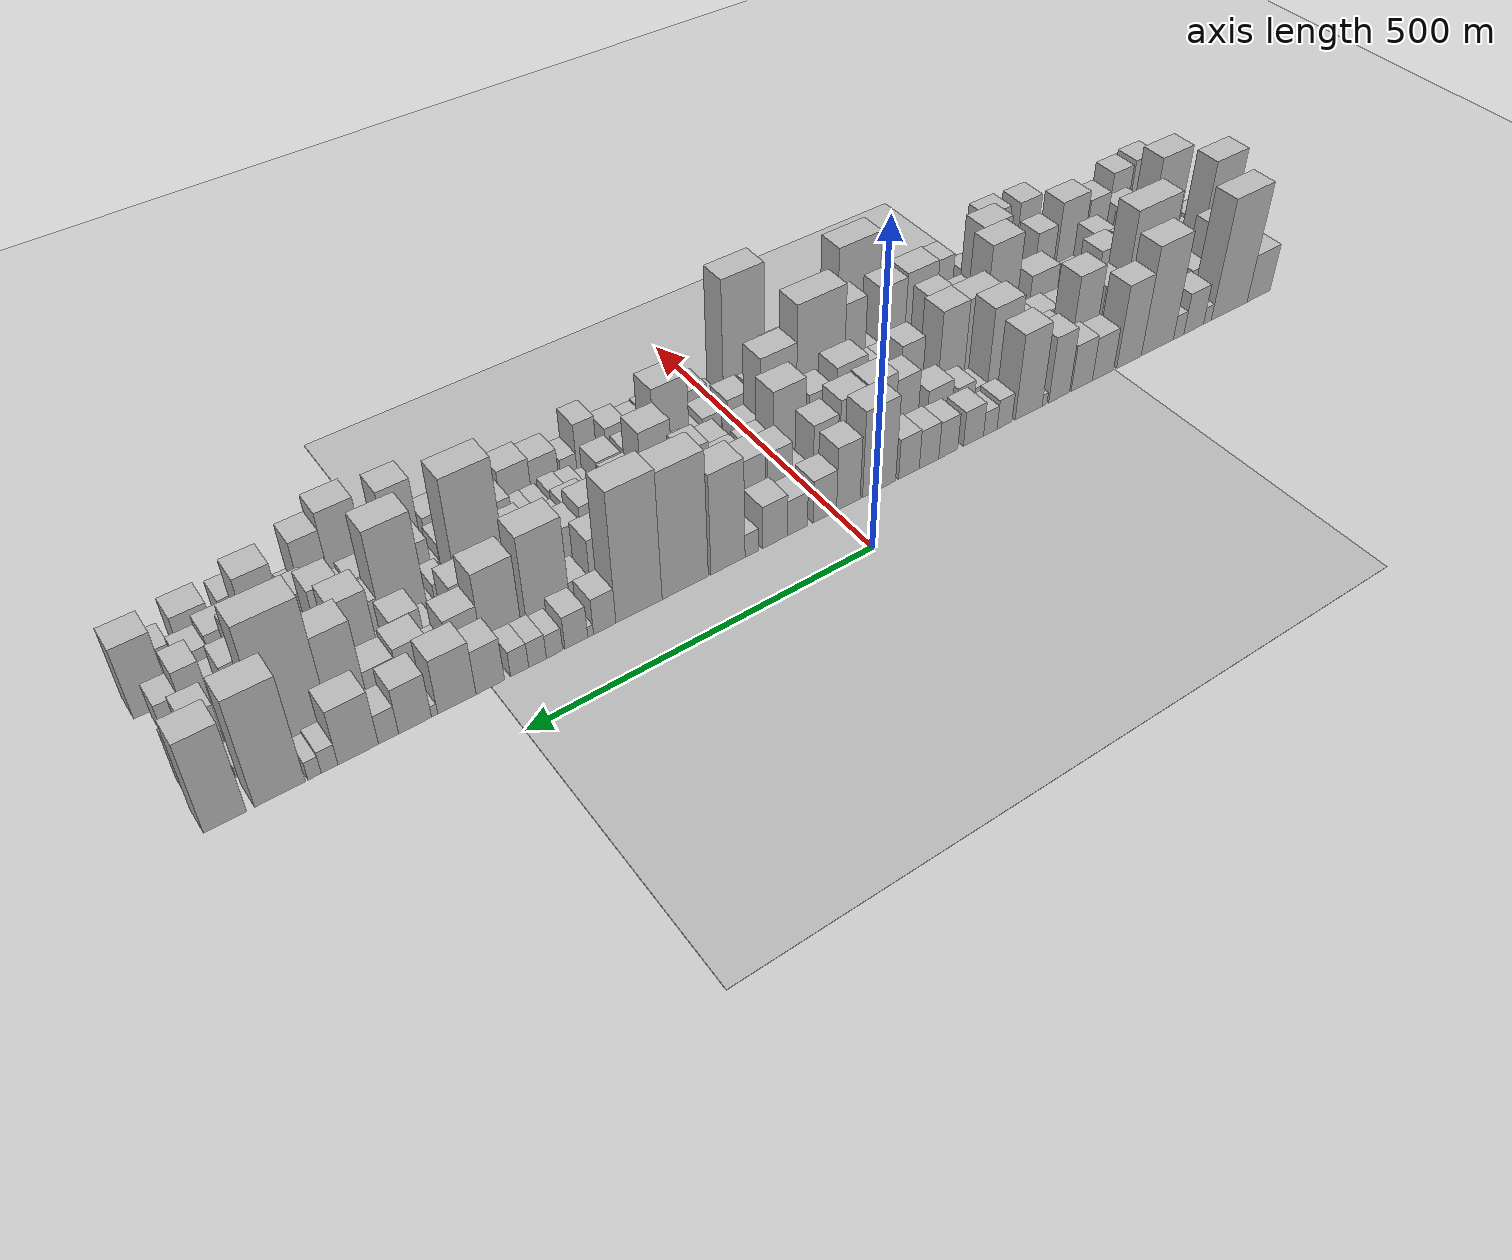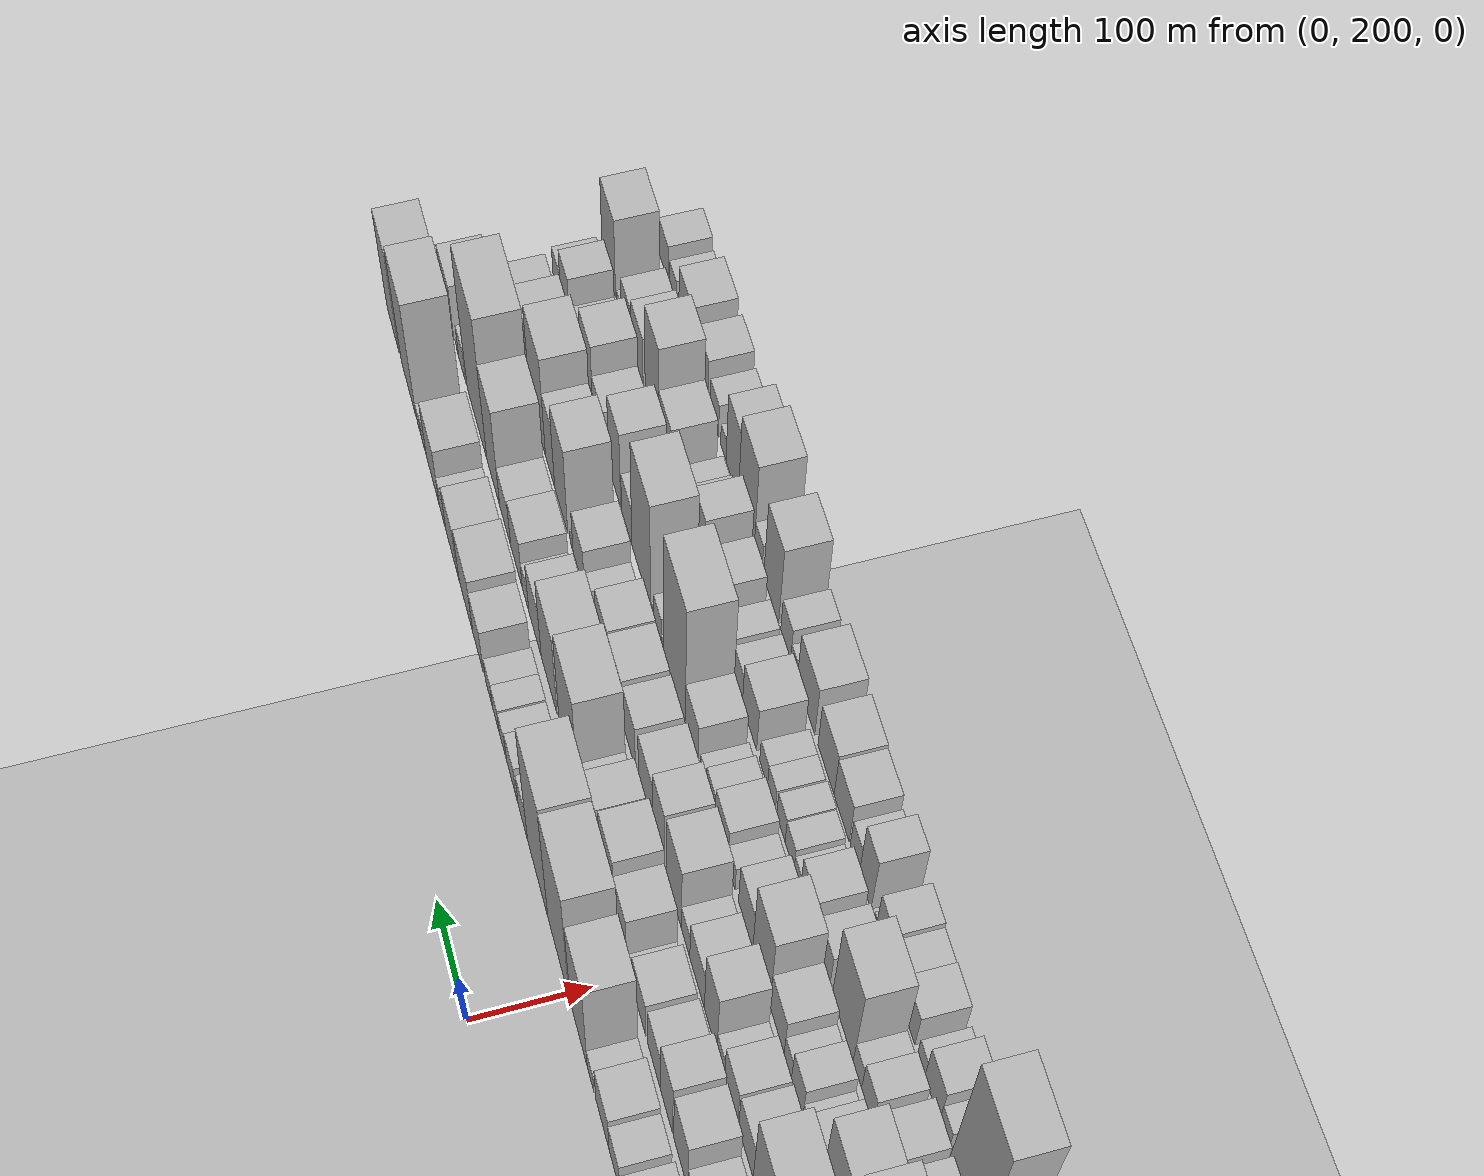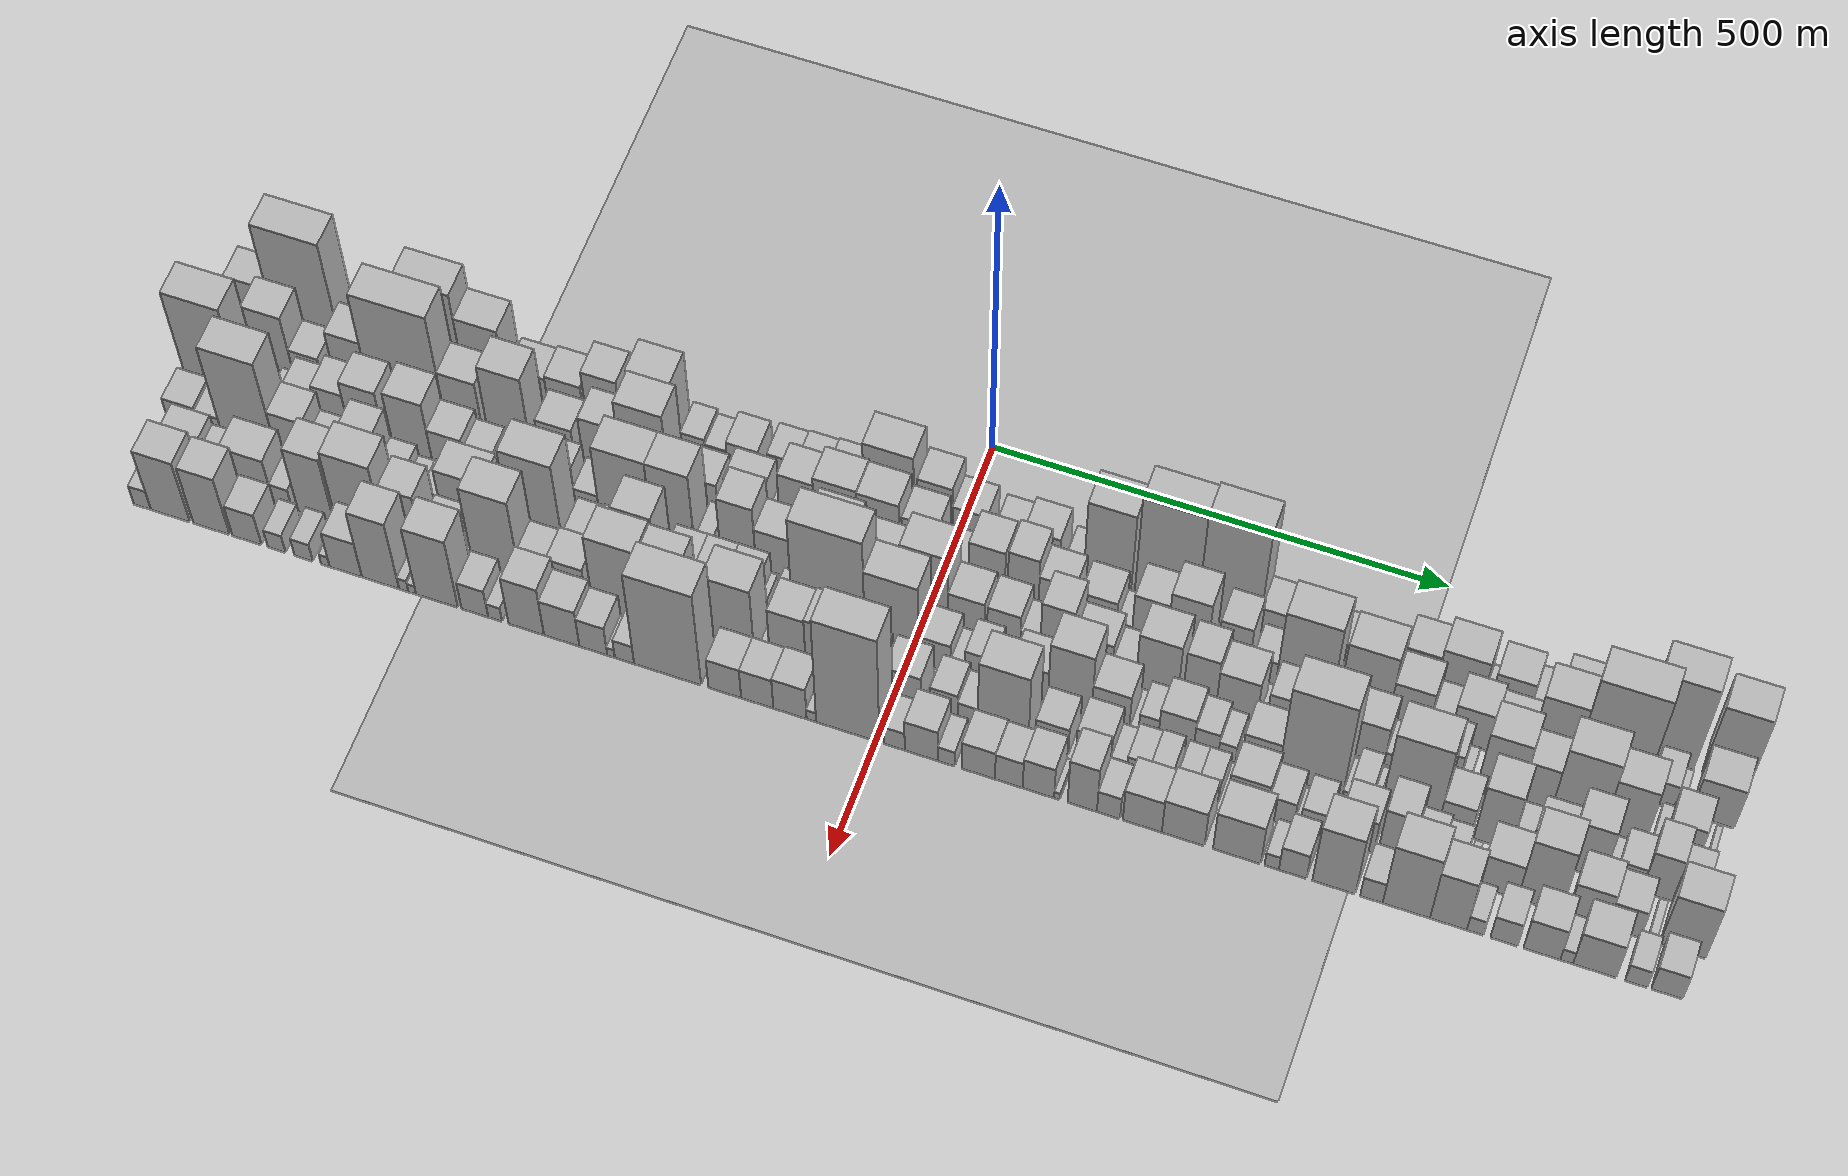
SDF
<?xml version="1.0" encoding="utf-8"?>

<sdf version="1.6">

   <world name="default">

      <gui fullscreen="0">

         <camera name="user_camera">

            <pose>-15 0 4.57585 0 0 0</pose>

            <view_controller>orbit</view_controller>

         </camera>

      </gui>

      <scene>

         <sky>

           <clouds>

             <speed>12</speed>

           </clouds>

         </sky>

         <ambient>0.4 0.4 0.4 1</ambient>

         <background>0.7 0.7 0.7 1</background>

         <shadows>1</shadows>

      </scene>

      <gravity>0 0 -9.8066</gravity>

      <magnetic_field>6e-06 2.3e-05 -4.2e-05</magnetic_field>

      <physics default="0" name="default_physics" type="ode">

         <ode>

            <solver>

               <type>quick</type>

               <iters>10</iters>

               <sor>1.0</sor>

               <use_dynamic_moi_rescaling>0</use_dynamic_moi_rescaling>

            </solver>

            <constraints>

               <cfm>0</cfm>

               <erp>0.2</erp>

               <contact_max_correcting_vel>100</contact_max_correcting_vel>

               <contact_surface_layer>0.001</contact_surface_layer>

            </constraints>

         </ode>

         <max_step_size>0.004</max_step_size>

         <real_time_factor>1</real_time_factor>

         <real_time_update_rate>250</real_time_update_rate>

      </physics>

      <light name="sun" type="directional">

         <cast_shadows>1</cast_shadows>

         <pose>0 0 10 0 0 0</pose>

         <diffuse>0.8 0.8 0.8 1</diffuse>

         <specular>0.2 0.2 0.2 1</specular>

         <attenuation>

            <range>1000</range>

            <constant>0.9</constant>

            <linear>0.01</linear>

            <quadratic>0.001</quadratic>

         </attenuation>

         <direction>-0.5 0.1 -0.9</direction>

      </light>

      <include>

         <name>ground_plane_1</name>

         <uri>model://HANNAS_ground_plane</uri>

         <pose>0 0 0  0 0 0</pose>

      </include>

      <include>

         <name>ground_plane_2</name>

         <uri>model://HANNAS_ground_plane</uri>

         <pose>100 0 0  0 0 0</pose>

      </include>

      <model name="building_1">

         <static>1</static>

         <pose frame="">100.0000 -796.8859 0 0.000000 0.000000 0.000000</pose>

         <link name="link">

            <pose frame="">0 0 42.00 0 0 0</pose>

            <collision name="collision">

               <geometry>

                  <box>

                     <size>40.0000 50.2283 84.0000</size>

                  </box>

               </geometry>

               <max_contacts>10</max_contacts>

               <surface>

                  <contact>

                     <ode/>

                  </contact>

                  <bounce/>

                  <friction>

                     <torsional>

                        <ode/>

                     </torsional>

                     <ode/>

                  </friction>

               </surface>

            </collision>

            <visual name="visual">

               <cast_shadows>0</cast_shadows>

               <geometry>

                  <box>

                     <size>40.0000 50.2283 84.0000</size>

                  </box>

               </geometry>

               <material>

                  <script>

                     <uri>model://HANNAS_wall/materials/scripts</uri>

                     <uri>model://HANNAS_wall/materials/textures</uri>

                     <name>vrc/HANNAS_wall</name>

                  </script>

               </material>

            </visual>

            <self_collide>0</self_collide>

            <enable_wind>0</enable_wind>

            <kinematic>0</kinematic>

         </link>

      </model>

      <model name="building_2">

         <static>1</static>

         <pose frame="">100.0000 -733.5840 0 0.000000 0.000000 0.000000</pose>

         <link name="link">

            <pose frame="">0 0 105.00 0 0 0</pose>

            <collision name="collision">

               <geometry>

                  <box>

                     <size>40.0000 76.3755 210.0000</size>

                  </box>

               </geometry>

               <max_contacts>10</max_contacts>

               <surface>

                  <contact>

                     <ode/>

                  </contact>

                  <bounce/>

                  <friction>

                     <torsional>

                        <ode/>

                     </torsional>

                     <ode/>

                  </friction>

               </surface>

            </collision>

            <visual name="visual">

               <cast_shadows>0</cast_shadows>

               <geometry>

                  <box>

                     <size>40.0000 76.3755 210.0000</size>

                  </box>

               </geometry>

               <material>

                  <script>

                     <uri>model://HANNAS_wall/materials/scripts</uri>

                     <uri>model://HANNAS_wall/materials/textures</uri>

                     <name>vrc/HANNAS_wall</name>

                  </script>

               </material>

            </visual>

            <self_collide>0</self_collide>

            <enable_wind>0</enable_wind>

            <kinematic>0</kinematic>

         </link>

      </model>

      <model name="building_3">

         <static>1</static>

         <pose frame="">100.0000 -687.3342 0 0.000000 0.000000 0.000000</pose>

         <link name="link">

            <pose frame="">0 0 15.00 0 0 0</pose>

            <collision name="collision">

               <geometry>

                  <box>

                     <size>40.0000 16.1241 30.0000</size>

                  </box>

               </geometry>

               <max_contacts>10</max_contacts>

               <surface>

                  <contact>

                     <ode/>

                  </contact>

                  <bounce/>

                  <friction>

                     <torsional>

                        <ode/>

                     </torsional>

                     <ode/>

                  </friction>

               </surface>

            </collision>

            <visual name="visual">

               <cast_shadows>0</cast_shadows>

               <geometry>

                  <box>

                     <size>40.0000 16.1241 30.0000</size>

                  </box>

               </geometry>

               <material>

                  <script>

                     <uri>model://HANNAS_wall/materials/scripts</uri>

                     <uri>model://HANNAS_wall/materials/textures</uri>

                     <name>vrc/HANNAS_wall</name>

                  </script>

               </material>

            </visual>

            <self_collide>0</self_collide>

            <enable_wind>0</enable_wind>

            <kinematic>0</kinematic>

         </link>

      </model>

      <model name="building_4">

         <static>1</static>

         <pose frame="">100.0000 -658.9254 0 0.000000 0.000000 0.000000</pose>

         <link name="link">

            <pose frame="">0 0 36.00 0 0 0</pose>

            <collision name="collision">

               <geometry>

                  <box>

                     <size>40.0000 40.6934 72.0000</size>

                  </box>

               </geometry>

               <max_contacts>10</max_contacts>

               <surface>

                  <contact>

                     <ode/>

                  </contact>

                  <bounce/>

                  <friction>

                     <torsional>

                        <ode/>

                     </torsional>

                     <ode/>

                  </friction>

               </surface>

            </collision>

            <visual name="visual">

               <cast_shadows>0</cast_shadows>

               <geometry>

                  <box>

                     <size>40.0000 40.6934 72.0000</size>

                  </box>

               </geometry>

               <material>

                  <script>

                     <uri>model://HANNAS_wall/materials/scripts</uri>

                     <uri>model://HANNAS_wall/materials/textures</uri>

                     <name>vrc/HANNAS_wall</name>

                  </script>

               </material>

            </visual>

            <self_collide>0</self_collide>

            <enable_wind>0</enable_wind>

            <kinematic>0</kinematic>

         </link>

      </model>

      <model name="building_5">

         <static>1</static>

         <pose frame="">100.0000 -627.7885 0 0.000000 0.000000 0.000000</pose>

         <link name="link">

            <pose frame="">0 0 21.00 0 0 0</pose>

            <collision name="collision">

               <geometry>

                  <box>

                     <size>40.0000 21.5804 42.0000</size>

                  </box>

               </geometry>

               <max_contacts>10</max_contacts>

               <surface>

                  <contact>

                     <ode/>

                  </contact>

                  <bounce/>

                  <friction>

                     <torsional>

                        <ode/>

                     </torsional>

                     <ode/>

                  </friction>

               </surface>

            </collision>

            <visual name="visual">

               <cast_shadows>0</cast_shadows>

               <geometry>

                  <box>

                     <size>40.0000 21.5804 42.0000</size>

                  </box>

               </geometry>

               <material>

                  <script>

                     <uri>model://HANNAS_wall/materials/scripts</uri>

                     <uri>model://HANNAS_wall/materials/textures</uri>

                     <name>vrc/HANNAS_wall</name>

                  </script>

               </material>

            </visual>

            <self_collide>0</self_collide>

            <enable_wind>0</enable_wind>

            <kinematic>0</kinematic>

         </link>

      </model>

      <model name="building_6">

         <static>1</static>

         <pose frame="">100.0000 -584.6158 0 0.000000 0.000000 0.000000</pose>

         <link name="link">

            <pose frame="">0 0 94.50 0 0 0</pose>

            <collision name="collision">

               <geometry>

                  <box>

                     <size>40.0000 64.7650 189.0000</size>

                  </box>

               </geometry>

               <max_contacts>10</max_contacts>

               <surface>

                  <contact>

                     <ode/>

                  </contact>

                  <bounce/>

                  <friction>

                     <torsional>

                        <ode/>

                     </torsional>

                     <ode/>

                  </friction>

               </surface>

            </collision>

            <visual name="visual">

               <cast_shadows>0</cast_shadows>

               <geometry>

                  <box>

                     <size>40.0000 64.7650 189.0000</size>

                  </box>

               </geometry>

               <material>

                  <script>

                     <uri>model://HANNAS_wall/materials/scripts</uri>

                     <uri>model://HANNAS_wall/materials/textures</uri>

                     <name>vrc/HANNAS_wall</name>

                  </script>

               </material>

            </visual>

            <self_collide>0</self_collide>

            <enable_wind>0</enable_wind>

            <kinematic>0</kinematic>

         </link>

      </model>

      <model name="building_7">

         <static>1</static>

         <pose frame="">100.0000 -527.9180 0 0.000000 0.000000 0.000000</pose>

         <link name="link">

            <pose frame="">0 0 72.00 0 0 0</pose>

            <collision name="collision">

               <geometry>

                  <box>

                     <size>40.0000 48.6304 144.0000</size>

                  </box>

               </geometry>

               <max_contacts>10</max_contacts>

               <surface>

                  <contact>

                     <ode/>

                  </contact>

                  <bounce/>

                  <friction>

                     <torsional>

                        <ode/>

                     </torsional>

                     <ode/>

                  </friction>

               </surface>

            </collision>

            <visual name="visual">

               <cast_shadows>0</cast_shadows>

               <geometry>

                  <box>

                     <size>40.0000 48.6304 144.0000</size>

                  </box>

               </geometry>

               <material>

                  <script>

                     <uri>model://HANNAS_wall/materials/scripts</uri>

                     <uri>model://HANNAS_wall/materials/textures</uri>

                     <name>vrc/HANNAS_wall</name>

                  </script>

               </material>

            </visual>

            <self_collide>0</self_collide>

            <enable_wind>0</enable_wind>

            <kinematic>0</kinematic>

         </link>

      </model>

      <model name="building_8">

         <static>1</static>

         <pose frame="">100.0000 -476.9769 0 0.000000 0.000000 0.000000</pose>

         <link name="link">

            <pose frame="">0 0 37.50 0 0 0</pose>

            <collision name="collision">

               <geometry>

                  <box>

                     <size>40.0000 41.2519 75.0000</size>

                  </box>

               </geometry>

               <max_contacts>10</max_contacts>

               <surface>

                  <contact>

                     <ode/>

                  </contact>

                  <bounce/>

                  <friction>

                     <torsional>

                        <ode/>

                     </torsional>

                     <ode/>

                  </friction>

               </surface>

            </collision>

            <visual name="visual">

               <cast_shadows>0</cast_shadows>

               <geometry>

                  <box>

                     <size>40.0000 41.2519 75.0000</size>

                  </box>

               </geometry>

               <material>

                  <script>

                     <uri>model://HANNAS_wall/materials/scripts</uri>

                     <uri>model://HANNAS_wall/materials/textures</uri>

                     <name>vrc/HANNAS_wall</name>

                  </script>

               </material>

            </visual>

            <self_collide>0</self_collide>

            <enable_wind>0</enable_wind>

            <kinematic>0</kinematic>

         </link>

      </model>

      <model name="building_9">

         <static>1</static>

         <pose frame="">100.0000 -436.0527 0 0.000000 0.000000 0.000000</pose>

         <link name="link">

            <pose frame="">0 0 40.50 0 0 0</pose>

            <collision name="collision">

               <geometry>

                  <box>

                     <size>40.0000 40.5966 81.0000</size>

                  </box>

               </geometry>

               <max_contacts>10</max_contacts>

               <surface>

                  <contact>

                     <ode/>

                  </contact>

                  <bounce/>

                  <friction>

                     <torsional>

                        <ode/>

                     </torsional>

                     <ode/>

                  </friction>

               </surface>

            </collision>

            <visual name="visual">

               <cast_shadows>0</cast_shadows>

               <geometry>

                  <box>

                     <size>40.0000 40.5966 81.0000</size>

                  </box>

               </geometry>

               <material>

                  <script>

                     <uri>model://HANNAS_wall/materials/scripts</uri>

                     <uri>model://HANNAS_wall/materials/textures</uri>

                     <name>vrc/HANNAS_wall</name>

                  </script>

               </material>

            </visual>

            <self_collide>0</self_collide>

            <enable_wind>0</enable_wind>

            <kinematic>0</kinematic>

         </link>

      </model>

      <model name="building_10">

         <static>1</static>

         <pose frame="">100.0000 -393.0205 0 0.000000 0.000000 0.000000</pose>

         <link name="link">

            <pose frame="">0 0 57.00 0 0 0</pose>

            <collision name="collision">

               <geometry>

                  <box>

                     <size>40.0000 39.4677 114.0000</size>

                  </box>

               </geometry>

               <max_contacts>10</max_contacts>

               <surface>

                  <contact>

                     <ode/>

                  </contact>

                  <bounce/>

                  <friction>

                     <torsional>

                        <ode/>

                     </torsional>

                     <ode/>

                  </friction>

               </surface>

            </collision>

            <visual name="visual">

               <cast_shadows>0</cast_shadows>

               <geometry>

                  <box>

                     <size>40.0000 39.4677 114.0000</size>

                  </box>

               </geometry>

               <material>

                  <script>

                     <uri>model://HANNAS_wall/materials/scripts</uri>

                     <uri>model://HANNAS_wall/materials/textures</uri>

                     <name>vrc/HANNAS_wall</name>

                  </script>

               </material>

            </visual>

            <self_collide>0</self_collide>

            <enable_wind>0</enable_wind>

            <kinematic>0</kinematic>

         </link>

      </model>

      <model name="building_11">

         <static>1</static>

         <pose frame="">100.0000 -365.6072 0 0.000000 0.000000 0.000000</pose>

         <link name="link">

            <pose frame="">0 0 10.50 0 0 0</pose>

            <collision name="collision">

               <geometry>

                  <box>

                     <size>40.0000 9.3589 21.0000</size>

                  </box>

               </geometry>

               <max_contacts>10</max_contacts>

               <surface>

                  <contact>

                     <ode/>

                  </contact>

                  <bounce/>

                  <friction>

                     <torsional>

                        <ode/>

                     </torsional>

                     <ode/>

                  </friction>

               </surface>

            </collision>

            <visual name="visual">

               <cast_shadows>0</cast_shadows>

               <geometry>

                  <box>

                     <size>40.0000 9.3589 21.0000</size>

                  </box>

               </geometry>

               <material>

                  <script>

                     <uri>model://HANNAS_wall/materials/scripts</uri>

                     <uri>model://HANNAS_wall/materials/textures</uri>

                     <name>vrc/HANNAS_wall</name>

                  </script>

               </material>

            </visual>

            <self_collide>0</self_collide>

            <enable_wind>0</enable_wind>

            <kinematic>0</kinematic>

         </link>

      </model>

      <model name="building_12">

         <static>1</static>

         <pose frame="">100.0000 -336.2007 0 0.000000 0.000000 0.000000</pose>

         <link name="link">

            <pose frame="">0 0 73.50 0 0 0</pose>

            <collision name="collision">

               <geometry>

                  <box>

                     <size>40.0000 49.4543 147.0000</size>

                  </box>

               </geometry>

               <max_contacts>10</max_contacts>

               <surface>

                  <contact>

                     <ode/>

                  </contact>

                  <bounce/>

                  <friction>

                     <torsional>

                        <ode/>

                     </torsional>

                     <ode/>

                  </friction>

               </surface>

            </collision>

            <visual name="visual">

               <cast_shadows>0</cast_shadows>

               <geometry>

                  <box>

                     <size>40.0000 49.4543 147.0000</size>

                  </box>

               </geometry>

               <material>

                  <script>

                     <uri>model://HANNAS_wall/materials/scripts</uri>

                     <uri>model://HANNAS_wall/materials/textures</uri>

                     <name>vrc/HANNAS_wall</name>

                  </script>

               </material>

            </visual>

            <self_collide>0</self_collide>

            <enable_wind>0</enable_wind>

            <kinematic>0</kinematic>

         </link>

      </model>

      <model name="building_13">

         <static>1</static>

         <pose frame="">100.0000 -291.9677 0 0.000000 0.000000 0.000000</pose>

         <link name="link">

            <pose frame="">0 0 25.50 0 0 0</pose>

            <collision name="collision">

               <geometry>

                  <box>

                     <size>40.0000 27.0116 51.0000</size>

                  </box>

               </geometry>

               <max_contacts>10</max_contacts>

               <surface>

                  <contact>

                     <ode/>

                  </contact>

                  <bounce/>

                  <friction>

                     <torsional>

                        <ode/>

                     </torsional>

                     <ode/>

                  </friction>

               </surface>

            </collision>

            <visual name="visual">

               <cast_shadows>0</cast_shadows>

               <geometry>

                  <box>

                     <size>40.0000 27.0116 51.0000</size>

                  </box>

               </geometry>

               <material>

                  <script>

                     <uri>model://HANNAS_wall/materials/scripts</uri>

                     <uri>model://HANNAS_wall/materials/textures</uri>

                     <name>vrc/HANNAS_wall</name>

                  </script>

               </material>

            </visual>

            <self_collide>0</self_collide>

            <enable_wind>0</enable_wind>

            <kinematic>0</kinematic>

         </link>

      </model>

      <model name="building_14">

         <static>1</static>

         <pose frame="">100.0000 -266.3513 0 0.000000 0.000000 0.000000</pose>

         <link name="link">

            <pose frame="">0 0 21.00 0 0 0</pose>

            <collision name="collision">

               <geometry>

                  <box>

                     <size>40.0000 24.2213 42.0000</size>

                  </box>

               </geometry>

               <max_contacts>10</max_contacts>

               <surface>

                  <contact>

                     <ode/>

                  </contact>

                  <bounce/>

                  <friction>

                     <torsional>

                        <ode/>

                     </torsional>

                     <ode/>

                  </friction>

               </surface>

            </collision>

            <visual name="visual">

               <cast_shadows>0</cast_shadows>

               <geometry>

                  <box>

                     <size>40.0000 24.2213 42.0000</size>

                  </box>

               </geometry>

               <material>

                  <script>

                     <uri>model://HANNAS_wall/materials/scripts</uri>

                     <uri>model://HANNAS_wall/materials/textures</uri>

                     <name>vrc/HANNAS_wall</name>

                  </script>

               </material>

            </visual>

            <self_collide>0</self_collide>

            <enable_wind>0</enable_wind>

            <kinematic>0</kinematic>

         </link>

      </model>

      <model name="building_15">

         <static>1</static>

         <pose frame="">100.0000 -236.4188 0 0.000000 0.000000 0.000000</pose>

         <link name="link">

            <pose frame="">0 0 30.00 0 0 0</pose>

            <collision name="collision">

               <geometry>

                  <box>

                     <size>40.0000 35.6436 60.0000</size>

                  </box>

               </geometry>

               <max_contacts>10</max_contacts>

               <surface>

                  <contact>

                     <ode/>

                  </contact>

                  <bounce/>

                  <friction>

                     <torsional>

                        <ode/>

                     </torsional>

                     <ode/>

                  </friction>

               </surface>

            </collision>

            <visual name="visual">

               <cast_shadows>0</cast_shadows>

               <geometry>

                  <box>

                     <size>40.0000 35.6436 60.0000</size>

                  </box>

               </geometry>

               <material>

                  <script>

                     <uri>model://HANNAS_wall/materials/scripts</uri>

                     <uri>model://HANNAS_wall/materials/textures</uri>

                     <name>vrc/HANNAS_wall</name>

                  </script>

               </material>

            </visual>

            <self_collide>0</self_collide>

            <enable_wind>0</enable_wind>

            <kinematic>0</kinematic>

         </link>

      </model>

      <model name="building_16">

         <static>1</static>

         <pose frame="">100.0000 -192.0225 0 0.000000 0.000000 0.000000</pose>

         <link name="link">

            <pose frame="">0 0 31.50 0 0 0</pose>

            <collision name="collision">

               <geometry>

                  <box>

                     <size>40.0000 33.1490 63.0000</size>

                  </box>

               </geometry>

               <max_contacts>10</max_contacts>

               <surface>

                  <contact>

                     <ode/>

                  </contact>

                  <bounce/>

                  <friction>

                     <torsional>

                        <ode/>

                     </torsional>

                     <ode/>

                  </friction>

               </surface>

            </collision>

            <visual name="visual">

               <cast_shadows>0</cast_shadows>

               <geometry>

                  <box>

                     <size>40.0000 33.1490 63.0000</size>

                  </box>

               </geometry>

               <material>

                  <script>

                     <uri>model://HANNAS_wall/materials/scripts</uri>

                     <uri>model://HANNAS_wall/materials/textures</uri>

                     <name>vrc/HANNAS_wall</name>

                  </script>

               </material>

            </visual>

            <self_collide>0</self_collide>

            <enable_wind>0</enable_wind>

            <kinematic>0</kinematic>

         </link>

      </model>

      <model name="building_17">

         <static>1</static>

         <pose frame="">100.0000 -158.6451 0 0.000000 0.000000 0.000000</pose>

         <link name="link">

            <pose frame="">0 0 33.00 0 0 0</pose>

            <collision name="collision">

               <geometry>

                  <box>

                     <size>40.0000 33.6058 66.0000</size>

                  </box>

               </geometry>

               <max_contacts>10</max_contacts>

               <surface>

                  <contact>

                     <ode/>

                  </contact>

                  <bounce/>

                  <friction>

                     <torsional>

                        <ode/>

                     </torsional>

                     <ode/>

                  </friction>

               </surface>

            </collision>

            <visual name="visual">

               <cast_shadows>0</cast_shadows>

               <geometry>

                  <box>

                     <size>40.0000 33.6058 66.0000</size>

                  </box>

               </geometry>

               <material>

                  <script>

                     <uri>model://HANNAS_wall/materials/scripts</uri>

                     <uri>model://HANNAS_wall/materials/textures</uri>

                     <name>vrc/HANNAS_wall</name>

                  </script>

               </material>

            </visual>

            <self_collide>0</self_collide>

            <enable_wind>0</enable_wind>

            <kinematic>0</kinematic>

         </link>

      </model>

      <model name="building_18">

         <static>1</static>

         <pose frame="">100.0000 -124.2593 0 0.000000 0.000000 0.000000</pose>

         <link name="link">

            <pose frame="">0 0 34.50 0 0 0</pose>

            <collision name="collision">

               <geometry>

                  <box>

                     <size>40.0000 35.1658 69.0000</size>

                  </box>

               </geometry>

               <max_contacts>10</max_contacts>

               <surface>

                  <contact>

                     <ode/>

                  </contact>

                  <bounce/>

                  <friction>

                     <torsional>

                        <ode/>

                     </torsional>

                     <ode/>

                  </friction>

               </surface>

            </collision>

            <visual name="visual">

               <cast_shadows>0</cast_shadows>

               <geometry>

                  <box>

                     <size>40.0000 35.1658 69.0000</size>

                  </box>

               </geometry>

               <material>

                  <script>

                     <uri>model://HANNAS_wall/materials/scripts</uri>

                     <uri>model://HANNAS_wall/materials/textures</uri>

                     <name>vrc/HANNAS_wall</name>

                  </script>

               </material>

            </visual>

            <self_collide>0</self_collide>

            <enable_wind>0</enable_wind>

            <kinematic>0</kinematic>

         </link>

      </model>

      <model name="building_19">

         <static>1</static>

         <pose frame="">100.0000 -74.0402 0 0.000000 0.000000 0.000000</pose>

         <link name="link">

            <pose frame="">0 0 73.50 0 0 0</pose>

            <collision name="collision">

               <geometry>

                  <box>

                     <size>40.0000 55.2724 147.0000</size>

                  </box>

               </geometry>

               <max_contacts>10</max_contacts>

               <surface>

                  <contact>

                     <ode/>

                  </contact>

                  <bounce/>

                  <friction>

                     <torsional>

                        <ode/>

                     </torsional>

                     <ode/>

                  </friction>

               </surface>

            </collision>

            <visual name="visual">

               <cast_shadows>0</cast_shadows>

               <geometry>

                  <box>

                     <size>40.0000 55.2724 147.0000</size>

                  </box>

               </geometry>

               <material>

                  <script>

                     <uri>model://HANNAS_wall/materials/scripts</uri>

                     <uri>model://HANNAS_wall/materials/textures</uri>

                     <name>vrc/HANNAS_wall</name>

                  </script>

               </material>

            </visual>

            <self_collide>0</self_collide>

            <enable_wind>0</enable_wind>

            <kinematic>0</kinematic>

         </link>

      </model>

      <model name="building_20">

         <static>1</static>

         <pose frame="">100.0000 -23.1641 0 0.000000 0.000000 0.000000</pose>

         <link name="link">

            <pose frame="">0 0 54.00 0 0 0</pose>

            <collision name="collision">

               <geometry>

                  <box>

                     <size>40.0000 38.4799 108.0000</size>

                  </box>

               </geometry>

               <max_contacts>10</max_contacts>

               <surface>

                  <contact>

                     <ode/>

                  </contact>

                  <bounce/>

                  <friction>

                     <torsional>

                        <ode/>

                     </torsional>

                     <ode/>

                  </friction>

               </surface>

            </collision>

            <visual name="visual">

               <cast_shadows>0</cast_shadows>

               <geometry>

                  <box>

                     <size>40.0000 38.4799 108.0000</size>

                  </box>

               </geometry>

               <material>

                  <script>

                     <uri>model://HANNAS_wall/materials/scripts</uri>

                     <uri>model://HANNAS_wall/materials/textures</uri>

                     <name>vrc/HANNAS_wall</name>

                  </script>

               </material>

            </visual>

            <self_collide>0</self_collide>

            <enable_wind>0</enable_wind>

            <kinematic>0</kinematic>

         </link>

      </model>

      <model name="building_21">

         <static>1</static>

         <pose frame="">100.0000 14.8848 0 0.000000 0.000000 0.000000</pose>

         <link name="link">

            <pose frame="">0 0 36.00 0 0 0</pose>

            <collision name="collision">

               <geometry>

                  <box>

                     <size>40.0000 37.6179 72.0000</size>

                  </box>

               </geometry>

               <max_contacts>10</max_contacts>

               <surface>

                  <contact>

                     <ode/>

                  </contact>

                  <bounce/>

                  <friction>

                     <torsional>

                        <ode/>

                     </torsional>

                     <ode/>

                  </friction>

               </surface>

            </collision>

            <visual name="visual">

               <cast_shadows>0</cast_shadows>

               <geometry>

                  <box>

                     <size>40.0000 37.6179 72.0000</size>

                  </box>

               </geometry>

               <material>

                  <script>

                     <uri>model://HANNAS_wall/materials/scripts</uri>

                     <uri>model://HANNAS_wall/materials/textures</uri>

                     <name>vrc/HANNAS_wall</name>

                  </script>

               </material>

            </visual>

            <self_collide>0</self_collide>

            <enable_wind>0</enable_wind>

            <kinematic>0</kinematic>

         </link>

      </model>

      <model name="building_22">

         <static>1</static>

         <pose frame="">100.0000 58.4036 0 0.000000 0.000000 0.000000</pose>

         <link name="link">

            <pose frame="">0 0 30.00 0 0 0</pose>

            <collision name="collision">

               <geometry>

                  <box>

                     <size>40.0000 31.4197 60.0000</size>

                  </box>

               </geometry>

               <max_contacts>10</max_contacts>

               <surface>

                  <contact>

                     <ode/>

                  </contact>

                  <bounce/>

                  <friction>

                     <torsional>

                        <ode/>

                     </torsional>

                     <ode/>

                  </friction>

               </surface>

            </collision>

            <visual name="visual">

               <cast_shadows>0</cast_shadows>

               <geometry>

                  <box>

                     <size>40.0000 31.4197 60.0000</size>

                  </box>

               </geometry>

               <material>

                  <script>

                     <uri>model://HANNAS_wall/materials/scripts</uri>

                     <uri>model://HANNAS_wall/materials/textures</uri>

                     <name>vrc/HANNAS_wall</name>

                  </script>

               </material>

            </visual>

            <self_collide>0</self_collide>

            <enable_wind>0</enable_wind>

            <kinematic>0</kinematic>

         </link>

      </model>

      <model name="building_23">

         <static>1</static>

         <pose frame="">100.0000 93.8750 0 0.000000 0.000000 0.000000</pose>

         <link name="link">

            <pose frame="">0 0 36.00 0 0 0</pose>

            <collision name="collision">

               <geometry>

                  <box>

                     <size>40.0000 39.5232 72.0000</size>

                  </box>

               </geometry>

               <max_contacts>10</max_contacts>

               <surface>

                  <contact>

                     <ode/>

                  </contact>

                  <bounce/>

                  <friction>

                     <torsional>

                        <ode/>

                     </torsional>

                     <ode/>

                  </friction>

               </surface>

            </collision>

            <visual name="visual">

               <cast_shadows>0</cast_shadows>

               <geometry>

                  <box>

                     <size>40.0000 39.5232 72.0000</size>

                  </box>

               </geometry>

               <material>

                  <script>

                     <uri>model://HANNAS_wall/materials/scripts</uri>

                     <uri>model://HANNAS_wall/materials/textures</uri>

                     <name>vrc/HANNAS_wall</name>

                  </script>

               </material>

            </visual>

            <self_collide>0</self_collide>

            <enable_wind>0</enable_wind>

            <kinematic>0</kinematic>

         </link>

      </model>

      <model name="building_24">

         <static>1</static>

         <pose frame="">100.0000 129.8729 0 0.000000 0.000000 0.000000</pose>

         <link name="link">

            <pose frame="">0 0 19.50 0 0 0</pose>

            <collision name="collision">

               <geometry>

                  <box>

                     <size>40.0000 20.4726 39.0000</size>

                  </box>

               </geometry>

               <max_contacts>10</max_contacts>

               <surface>

                  <contact>

                     <ode/>

                  </contact>

                  <bounce/>

                  <friction>

                     <torsional>

                        <ode/>

                     </torsional>

                     <ode/>

                  </friction>

               </surface>

            </collision>

            <visual name="visual">

               <cast_shadows>0</cast_shadows>

               <geometry>

                  <box>

                     <size>40.0000 20.4726 39.0000</size>

                  </box>

               </geometry>

               <material>

                  <script>

                     <uri>model://HANNAS_wall/materials/scripts</uri>

                     <uri>model://HANNAS_wall/materials/textures</uri>

                     <name>vrc/HANNAS_wall</name>

                  </script>

               </material>

            </visual>

            <self_collide>0</self_collide>

            <enable_wind>0</enable_wind>

            <kinematic>0</kinematic>

         </link>

      </model>

      <model name="building_25">

         <static>1</static>

         <pose frame="">100.0000 165.9159 0 0.000000 0.000000 0.000000</pose>

         <link name="link">

            <pose frame="">0 0 84.00 0 0 0</pose>

            <collision name="collision">

               <geometry>

                  <box>

                     <size>40.0000 51.6133 168.0000</size>

                  </box>

               </geometry>

               <max_contacts>10</max_contacts>

               <surface>

                  <contact>

                     <ode/>

                  </contact>

                  <bounce/>

                  <friction>

                     <torsional>

                        <ode/>

                     </torsional>

                     <ode/>

                  </friction>

               </surface>

            </collision>

            <visual name="visual">

               <cast_shadows>0</cast_shadows>

               <geometry>

                  <box>

                     <size>40.0000 51.6133 168.0000</size>

                  </box>

               </geometry>

               <material>

                  <script>

                     <uri>model://HANNAS_wall/materials/scripts</uri>

                     <uri>model://HANNAS_wall/materials/textures</uri>

                     <name>vrc/HANNAS_wall</name>

                  </script>

               </material>

            </visual>

            <self_collide>0</self_collide>

            <enable_wind>0</enable_wind>

            <kinematic>0</kinematic>

         </link>

      </model>

      <model name="building_26">

         <static>1</static>

         <pose frame="">100.0000 229.7220 0 0.000000 0.000000 0.000000</pose>

         <link name="link">

            <pose frame="">0 0 105.00 0 0 0</pose>

            <collision name="collision">

               <geometry>

                  <box>

                     <size>40.0000 67.9990 210.0000</size>

                  </box>

               </geometry>

               <max_contacts>10</max_contacts>

               <surface>

                  <contact>

                     <ode/>

                  </contact>

                  <bounce/>

                  <friction>

                     <torsional>

                        <ode/>

                     </torsional>

                     <ode/>

                  </friction>

               </surface>

            </collision>

            <visual name="visual">

               <cast_shadows>0</cast_shadows>

               <geometry>

                  <box>

                     <size>40.0000 67.9990 210.0000</size>

                  </box>

               </geometry>

               <material>

                  <script>

                     <uri>model://HANNAS_wall/materials/scripts</uri>

                     <uri>model://HANNAS_wall/materials/textures</uri>

                     <name>vrc/HANNAS_wall</name>

                  </script>

               </material>

            </visual>

            <self_collide>0</self_collide>

            <enable_wind>0</enable_wind>

            <kinematic>0</kinematic>

         </link>

      </model>

      <model name="building_27">

         <static>1</static>

         <pose frame="">100.0000 296.9194 0 0.000000 0.000000 0.000000</pose>

         <link name="link">

            <pose frame="">0 0 108.00 0 0 0</pose>

            <collision name="collision">

               <geometry>

                  <box>

                     <size>40.0000 66.3957 216.0000</size>

                  </box>

               </geometry>

               <max_contacts>10</max_contacts>

               <surface>

                  <contact>

                     <ode/>

                  </contact>

                  <bounce/>

                  <friction>

                     <torsional>

                        <ode/>

                     </torsional>

                     <ode/>

                  </friction>

               </surface>

            </collision>

            <visual name="visual">

               <cast_shadows>0</cast_shadows>

               <geometry>

                  <box>

                     <size>40.0000 66.3957 216.0000</size>

                  </box>

               </geometry>

               <material>

                  <script>

                     <uri>model://HANNAS_wall/materials/scripts</uri>

                     <uri>model://HANNAS_wall/materials/textures</uri>

                     <name>vrc/HANNAS_wall</name>

                  </script>

               </material>

            </visual>

            <self_collide>0</self_collide>

            <enable_wind>0</enable_wind>

            <kinematic>0</kinematic>

         </link>

      </model>

      <model name="building_28">

         <static>1</static>

         <pose frame="">100.0000 345.7990 0 0.000000 0.000000 0.000000</pose>

         <link name="link">

            <pose frame="">0 0 30.00 0 0 0</pose>

            <collision name="collision">

               <geometry>

                  <box>

                     <size>40.0000 31.3636 60.0000</size>

                  </box>

               </geometry>

               <max_contacts>10</max_contacts>

               <surface>

                  <contact>

                     <ode/>

                  </contact>

                  <bounce/>

                  <friction>

                     <torsional>

                        <ode/>

                     </torsional>

                     <ode/>

                  </friction>

               </surface>

            </collision>

            <visual name="visual">

               <cast_shadows>0</cast_shadows>

               <geometry>

                  <box>

                     <size>40.0000 31.3636 60.0000</size>

                  </box>

               </geometry>

               <material>

                  <script>

                     <uri>model://HANNAS_wall/materials/scripts</uri>

                     <uri>model://HANNAS_wall/materials/textures</uri>

                     <name>vrc/HANNAS_wall</name>

                  </script>

               </material>

            </visual>

            <self_collide>0</self_collide>

            <enable_wind>0</enable_wind>

            <kinematic>0</kinematic>

         </link>

      </model>

      <model name="building_29">

         <static>1</static>

         <pose frame="">100.0000 365.5099 0 0.000000 0.000000 0.000000</pose>

         <link name="link">

            <pose frame="">0 0 9.00 0 0 0</pose>

            <collision name="collision">

               <geometry>

                  <box>

                     <size>40.0000 8.0583 18.0000</size>

                  </box>

               </geometry>

               <max_contacts>10</max_contacts>

               <surface>

                  <contact>

                     <ode/>

                  </contact>

                  <bounce/>

                  <friction>

                     <torsional>

                        <ode/>

                     </torsional>

                     <ode/>

                  </friction>

               </surface>

            </collision>

            <visual name="visual">

               <cast_shadows>0</cast_shadows>

               <geometry>

                  <box>

                     <size>40.0000 8.0583 18.0000</size>

                  </box>

               </geometry>

               <material>

                  <script>

                     <uri>model://HANNAS_wall/materials/scripts</uri>

                     <uri>model://HANNAS_wall/materials/textures</uri>

                     <name>vrc/HANNAS_wall</name>

                  </script>

               </material>

            </visual>

            <self_collide>0</self_collide>

            <enable_wind>0</enable_wind>

            <kinematic>0</kinematic>

         </link>

      </model>

      <model name="building_30">

         <static>1</static>

         <pose frame="">100.0000 385.2607 0 0.000000 0.000000 0.000000</pose>

         <link name="link">

            <pose frame="">0 0 27.00 0 0 0</pose>

            <collision name="collision">

               <geometry>

                  <box>

                     <size>40.0000 31.4432 54.0000</size>

                  </box>

               </geometry>

               <max_contacts>10</max_contacts>

               <surface>

                  <contact>

                     <ode/>

                  </contact>

                  <bounce/>

                  <friction>

                     <torsional>

                        <ode/>

                     </torsional>

                     <ode/>

                  </friction>

               </surface>

            </collision>

            <visual name="visual">

               <cast_shadows>0</cast_shadows>

               <geometry>

                  <box>

                     <size>40.0000 31.4432 54.0000</size>

                  </box>

               </geometry>

               <material>

                  <script>

                     <uri>model://HANNAS_wall/materials/scripts</uri>

                     <uri>model://HANNAS_wall/materials/textures</uri>

                     <name>vrc/HANNAS_wall</name>

                  </script>

               </material>

            </visual>

            <self_collide>0</self_collide>

            <enable_wind>0</enable_wind>

            <kinematic>0</kinematic>

         </link>

      </model>

      <model name="building_31">

         <static>1</static>

         <pose frame="">100.0000 415.1089 0 0.000000 0.000000 0.000000</pose>

         <link name="link">

            <pose frame="">0 0 19.50 0 0 0</pose>

            <collision name="collision">

               <geometry>

                  <box>

                     <size>40.0000 22.2534 39.0000</size>

                  </box>

               </geometry>

               <max_contacts>10</max_contacts>

               <surface>

                  <contact>

                     <ode/>

                  </contact>

                  <bounce/>

                  <friction>

                     <torsional>

                        <ode/>

                     </torsional>

                     <ode/>

                  </friction>

               </surface>

            </collision>

            <visual name="visual">

               <cast_shadows>0</cast_shadows>

               <geometry>

                  <box>

                     <size>40.0000 22.2534 39.0000</size>

                  </box>

               </geometry>

               <material>

                  <script>

                     <uri>model://HANNAS_wall/materials/scripts</uri>

                     <uri>model://HANNAS_wall/materials/textures</uri>

                     <name>vrc/HANNAS_wall</name>

                  </script>

               </material>

            </visual>

            <self_collide>0</self_collide>

            <enable_wind>0</enable_wind>

            <kinematic>0</kinematic>

         </link>

      </model>

      <model name="building_32">

         <static>1</static>

         <pose frame="">100.0000 438.1735 0 0.000000 0.000000 0.000000</pose>

         <link name="link">

            <pose frame="">0 0 21.00 0 0 0</pose>

            <collision name="collision">

               <geometry>

                  <box>

                     <size>40.0000 23.8757 42.0000</size>

                  </box>

               </geometry>

               <max_contacts>10</max_contacts>

               <surface>

                  <contact>

                     <ode/>

                  </contact>

                  <bounce/>

                  <friction>

                     <torsional>

                        <ode/>

                     </torsional>

                     <ode/>

                  </friction>

               </surface>

            </collision>

            <visual name="visual">

               <cast_shadows>0</cast_shadows>

               <geometry>

                  <box>

                     <size>40.0000 23.8757 42.0000</size>

                  </box>

               </geometry>

               <material>

                  <script>

                     <uri>model://HANNAS_wall/materials/scripts</uri>

                     <uri>model://HANNAS_wall/materials/textures</uri>

                     <name>vrc/HANNAS_wall</name>

                  </script>

               </material>

            </visual>

            <self_collide>0</self_collide>

            <enable_wind>0</enable_wind>

            <kinematic>0</kinematic>

         </link>

      </model>

      <model name="building_33">

         <static>1</static>

         <pose frame="">100.0000 462.2350 0 0.000000 0.000000 0.000000</pose>

         <link name="link">

            <pose frame="">0 0 21.00 0 0 0</pose>

            <collision name="collision">

               <geometry>

                  <box>

                     <size>40.0000 24.2474 42.0000</size>

                  </box>

               </geometry>

               <max_contacts>10</max_contacts>

               <surface>

                  <contact>

                     <ode/>

                  </contact>

                  <bounce/>

                  <friction>

                     <torsional>

                        <ode/>

                     </torsional>

                     <ode/>

                  </friction>

               </surface>

            </collision>

            <visual name="visual">

               <cast_shadows>0</cast_shadows>

               <geometry>

                  <box>

                     <size>40.0000 24.2474 42.0000</size>

                  </box>

               </geometry>

               <material>

                  <script>

                     <uri>model://HANNAS_wall/materials/scripts</uri>

                     <uri>model://HANNAS_wall/materials/textures</uri>

                     <name>vrc/HANNAS_wall</name>

                  </script>

               </material>

            </visual>

            <self_collide>0</self_collide>

            <enable_wind>0</enable_wind>

            <kinematic>0</kinematic>

         </link>

      </model>

      <model name="building_34">

         <static>1</static>

         <pose frame="">100.0000 501.0210 0 0.000000 0.000000 0.000000</pose>

         <link name="link">

            <pose frame="">0 0 36.00 0 0 0</pose>

            <collision name="collision">

               <geometry>

                  <box>

                     <size>40.0000 37.3245 72.0000</size>

                  </box>

               </geometry>

               <max_contacts>10</max_contacts>

               <surface>

                  <contact>

                     <ode/>

                  </contact>

                  <bounce/>

                  <friction>

                     <torsional>

                        <ode/>

                     </torsional>

                     <ode/>

                  </friction>

               </surface>

            </collision>

            <visual name="visual">

               <cast_shadows>0</cast_shadows>

               <geometry>

                  <box>

                     <size>40.0000 37.3245 72.0000</size>

                  </box>

               </geometry>

               <material>

                  <script>

                     <uri>model://HANNAS_wall/materials/scripts</uri>

                     <uri>model://HANNAS_wall/materials/textures</uri>

                     <name>vrc/HANNAS_wall</name>

                  </script>

               </material>

            </visual>

            <self_collide>0</self_collide>

            <enable_wind>0</enable_wind>

            <kinematic>0</kinematic>

         </link>

      </model>

      <model name="building_35">

         <static>1</static>

         <pose frame="">100.0000 544.4039 0 0.000000 0.000000 0.000000</pose>

         <link name="link">

            <pose frame="">0 0 45.00 0 0 0</pose>

            <collision name="collision">

               <geometry>

                  <box>

                     <size>40.0000 49.4412 90.0000</size>

                  </box>

               </geometry>

               <max_contacts>10</max_contacts>

               <surface>

                  <contact>

                     <ode/>

                  </contact>

                  <bounce/>

                  <friction>

                     <torsional>

                        <ode/>

                     </torsional>

                     <ode/>

                  </friction>

               </surface>

            </collision>

            <visual name="visual">

               <cast_shadows>0</cast_shadows>

               <geometry>

                  <box>

                     <size>40.0000 49.4412 90.0000</size>

                  </box>

               </geometry>

               <material>

                  <script>

                     <uri>model://HANNAS_wall/materials/scripts</uri>

                     <uri>model://HANNAS_wall/materials/textures</uri>

                     <name>vrc/HANNAS_wall</name>

                  </script>

               </material>

            </visual>

            <self_collide>0</self_collide>

            <enable_wind>0</enable_wind>

            <kinematic>0</kinematic>

         </link>

      </model>

      <model name="building_36">

         <static>1</static>

         <pose frame="">100.0000 573.1150 0 0.000000 0.000000 0.000000</pose>

         <link name="link">

            <pose frame="">0 0 9.00 0 0 0</pose>

            <collision name="collision">

               <geometry>

                  <box>

                     <size>40.0000 7.9811 18.0000</size>

                  </box>

               </geometry>

               <max_contacts>10</max_contacts>

               <surface>

                  <contact>

                     <ode/>

                  </contact>

                  <bounce/>

                  <friction>

                     <torsional>

                        <ode/>

                     </torsional>

                     <ode/>

                  </friction>

               </surface>

            </collision>

            <visual name="visual">

               <cast_shadows>0</cast_shadows>

               <geometry>

                  <box>

                     <size>40.0000 7.9811 18.0000</size>

                  </box>

               </geometry>

               <material>

                  <script>

                     <uri>model://HANNAS_wall/materials/scripts</uri>

                     <uri>model://HANNAS_wall/materials/textures</uri>

                     <name>vrc/HANNAS_wall</name>

                  </script>

               </material>

            </visual>

            <self_collide>0</self_collide>

            <enable_wind>0</enable_wind>

            <kinematic>0</kinematic>

         </link>

      </model>

      <model name="building_37">

         <static>1</static>

         <pose frame="">100.0000 597.6989 0 0.000000 0.000000 0.000000</pose>

         <link name="link">

            <pose frame="">0 0 37.50 0 0 0</pose>

            <collision name="collision">

               <geometry>

                  <box>

                     <size>40.0000 41.1868 75.0000</size>

                  </box>

               </geometry>

               <max_contacts>10</max_contacts>

               <surface>

                  <contact>

                     <ode/>

                  </contact>

                  <bounce/>

                  <friction>

                     <torsional>

                        <ode/>

                     </torsional>

                     <ode/>

                  </friction>

               </surface>

            </collision>

            <visual name="visual">

               <cast_shadows>0</cast_shadows>

               <geometry>

                  <box>

                     <size>40.0000 41.1868 75.0000</size>

                  </box>

               </geometry>

               <material>

                  <script>

                     <uri>model://HANNAS_wall/materials/scripts</uri>

                     <uri>model://HANNAS_wall/materials/textures</uri>

                     <name>vrc/HANNAS_wall</name>

                  </script>

               </material>

            </visual>

            <self_collide>0</self_collide>

            <enable_wind>0</enable_wind>

            <kinematic>0</kinematic>

         </link>

      </model>

      <model name="building_38">

         <static>1</static>

         <pose frame="">100.0000 630.7753 0 0.000000 0.000000 0.000000</pose>

         <link name="link">

            <pose frame="">0 0 24.00 0 0 0</pose>

            <collision name="collision">

               <geometry>

                  <box>

                     <size>40.0000 24.9658 48.0000</size>

                  </box>

               </geometry>

               <max_contacts>10</max_contacts>

               <surface>

                  <contact>

                     <ode/>

                  </contact>

                  <bounce/>

                  <friction>

                     <torsional>

                        <ode/>

                     </torsional>

                     <ode/>

                  </friction>

               </surface>

            </collision>

            <visual name="visual">

               <cast_shadows>0</cast_shadows>

               <geometry>

                  <box>

                     <size>40.0000 24.9658 48.0000</size>

                  </box>

               </geometry>

               <material>

                  <script>

                     <uri>model://HANNAS_wall/materials/scripts</uri>

                     <uri>model://HANNAS_wall/materials/textures</uri>

                     <name>vrc/HANNAS_wall</name>

                  </script>

               </material>

            </visual>

            <self_collide>0</self_collide>

            <enable_wind>0</enable_wind>

            <kinematic>0</kinematic>

         </link>

      </model>

      <model name="building_39">

         <static>1</static>

         <pose frame="">100.0000 667.9489 0 0.000000 0.000000 0.000000</pose>

         <link name="link">

            <pose frame="">0 0 45.00 0 0 0</pose>

            <collision name="collision">

               <geometry>

                  <box>

                     <size>40.0000 49.3814 90.0000</size>

                  </box>

               </geometry>

               <max_contacts>10</max_contacts>

               <surface>

                  <contact>

                     <ode/>

                  </contact>

                  <bounce/>

                  <friction>

                     <torsional>

                        <ode/>

                     </torsional>

                     <ode/>

                  </friction>

               </surface>

            </collision>

            <visual name="visual">

               <cast_shadows>0</cast_shadows>

               <geometry>

                  <box>

                     <size>40.0000 49.3814 90.0000</size>

                  </box>

               </geometry>

               <material>

                  <script>

                     <uri>model://HANNAS_wall/materials/scripts</uri>

                     <uri>model://HANNAS_wall/materials/textures</uri>

                     <name>vrc/HANNAS_wall</name>

                  </script>

               </material>

            </visual>

            <self_collide>0</self_collide>

            <enable_wind>0</enable_wind>

            <kinematic>0</kinematic>

         </link>

      </model>

      <model name="building_40">

         <static>1</static>

         <pose frame="">100.0000 702.7262 0 0.000000 0.000000 0.000000</pose>

         <link name="link">

            <pose frame="">0 0 18.00 0 0 0</pose>

            <collision name="collision">

               <geometry>

                  <box>

                     <size>40.0000 20.1732 36.0000</size>

                  </box>

               </geometry>

               <max_contacts>10</max_contacts>

               <surface>

                  <contact>

                     <ode/>

                  </contact>

                  <bounce/>

                  <friction>

                     <torsional>

                        <ode/>

                     </torsional>

                     <ode/>

                  </friction>

               </surface>

            </collision>

            <visual name="visual">

               <cast_shadows>0</cast_shadows>

               <geometry>

                  <box>

                     <size>40.0000 20.1732 36.0000</size>

                  </box>

               </geometry>

               <material>

                  <script>

                     <uri>model://HANNAS_wall/materials/scripts</uri>

                     <uri>model://HANNAS_wall/materials/textures</uri>

                     <name>vrc/HANNAS_wall</name>

                  </script>

               </material>

            </visual>

            <self_collide>0</self_collide>

            <enable_wind>0</enable_wind>

            <kinematic>0</kinematic>

         </link>

      </model>

      <model name="building_41">

         <static>1</static>

         <pose frame="">100.0000 720.7292 0 0.000000 0.000000 0.000000</pose>

         <link name="link">

            <pose frame="">0 0 15.00 0 0 0</pose>

            <collision name="collision">

               <geometry>

                  <box>

                     <size>40.0000 15.8327 30.0000</size>

                  </box>

               </geometry>

               <max_contacts>10</max_contacts>

               <surface>

                  <contact>

                     <ode/>

                  </contact>

                  <bounce/>

                  <friction>

                     <torsional>

                        <ode/>

                     </torsional>

                     <ode/>

                  </friction>

               </surface>

            </collision>

            <visual name="visual">

               <cast_shadows>0</cast_shadows>

               <geometry>

                  <box>

                     <size>40.0000 15.8327 30.0000</size>

                  </box>

               </geometry>

               <material>

                  <script>

                     <uri>model://HANNAS_wall/materials/scripts</uri>

                     <uri>model://HANNAS_wall/materials/textures</uri>

                     <name>vrc/HANNAS_wall</name>

                  </script>

               </material>

            </visual>

            <self_collide>0</self_collide>

            <enable_wind>0</enable_wind>

            <kinematic>0</kinematic>

         </link>

      </model>

      <model name="building_42">

         <static>1</static>

         <pose frame="">100.0000 761.2971 0 0.000000 0.000000 0.000000</pose>

         <link name="link">

            <pose frame="">0 0 88.50 0 0 0</pose>

            <collision name="collision">

               <geometry>

                  <box>

                     <size>40.0000 59.3031 177.0000</size>

                  </box>

               </geometry>

               <max_contacts>10</max_contacts>

               <surface>

                  <contact>

                     <ode/>

                  </contact>

                  <bounce/>

                  <friction>

                     <torsional>

                        <ode/>

                     </torsional>

                     <ode/>

                  </friction>

               </surface>

            </collision>

            <visual name="visual">

               <cast_shadows>0</cast_shadows>

               <geometry>

                  <box>

                     <size>40.0000 59.3031 177.0000</size>

                  </box>

               </geometry>

               <material>

                  <script>

                     <uri>model://HANNAS_wall/materials/scripts</uri>

                     <uri>model://HANNAS_wall/materials/textures</uri>

                     <name>vrc/HANNAS_wall</name>

                  </script>

               </material>

            </visual>

            <self_collide>0</self_collide>

            <enable_wind>0</enable_wind>

            <kinematic>0</kinematic>

         </link>

      </model>

      <model name="building_43">

         <static>1</static>

         <pose frame="">100.0000 824.4423 0 0.000000 0.000000 0.000000</pose>

         <link name="link">

            <pose frame="">0 0 75.00 0 0 0</pose>

            <collision name="collision">

               <geometry>

                  <box>

                     <size>40.0000 48.9874 150.0000</size>

                  </box>

               </geometry>

               <max_contacts>10</max_contacts>

               <surface>

                  <contact>

                     <ode/>

                  </contact>

                  <bounce/>

                  <friction>

                     <torsional>

                        <ode/>

                     </torsional>

                     <ode/>

                  </friction>

               </surface>

            </collision>

            <visual name="visual">

               <cast_shadows>0</cast_shadows>

               <geometry>

                  <box>

                     <size>40.0000 48.9874 150.0000</size>

                  </box>

               </geometry>

               <material>

                  <script>

                     <uri>model://HANNAS_wall/materials/scripts</uri>

                     <uri>model://HANNAS_wall/materials/textures</uri>

                     <name>vrc/HANNAS_wall</name>

                  </script>

               </material>

            </visual>

            <self_collide>0</self_collide>

            <enable_wind>0</enable_wind>

            <kinematic>0</kinematic>

         </link>

      </model>

      <model name="building_44">

         <static>1</static>

         <pose frame="">149.0000 -820.1243 0 0.000000 0.000000 0.000000</pose>

         <link name="link">

            <pose frame="">0 0 16.50 0 0 0</pose>

            <collision name="collision">

               <geometry>

                  <box>

                     <size>40.0000 19.7513 33.0000</size>

                  </box>

               </geometry>

               <max_contacts>10</max_contacts>

               <surface>

                  <contact>

                     <ode/>

                  </contact>

                  <bounce/>

                  <friction>

                     <torsional>

                        <ode/>

                     </torsional>

                     <ode/>

                  </friction>

               </surface>

            </collision>

            <visual name="visual">

               <cast_shadows>0</cast_shadows>

               <geometry>

                  <box>

                     <size>40.0000 19.7513 33.0000</size>

                  </box>

               </geometry>

               <material>

                  <script>

                     <uri>model://HANNAS_wall/materials/scripts</uri>

                     <uri>model://HANNAS_wall/materials/textures</uri>

                     <name>vrc/HANNAS_wall</name>

                  </script>

               </material>

            </visual>

            <self_collide>0</self_collide>

            <enable_wind>0</enable_wind>

            <kinematic>0</kinematic>

         </link>

      </model>

      <model name="building_45">

         <static>1</static>

         <pose frame="">149.0000 -787.9828 0 0.000000 0.000000 0.000000</pose>

         <link name="link">

            <pose frame="">0 0 25.50 0 0 0</pose>

            <collision name="collision">

               <geometry>

                  <box>

                     <size>40.0000 28.5318 51.0000</size>

                  </box>

               </geometry>

               <max_contacts>10</max_contacts>

               <surface>

                  <contact>

                     <ode/>

                  </contact>

                  <bounce/>

                  <friction>

                     <torsional>

                        <ode/>

                     </torsional>

                     <ode/>

                  </friction>

               </surface>

            </collision>

            <visual name="visual">

               <cast_shadows>0</cast_shadows>

               <geometry>

                  <box>

                     <size>40.0000 28.5318 51.0000</size>

                  </box>

               </geometry>

               <material>

                  <script>

                     <uri>model://HANNAS_wall/materials/scripts</uri>

                     <uri>model://HANNAS_wall/materials/textures</uri>

                     <name>vrc/HANNAS_wall</name>

                  </script>

               </material>

            </visual>

            <self_collide>0</self_collide>

            <enable_wind>0</enable_wind>

            <kinematic>0</kinematic>

         </link>

      </model>

      <model name="building_46">

         <static>1</static>

         <pose frame="">149.0000 -751.4197 0 0.000000 0.000000 0.000000</pose>

         <link name="link">

            <pose frame="">0 0 61.50 0 0 0</pose>

            <collision name="collision">

               <geometry>

                  <box>

                     <size>40.0000 44.5943 123.0000</size>

                  </box>

               </geometry>

               <max_contacts>10</max_contacts>

               <surface>

                  <contact>

                     <ode/>

                  </contact>

                  <bounce/>

                  <friction>

                     <torsional>

                        <ode/>

                     </torsional>

                     <ode/>

                  </friction>

               </surface>

            </collision>

            <visual name="visual">

               <cast_shadows>0</cast_shadows>

               <geometry>

                  <box>

                     <size>40.0000 44.5943 123.0000</size>

                  </box>

               </geometry>

               <material>

                  <script>

                     <uri>model://HANNAS_wall/materials/scripts</uri>

                     <uri>model://HANNAS_wall/materials/textures</uri>

                     <name>vrc/HANNAS_wall</name>

                  </script>

               </material>

            </visual>

            <self_collide>0</self_collide>

            <enable_wind>0</enable_wind>

            <kinematic>0</kinematic>

         </link>

      </model>

      <model name="building_47">

         <static>1</static>

         <pose frame="">149.0000 -712.1330 0 0.000000 0.000000 0.000000</pose>

         <link name="link">

            <pose frame="">0 0 30.00 0 0 0</pose>

            <collision name="collision">

               <geometry>

                  <box>

                     <size>40.0000 33.9791 60.0000</size>

                  </box>

               </geometry>

               <max_contacts>10</max_contacts>

               <surface>

                  <contact>

                     <ode/>

                  </contact>

                  <bounce/>

                  <friction>

                     <torsional>

                        <ode/>

                     </torsional>

                     <ode/>

                  </friction>

               </surface>

            </collision>

            <visual name="visual">

               <cast_shadows>0</cast_shadows>

               <geometry>

                  <box>

                     <size>40.0000 33.9791 60.0000</size>

                  </box>

               </geometry>

               <material>

                  <script>

                     <uri>model://HANNAS_wall/materials/scripts</uri>

                     <uri>model://HANNAS_wall/materials/textures</uri>

                     <name>vrc/HANNAS_wall</name>

                  </script>

               </material>

            </visual>

            <self_collide>0</self_collide>

            <enable_wind>0</enable_wind>

            <kinematic>0</kinematic>

         </link>

      </model>

      <model name="building_48">

         <static>1</static>

         <pose frame="">149.0000 -686.9816 0 0.000000 0.000000 0.000000</pose>

         <link name="link">

            <pose frame="">0 0 15.00 0 0 0</pose>

            <collision name="collision">

               <geometry>

                  <box>

                     <size>40.0000 16.3236 30.0000</size>

                  </box>

               </geometry>

               <max_contacts>10</max_contacts>

               <surface>

                  <contact>

                     <ode/>

                  </contact>

                  <bounce/>

                  <friction>

                     <torsional>

                        <ode/>

                     </torsional>

                     <ode/>

                  </friction>

               </surface>

            </collision>

            <visual name="visual">

               <cast_shadows>0</cast_shadows>

               <geometry>

                  <box>

                     <size>40.0000 16.3236 30.0000</size>

                  </box>

               </geometry>

               <material>

                  <script>

                     <uri>model://HANNAS_wall/materials/scripts</uri>

                     <uri>model://HANNAS_wall/materials/textures</uri>

                     <name>vrc/HANNAS_wall</name>

                  </script>

               </material>

            </visual>

            <self_collide>0</self_collide>

            <enable_wind>0</enable_wind>

            <kinematic>0</kinematic>

         </link>

      </model>

      <model name="building_49">

         <static>1</static>

         <pose frame="">149.0000 -659.2333 0 0.000000 0.000000 0.000000</pose>

         <link name="link">

            <pose frame="">0 0 61.50 0 0 0</pose>

            <collision name="collision">

               <geometry>

                  <box>

                     <size>40.0000 39.1730 123.0000</size>

                  </box>

               </geometry>

               <max_contacts>10</max_contacts>

               <surface>

                  <contact>

                     <ode/>

                  </contact>

                  <bounce/>

                  <friction>

                     <torsional>

                        <ode/>

                     </torsional>

                     <ode/>

                  </friction>

               </surface>

            </collision>

            <visual name="visual">

               <cast_shadows>0</cast_shadows>

               <geometry>

                  <box>

                     <size>40.0000 39.1730 123.0000</size>

                  </box>

               </geometry>

               <material>

                  <script>

                     <uri>model://HANNAS_wall/materials/scripts</uri>

                     <uri>model://HANNAS_wall/materials/textures</uri>

                     <name>vrc/HANNAS_wall</name>

                  </script>

               </material>

            </visual>

            <self_collide>0</self_collide>

            <enable_wind>0</enable_wind>

            <kinematic>0</kinematic>

         </link>

      </model>

      <model name="building_50">

         <static>1</static>

         <pose frame="">149.0000 -596.8419 0 0.000000 0.000000 0.000000</pose>

         <link name="link">

            <pose frame="">0 0 109.50 0 0 0</pose>

            <collision name="collision">

               <geometry>

                  <box>

                     <size>40.0000 85.6097 219.0000</size>

                  </box>

               </geometry>

               <max_contacts>10</max_contacts>

               <surface>

                  <contact>

                     <ode/>

                  </contact>

                  <bounce/>

                  <friction>

                     <torsional>

                        <ode/>

                     </torsional>

                     <ode/>

                  </friction>

               </surface>

            </collision>

            <visual name="visual">

               <cast_shadows>0</cast_shadows>

               <geometry>

                  <box>

                     <size>40.0000 85.6097 219.0000</size>

                  </box>

               </geometry>

               <material>

                  <script>

                     <uri>model://HANNAS_wall/materials/scripts</uri>

                     <uri>model://HANNAS_wall/materials/textures</uri>

                     <name>vrc/HANNAS_wall</name>

                  </script>

               </material>

            </visual>

            <self_collide>0</self_collide>

            <enable_wind>0</enable_wind>

            <kinematic>0</kinematic>

         </link>

      </model>

      <model name="building_51">

         <static>1</static>

         <pose frame="">149.0000 -532.7082 0 0.000000 0.000000 0.000000</pose>

         <link name="link">

            <pose frame="">0 0 55.50 0 0 0</pose>

            <collision name="collision">

               <geometry>

                  <box>

                     <size>40.0000 42.6578 111.0000</size>

                  </box>

               </geometry>

               <max_contacts>10</max_contacts>

               <surface>

                  <contact>

                     <ode/>

                  </contact>

                  <bounce/>

                  <friction>

                     <torsional>

                        <ode/>

                     </torsional>

                     <ode/>

                  </friction>

               </surface>

            </collision>

            <visual name="visual">

               <cast_shadows>0</cast_shadows>

               <geometry>

                  <box>

                     <size>40.0000 42.6578 111.0000</size>

                  </box>

               </geometry>

               <material>

                  <script>

                     <uri>model://HANNAS_wall/materials/scripts</uri>

                     <uri>model://HANNAS_wall/materials/textures</uri>

                     <name>vrc/HANNAS_wall</name>

                  </script>

               </material>

            </visual>

            <self_collide>0</self_collide>

            <enable_wind>0</enable_wind>

            <kinematic>0</kinematic>

         </link>

      </model>

      <model name="building_52">

         <static>1</static>

         <pose frame="">149.0000 -481.3492 0 0.000000 0.000000 0.000000</pose>

         <link name="link">

            <pose frame="">0 0 75.00 0 0 0</pose>

            <collision name="collision">

               <geometry>

                  <box>

                     <size>40.0000 48.0601 150.0000</size>

                  </box>

               </geometry>

               <max_contacts>10</max_contacts>

               <surface>

                  <contact>

                     <ode/>

                  </contact>

                  <bounce/>

                  <friction>

                     <torsional>

                        <ode/>

                     </torsional>

                     <ode/>

                  </friction>

               </surface>

            </collision>

            <visual name="visual">

               <cast_shadows>0</cast_shadows>

               <geometry>

                  <box>

                     <size>40.0000 48.0601 150.0000</size>

                  </box>

               </geometry>

               <material>

                  <script>

                     <uri>model://HANNAS_wall/materials/scripts</uri>

                     <uri>model://HANNAS_wall/materials/textures</uri>

                     <name>vrc/HANNAS_wall</name>

                  </script>

               </material>

            </visual>

            <self_collide>0</self_collide>

            <enable_wind>0</enable_wind>

            <kinematic>0</kinematic>

         </link>

      </model>

      <model name="building_53">

         <static>1</static>

         <pose frame="">149.0000 -427.0822 0 0.000000 0.000000 0.000000</pose>

         <link name="link">

            <pose frame="">0 0 37.50 0 0 0</pose>

            <collision name="collision">

               <geometry>

                  <box>

                     <size>40.0000 40.4738 75.0000</size>

                  </box>

               </geometry>

               <max_contacts>10</max_contacts>

               <surface>

                  <contact>

                     <ode/>

                  </contact>

                  <bounce/>

                  <friction>

                     <torsional>

                        <ode/>

                     </torsional>

                     <ode/>

                  </friction>

               </surface>

            </collision>

            <visual name="visual">

               <cast_shadows>0</cast_shadows>

               <geometry>

                  <box>

                     <size>40.0000 40.4738 75.0000</size>

                  </box>

               </geometry>

               <material>

                  <script>

                     <uri>model://HANNAS_wall/materials/scripts</uri>

                     <uri>model://HANNAS_wall/materials/textures</uri>

                     <name>vrc/HANNAS_wall</name>

                  </script>

               </material>

            </visual>

            <self_collide>0</self_collide>

            <enable_wind>0</enable_wind>

            <kinematic>0</kinematic>

         </link>

      </model>

      <model name="building_54">

         <static>1</static>

         <pose frame="">149.0000 -401.8744 0 0.000000 0.000000 0.000000</pose>

         <link name="link">

            <pose frame="">0 0 12.00 0 0 0</pose>

            <collision name="collision">

               <geometry>

                  <box>

                     <size>40.0000 9.9417 24.0000</size>

                  </box>

               </geometry>

               <max_contacts>10</max_contacts>

               <surface>

                  <contact>

                     <ode/>

                  </contact>

                  <bounce/>

                  <friction>

                     <torsional>

                        <ode/>

                     </torsional>

                     <ode/>

                  </friction>

               </surface>

            </collision>

            <visual name="visual">

               <cast_shadows>0</cast_shadows>

               <geometry>

                  <box>

                     <size>40.0000 9.9417 24.0000</size>

                  </box>

               </geometry>

               <material>

                  <script>

                     <uri>model://HANNAS_wall/materials/scripts</uri>

                     <uri>model://HANNAS_wall/materials/textures</uri>

                     <name>vrc/HANNAS_wall</name>

                  </script>

               </material>

            </visual>

            <self_collide>0</self_collide>

            <enable_wind>0</enable_wind>

            <kinematic>0</kinematic>

         </link>

      </model>

      <model name="building_55">

         <static>1</static>

         <pose frame="">149.0000 -375.3087 0 0.000000 0.000000 0.000000</pose>

         <link name="link">

            <pose frame="">0 0 54.00 0 0 0</pose>

            <collision name="collision">

               <geometry>

                  <box>

                     <size>40.0000 43.1898 108.0000</size>

                  </box>

               </geometry>

               <max_contacts>10</max_contacts>

               <surface>

                  <contact>

                     <ode/>

                  </contact>

                  <bounce/>

                  <friction>

                     <torsional>

                        <ode/>

                     </torsional>

                     <ode/>

                  </friction>

               </surface>

            </collision>

            <visual name="visual">

               <cast_shadows>0</cast_shadows>

               <geometry>

                  <box>

                     <size>40.0000 43.1898 108.0000</size>

                  </box>

               </geometry>

               <material>

                  <script>

                     <uri>model://HANNAS_wall/materials/scripts</uri>

                     <uri>model://HANNAS_wall/materials/textures</uri>

                     <name>vrc/HANNAS_wall</name>

                  </script>

               </material>

            </visual>

            <self_collide>0</self_collide>

            <enable_wind>0</enable_wind>

            <kinematic>0</kinematic>

         </link>

      </model>

      <model name="building_56">

         <static>1</static>

         <pose frame="">149.0000 -327.1030 0 0.000000 0.000000 0.000000</pose>

         <link name="link">

            <pose frame="">0 0 82.50 0 0 0</pose>

            <collision name="collision">

               <geometry>

                  <box>

                     <size>40.0000 53.2216 165.0000</size>

                  </box>

               </geometry>

               <max_contacts>10</max_contacts>

               <surface>

                  <contact>

                     <ode/>

                  </contact>

                  <bounce/>

                  <friction>

                     <torsional>

                        <ode/>

                     </torsional>

                     <ode/>

                  </friction>

               </surface>

            </collision>

            <visual name="visual">

               <cast_shadows>0</cast_shadows>

               <geometry>

                  <box>

                     <size>40.0000 53.2216 165.0000</size>

                  </box>

               </geometry>

               <material>

                  <script>

                     <uri>model://HANNAS_wall/materials/scripts</uri>

                     <uri>model://HANNAS_wall/materials/textures</uri>

                     <name>vrc/HANNAS_wall</name>

                  </script>

               </material>

            </visual>

            <self_collide>0</self_collide>

            <enable_wind>0</enable_wind>

            <kinematic>0</kinematic>

         </link>

      </model>

      <model name="building_57">

         <static>1</static>

         <pose frame="">149.0000 -289.4607 0 0.000000 0.000000 0.000000</pose>

         <link name="link">

            <pose frame="">0 0 19.50 0 0 0</pose>

            <collision name="collision">

               <geometry>

                  <box>

                     <size>40.0000 22.0631 39.0000</size>

                  </box>

               </geometry>

               <max_contacts>10</max_contacts>

               <surface>

                  <contact>

                     <ode/>

                  </contact>

                  <bounce/>

                  <friction>

                     <torsional>

                        <ode/>

                     </torsional>

                     <ode/>

                  </friction>

               </surface>

            </collision>

            <visual name="visual">

               <cast_shadows>0</cast_shadows>

               <geometry>

                  <box>

                     <size>40.0000 22.0631 39.0000</size>

                  </box>

               </geometry>

               <material>

                  <script>

                     <uri>model://HANNAS_wall/materials/scripts</uri>

                     <uri>model://HANNAS_wall/materials/textures</uri>

                     <name>vrc/HANNAS_wall</name>

                  </script>

               </material>

            </visual>

            <self_collide>0</self_collide>

            <enable_wind>0</enable_wind>

            <kinematic>0</kinematic>

         </link>

      </model>

      <model name="building_58">

         <static>1</static>

         <pose frame="">149.0000 -262.5375 0 0.000000 0.000000 0.000000</pose>

         <link name="link">

            <pose frame="">0 0 27.00 0 0 0</pose>

            <collision name="collision">

               <geometry>

                  <box>

                     <size>40.0000 31.7833 54.0000</size>

                  </box>

               </geometry>

               <max_contacts>10</max_contacts>

               <surface>

                  <contact>

                     <ode/>

                  </contact>

                  <bounce/>

                  <friction>

                     <torsional>

                        <ode/>

                     </torsional>

                     <ode/>

                  </friction>

               </surface>

            </collision>

            <visual name="visual">

               <cast_shadows>0</cast_shadows>

               <geometry>

                  <box>

                     <size>40.0000 31.7833 54.0000</size>

                  </box>

               </geometry>

               <material>

                  <script>

                     <uri>model://HANNAS_wall/materials/scripts</uri>

                     <uri>model://HANNAS_wall/materials/textures</uri>

                     <name>vrc/HANNAS_wall</name>

                  </script>

               </material>

            </visual>

            <self_collide>0</self_collide>

            <enable_wind>0</enable_wind>

            <kinematic>0</kinematic>

         </link>

      </model>

      <model name="building_59">

         <static>1</static>

         <pose frame="">149.0000 -242.3746 0 0.000000 0.000000 0.000000</pose>

         <link name="link">

            <pose frame="">0 0 9.00 0 0 0</pose>

            <collision name="collision">

               <geometry>

                  <box>

                     <size>40.0000 8.5425 18.0000</size>

                  </box>

               </geometry>

               <max_contacts>10</max_contacts>

               <surface>

                  <contact>

                     <ode/>

                  </contact>

                  <bounce/>

                  <friction>

                     <torsional>

                        <ode/>

                     </torsional>

                     <ode/>

                  </friction>

               </surface>

            </collision>

            <visual name="visual">

               <cast_shadows>0</cast_shadows>

               <geometry>

                  <box>

                     <size>40.0000 8.5425 18.0000</size>

                  </box>

               </geometry>

               <material>

                  <script>

                     <uri>model://HANNAS_wall/materials/scripts</uri>

                     <uri>model://HANNAS_wall/materials/textures</uri>

                     <name>vrc/HANNAS_wall</name>

                  </script>

               </material>

            </visual>

            <self_collide>0</self_collide>

            <enable_wind>0</enable_wind>

            <kinematic>0</kinematic>

         </link>

      </model>

      <model name="building_60">

         <static>1</static>

         <pose frame="">149.0000 -215.9999 0 0.000000 0.000000 0.000000</pose>

         <link name="link">

            <pose frame="">0 0 37.50 0 0 0</pose>

            <collision name="collision">

               <geometry>

                  <box>

                     <size>40.0000 44.2071 75.0000</size>

                  </box>

               </geometry>

               <max_contacts>10</max_contacts>

               <surface>

                  <contact>

                     <ode/>

                  </contact>

                  <bounce/>

                  <friction>

                     <torsional>

                        <ode/>

                     </torsional>

                     <ode/>

                  </friction>

               </surface>

            </collision>

            <visual name="visual">

               <cast_shadows>0</cast_shadows>

               <geometry>

                  <box>

                     <size>40.0000 44.2071 75.0000</size>

                  </box>

               </geometry>

               <material>

                  <script>

                     <uri>model://HANNAS_wall/materials/scripts</uri>

                     <uri>model://HANNAS_wall/materials/textures</uri>

                     <name>vrc/HANNAS_wall</name>

                  </script>

               </material>

            </visual>

            <self_collide>0</self_collide>

            <enable_wind>0</enable_wind>

            <kinematic>0</kinematic>

         </link>

      </model>

      <model name="building_61">

         <static>1</static>

         <pose frame="">149.0000 -190.4918 0 0.000000 0.000000 0.000000</pose>

         <link name="link">

            <pose frame="">0 0 7.50 0 0 0</pose>

            <collision name="collision">

               <geometry>

                  <box>

                     <size>40.0000 6.8092 15.0000</size>

                  </box>

               </geometry>

               <max_contacts>10</max_contacts>

               <surface>

                  <contact>

                     <ode/>

                  </contact>

                  <bounce/>

                  <friction>

                     <torsional>

                        <ode/>

                     </torsional>

                     <ode/>

                  </friction>

               </surface>

            </collision>

            <visual name="visual">

               <cast_shadows>0</cast_shadows>

               <geometry>

                  <box>

                     <size>40.0000 6.8092 15.0000</size>

                  </box>

               </geometry>

               <material>

                  <script>

                     <uri>model://HANNAS_wall/materials/scripts</uri>

                     <uri>model://HANNAS_wall/materials/textures</uri>

                     <name>vrc/HANNAS_wall</name>

                  </script>

               </material>

            </visual>

            <self_collide>0</self_collide>

            <enable_wind>0</enable_wind>

            <kinematic>0</kinematic>

         </link>

      </model>

      <model name="building_62">

         <static>1</static>

         <pose frame="">149.0000 -157.5318 0 0.000000 0.000000 0.000000</pose>

         <link name="link">

            <pose frame="">0 0 60.00 0 0 0</pose>

            <collision name="collision">

               <geometry>

                  <box>

                     <size>40.0000 39.1107 120.0000</size>

                  </box>

               </geometry>

               <max_contacts>10</max_contacts>

               <surface>

                  <contact>

                     <ode/>

                  </contact>

                  <bounce/>

                  <friction>

                     <torsional>

                        <ode/>

                     </torsional>

                     <ode/>

                  </friction>

               </surface>

            </collision>

            <visual name="visual">

               <cast_shadows>0</cast_shadows>

               <geometry>

                  <box>

                     <size>40.0000 39.1107 120.0000</size>

                  </box>

               </geometry>

               <material>

                  <script>

                     <uri>model://HANNAS_wall/materials/scripts</uri>

                     <uri>model://HANNAS_wall/materials/textures</uri>

                     <name>vrc/HANNAS_wall</name>

                  </script>

               </material>

            </visual>

            <self_collide>0</self_collide>

            <enable_wind>0</enable_wind>

            <kinematic>0</kinematic>

         </link>

      </model>

      <model name="building_63">

         <static>1</static>

         <pose frame="">149.0000 -114.3413 0 0.000000 0.000000 0.000000</pose>

         <link name="link">

            <pose frame="">0 0 67.50 0 0 0</pose>

            <collision name="collision">

               <geometry>

                  <box>

                     <size>40.0000 47.2702 135.0000</size>

                  </box>

               </geometry>

               <max_contacts>10</max_contacts>

               <surface>

                  <contact>

                     <ode/>

                  </contact>

                  <bounce/>

                  <friction>

                     <torsional>

                        <ode/>

                     </torsional>

                     <ode/>

                  </friction>

               </surface>

            </collision>

            <visual name="visual">

               <cast_shadows>0</cast_shadows>

               <geometry>

                  <box>

                     <size>40.0000 47.2702 135.0000</size>

                  </box>

               </geometry>

               <material>

                  <script>

                     <uri>model://HANNAS_wall/materials/scripts</uri>

                     <uri>model://HANNAS_wall/materials/textures</uri>

                     <name>vrc/HANNAS_wall</name>

                  </script>

               </material>

            </visual>

            <self_collide>0</self_collide>

            <enable_wind>0</enable_wind>

            <kinematic>0</kinematic>

         </link>

      </model>

      <model name="building_64">

         <static>1</static>

         <pose frame="">149.0000 -67.8668 0 0.000000 0.000000 0.000000</pose>

         <link name="link">

            <pose frame="">0 0 66.00 0 0 0</pose>

            <collision name="collision">

               <geometry>

                  <box>

                     <size>40.0000 45.6789 132.0000</size>

                  </box>

               </geometry>

               <max_contacts>10</max_contacts>

               <surface>

                  <contact>

                     <ode/>

                  </contact>

                  <bounce/>

                  <friction>

                     <torsional>

                        <ode/>

                     </torsional>

                     <ode/>

                  </friction>

               </surface>

            </collision>

            <visual name="visual">

               <cast_shadows>0</cast_shadows>

               <geometry>

                  <box>

                     <size>40.0000 45.6789 132.0000</size>

                  </box>

               </geometry>

               <material>

                  <script>

                     <uri>model://HANNAS_wall/materials/scripts</uri>

                     <uri>model://HANNAS_wall/materials/textures</uri>

                     <name>vrc/HANNAS_wall</name>

                  </script>

               </material>

            </visual>

            <self_collide>0</self_collide>

            <enable_wind>0</enable_wind>

            <kinematic>0</kinematic>

         </link>

      </model>

      <model name="building_65">

         <static>1</static>

         <pose frame="">149.0000 -22.2421 0 0.000000 0.000000 0.000000</pose>

         <link name="link">

            <pose frame="">0 0 55.50 0 0 0</pose>

            <collision name="collision">

               <geometry>

                  <box>

                     <size>40.0000 39.5703 111.0000</size>

                  </box>

               </geometry>

               <max_contacts>10</max_contacts>

               <surface>

                  <contact>

                     <ode/>

                  </contact>

                  <bounce/>

                  <friction>

                     <torsional>

                        <ode/>

                     </torsional>

                     <ode/>

                  </friction>

               </surface>

            </collision>

            <visual name="visual">

               <cast_shadows>0</cast_shadows>

               <geometry>

                  <box>

                     <size>40.0000 39.5703 111.0000</size>

                  </box>

               </geometry>

               <material>

                  <script>

                     <uri>model://HANNAS_wall/materials/scripts</uri>

                     <uri>model://HANNAS_wall/materials/textures</uri>

                     <name>vrc/HANNAS_wall</name>

                  </script>

               </material>

            </visual>

            <self_collide>0</self_collide>

            <enable_wind>0</enable_wind>

            <kinematic>0</kinematic>

         </link>

      </model>

      <model name="building_66">

         <static>1</static>

         <pose frame="">149.0000 17.1953 0 0.000000 0.000000 0.000000</pose>

         <link name="link">

            <pose frame="">0 0 25.50 0 0 0</pose>

            <collision name="collision">

               <geometry>

                  <box>

                     <size>40.0000 27.3047 51.0000</size>

                  </box>

               </geometry>

               <max_contacts>10</max_contacts>

               <surface>

                  <contact>

                     <ode/>

                  </contact>

                  <bounce/>

                  <friction>

                     <torsional>

                        <ode/>

                     </torsional>

                     <ode/>

                  </friction>

               </surface>

            </collision>

            <visual name="visual">

               <cast_shadows>0</cast_shadows>

               <geometry>

                  <box>

                     <size>40.0000 27.3047 51.0000</size>

                  </box>

               </geometry>

               <material>

                  <script>

                     <uri>model://HANNAS_wall/materials/scripts</uri>

                     <uri>model://HANNAS_wall/materials/textures</uri>

                     <name>vrc/HANNAS_wall</name>

                  </script>

               </material>

            </visual>

            <self_collide>0</self_collide>

            <enable_wind>0</enable_wind>

            <kinematic>0</kinematic>

         </link>

      </model>

      <model name="building_67">

         <static>1</static>

         <pose frame="">149.0000 50.6303 0 0.000000 0.000000 0.000000</pose>

         <link name="link">

            <pose frame="">0 0 51.00 0 0 0</pose>

            <collision name="collision">

               <geometry>

                  <box>

                     <size>40.0000 39.5652 102.0000</size>

                  </box>

               </geometry>

               <max_contacts>10</max_contacts>

               <surface>

                  <contact>

                     <ode/>

                  </contact>

                  <bounce/>

                  <friction>

                     <torsional>

                        <ode/>

                     </torsional>

                     <ode/>

                  </friction>

               </surface>

            </collision>

            <visual name="visual">

               <cast_shadows>0</cast_shadows>

               <geometry>

                  <box>

                     <size>40.0000 39.5652 102.0000</size>

                  </box>

               </geometry>

               <material>

                  <script>

                     <uri>model://HANNAS_wall/materials/scripts</uri>

                     <uri>model://HANNAS_wall/materials/textures</uri>

                     <name>vrc/HANNAS_wall</name>

                  </script>

               </material>

            </visual>

            <self_collide>0</self_collide>

            <enable_wind>0</enable_wind>

            <kinematic>0</kinematic>

         </link>

      </model>

      <model name="building_68">

         <static>1</static>

         <pose frame="">149.0000 90.3499 0 0.000000 0.000000 0.000000</pose>

         <link name="link">

            <pose frame="">0 0 54.00 0 0 0</pose>

            <collision name="collision">

               <geometry>

                  <box>

                     <size>40.0000 33.8740 108.0000</size>

                  </box>

               </geometry>

               <max_contacts>10</max_contacts>

               <surface>

                  <contact>

                     <ode/>

                  </contact>

                  <bounce/>

                  <friction>

                     <torsional>

                        <ode/>

                     </torsional>

                     <ode/>

                  </friction>

               </surface>

            </collision>

            <visual name="visual">

               <cast_shadows>0</cast_shadows>

               <geometry>

                  <box>

                     <size>40.0000 33.8740 108.0000</size>

                  </box>

               </geometry>

               <material>

                  <script>

                     <uri>model://HANNAS_wall/materials/scripts</uri>

                     <uri>model://HANNAS_wall/materials/textures</uri>

                     <name>vrc/HANNAS_wall</name>

                  </script>

               </material>

            </visual>

            <self_collide>0</self_collide>

            <enable_wind>0</enable_wind>

            <kinematic>0</kinematic>

         </link>

      </model>

      <model name="building_69">

         <static>1</static>

         <pose frame="">149.0000 126.5939 0 0.000000 0.000000 0.000000</pose>

         <link name="link">

            <pose frame="">0 0 37.50 0 0 0</pose>

            <collision name="collision">

               <geometry>

                  <box>

                     <size>40.0000 38.6140 75.0000</size>

                  </box>

               </geometry>

               <max_contacts>10</max_contacts>

               <surface>

                  <contact>

                     <ode/>

                  </contact>

                  <bounce/>

                  <friction>

                     <torsional>

                        <ode/>

                     </torsional>

                     <ode/>

                  </friction>

               </surface>

            </collision>

            <visual name="visual">

               <cast_shadows>0</cast_shadows>

               <geometry>

                  <box>

                     <size>40.0000 38.6140 75.0000</size>

                  </box>

               </geometry>

               <material>

                  <script>

                     <uri>model://HANNAS_wall/materials/scripts</uri>

                     <uri>model://HANNAS_wall/materials/textures</uri>

                     <name>vrc/HANNAS_wall</name>

                  </script>

               </material>

            </visual>

            <self_collide>0</self_collide>

            <enable_wind>0</enable_wind>

            <kinematic>0</kinematic>

         </link>

      </model>

      <model name="building_70">

         <static>1</static>

         <pose frame="">149.0000 171.7424 0 0.000000 0.000000 0.000000</pose>

         <link name="link">

            <pose frame="">0 0 34.50 0 0 0</pose>

            <collision name="collision">

               <geometry>

                  <box>

                     <size>40.0000 39.6831 69.0000</size>

                  </box>

               </geometry>

               <max_contacts>10</max_contacts>

               <surface>

                  <contact>

                     <ode/>

                  </contact>

                  <bounce/>

                  <friction>

                     <torsional>

                        <ode/>

                     </torsional>

                     <ode/>

                  </friction>

               </surface>

            </collision>

            <visual name="visual">

               <cast_shadows>0</cast_shadows>

               <geometry>

                  <box>

                     <size>40.0000 39.6831 69.0000</size>

                  </box>

               </geometry>

               <material>

                  <script>

                     <uri>model://HANNAS_wall/materials/scripts</uri>

                     <uri>model://HANNAS_wall/materials/textures</uri>

                     <name>vrc/HANNAS_wall</name>

                  </script>

               </material>

            </visual>

            <self_collide>0</self_collide>

            <enable_wind>0</enable_wind>

            <kinematic>0</kinematic>

         </link>

      </model>

      <model name="building_71">

         <static>1</static>

         <pose frame="">149.0000 200.0112 0 0.000000 0.000000 0.000000</pose>

         <link name="link">

            <pose frame="">0 0 15.00 0 0 0</pose>

            <collision name="collision">

               <geometry>

                  <box>

                     <size>40.0000 16.8546 30.0000</size>

                  </box>

               </geometry>

               <max_contacts>10</max_contacts>

               <surface>

                  <contact>

                     <ode/>

                  </contact>

                  <bounce/>

                  <friction>

                     <torsional>

                        <ode/>

                     </torsional>

                     <ode/>

                  </friction>

               </surface>

            </collision>

            <visual name="visual">

               <cast_shadows>0</cast_shadows>

               <geometry>

                  <box>

                     <size>40.0000 16.8546 30.0000</size>

                  </box>

               </geometry>

               <material>

                  <script>

                     <uri>model://HANNAS_wall/materials/scripts</uri>

                     <uri>model://HANNAS_wall/materials/textures</uri>

                     <name>vrc/HANNAS_wall</name>

                  </script>

               </material>

            </visual>

            <self_collide>0</self_collide>

            <enable_wind>0</enable_wind>

            <kinematic>0</kinematic>

         </link>

      </model>

      <model name="building_72">

         <static>1</static>

         <pose frame="">149.0000 227.3875 0 0.000000 0.000000 0.000000</pose>

         <link name="link">

            <pose frame="">0 0 49.50 0 0 0</pose>

            <collision name="collision">

               <geometry>

                  <box>

                     <size>40.0000 37.8979 99.0000</size>

                  </box>

               </geometry>

               <max_contacts>10</max_contacts>

               <surface>

                  <contact>

                     <ode/>

                  </contact>

                  <bounce/>

                  <friction>

                     <torsional>

                        <ode/>

                     </torsional>

                     <ode/>

                  </friction>

               </surface>

            </collision>

            <visual name="visual">

               <cast_shadows>0</cast_shadows>

               <geometry>

                  <box>

                     <size>40.0000 37.8979 99.0000</size>

                  </box>

               </geometry>

               <material>

                  <script>

                     <uri>model://HANNAS_wall/materials/scripts</uri>

                     <uri>model://HANNAS_wall/materials/textures</uri>

                     <name>vrc/HANNAS_wall</name>

                  </script>

               </material>

            </visual>

            <self_collide>0</self_collide>

            <enable_wind>0</enable_wind>

            <kinematic>0</kinematic>

         </link>

      </model>

      <model name="building_73">

         <static>1</static>

         <pose frame="">149.0000 267.7752 0 0.000000 0.000000 0.000000</pose>

         <link name="link">

            <pose frame="">0 0 63.00 0 0 0</pose>

            <collision name="collision">

               <geometry>

                  <box>

                     <size>40.0000 42.8776 126.0000</size>

                  </box>

               </geometry>

               <max_contacts>10</max_contacts>

               <surface>

                  <contact>

                     <ode/>

                  </contact>

                  <bounce/>

                  <friction>

                     <torsional>

                        <ode/>

                     </torsional>

                     <ode/>

                  </friction>

               </surface>

            </collision>

            <visual name="visual">

               <cast_shadows>0</cast_shadows>

               <geometry>

                  <box>

                     <size>40.0000 42.8776 126.0000</size>

                  </box>

               </geometry>

               <material>

                  <script>

                     <uri>model://HANNAS_wall/materials/scripts</uri>

                     <uri>model://HANNAS_wall/materials/textures</uri>

                     <name>vrc/HANNAS_wall</name>

                  </script>

               </material>

            </visual>

            <self_collide>0</self_collide>

            <enable_wind>0</enable_wind>

            <kinematic>0</kinematic>

         </link>

      </model>

      <model name="building_74">

         <static>1</static>

         <pose frame="">149.0000 292.3675 0 0.000000 0.000000 0.000000</pose>

         <link name="link">

            <pose frame="">0 0 7.50 0 0 0</pose>

            <collision name="collision">

               <geometry>

                  <box>

                     <size>40.0000 6.3072 15.0000</size>

                  </box>

               </geometry>

               <max_contacts>10</max_contacts>

               <surface>

                  <contact>

                     <ode/>

                  </contact>

                  <bounce/>

                  <friction>

                     <torsional>

                        <ode/>

                     </torsional>

                     <ode/>

                  </friction>

               </surface>

            </collision>

            <visual name="visual">

               <cast_shadows>0</cast_shadows>

               <geometry>

                  <box>

                     <size>40.0000 6.3072 15.0000</size>

                  </box>

               </geometry>

               <material>

                  <script>

                     <uri>model://HANNAS_wall/materials/scripts</uri>

                     <uri>model://HANNAS_wall/materials/textures</uri>

                     <name>vrc/HANNAS_wall</name>

                  </script>

               </material>

            </visual>

            <self_collide>0</self_collide>

            <enable_wind>0</enable_wind>

            <kinematic>0</kinematic>

         </link>

      </model>

      <model name="building_75">

         <static>1</static>

         <pose frame="">149.0000 316.7669 0 0.000000 0.000000 0.000000</pose>

         <link name="link">

            <pose frame="">0 0 51.00 0 0 0</pose>

            <collision name="collision">

               <geometry>

                  <box>

                     <size>40.0000 34.4916 102.0000</size>

                  </box>

               </geometry>

               <max_contacts>10</max_contacts>

               <surface>

                  <contact>

                     <ode/>

                  </contact>

                  <bounce/>

                  <friction>

                     <torsional>

                        <ode/>

                     </torsional>

                     <ode/>

                  </friction>

               </surface>

            </collision>

            <visual name="visual">

               <cast_shadows>0</cast_shadows>

               <geometry>

                  <box>

                     <size>40.0000 34.4916 102.0000</size>

                  </box>

               </geometry>

               <material>

                  <script>

                     <uri>model://HANNAS_wall/materials/scripts</uri>

                     <uri>model://HANNAS_wall/materials/textures</uri>

                     <name>vrc/HANNAS_wall</name>

                  </script>

               </material>

            </visual>

            <self_collide>0</self_collide>

            <enable_wind>0</enable_wind>

            <kinematic>0</kinematic>

         </link>

      </model>

      <model name="building_76">

         <static>1</static>

         <pose frame="">149.0000 350.3776 0 0.000000 0.000000 0.000000</pose>

         <link name="link">

            <pose frame="">0 0 24.00 0 0 0</pose>

            <collision name="collision">

               <geometry>

                  <box>

                     <size>40.0000 26.7299 48.0000</size>

                  </box>

               </geometry>

               <max_contacts>10</max_contacts>

               <surface>

                  <contact>

                     <ode/>

                  </contact>

                  <bounce/>

                  <friction>

                     <torsional>

                        <ode/>

                     </torsional>

                     <ode/>

                  </friction>

               </surface>

            </collision>

            <visual name="visual">

               <cast_shadows>0</cast_shadows>

               <geometry>

                  <box>

                     <size>40.0000 26.7299 48.0000</size>

                  </box>

               </geometry>

               <material>

                  <script>

                     <uri>model://HANNAS_wall/materials/scripts</uri>

                     <uri>model://HANNAS_wall/materials/textures</uri>

                     <name>vrc/HANNAS_wall</name>

                  </script>

               </material>

            </visual>

            <self_collide>0</self_collide>

            <enable_wind>0</enable_wind>

            <kinematic>0</kinematic>

         </link>

      </model>

      <model name="building_77">

         <static>1</static>

         <pose frame="">149.0000 393.6172 0 0.000000 0.000000 0.000000</pose>

         <link name="link">

            <pose frame="">0 0 79.50 0 0 0</pose>

            <collision name="collision">

               <geometry>

                  <box>

                     <size>40.0000 59.7492 159.0000</size>

                  </box>

               </geometry>

               <max_contacts>10</max_contacts>

               <surface>

                  <contact>

                     <ode/>

                  </contact>

                  <bounce/>

                  <friction>

                     <torsional>

                        <ode/>

                     </torsional>

                     <ode/>

                  </friction>

               </surface>

            </collision>

            <visual name="visual">

               <cast_shadows>0</cast_shadows>

               <geometry>

                  <box>

                     <size>40.0000 59.7492 159.0000</size>

                  </box>

               </geometry>

               <material>

                  <script>

                     <uri>model://HANNAS_wall/materials/scripts</uri>

                     <uri>model://HANNAS_wall/materials/textures</uri>

                     <name>vrc/HANNAS_wall</name>

                  </script>

               </material>

            </visual>

            <self_collide>0</self_collide>

            <enable_wind>0</enable_wind>

            <kinematic>0</kinematic>

         </link>

      </model>

      <model name="building_78">

         <static>1</static>

         <pose frame="">149.0000 457.1789 0 0.000000 0.000000 0.000000</pose>

         <link name="link">

            <pose frame="">0 0 67.50 0 0 0</pose>

            <collision name="collision">

               <geometry>

                  <box>

                     <size>40.0000 53.3742 135.0000</size>

                  </box>

               </geometry>

               <max_contacts>10</max_contacts>

               <surface>

                  <contact>

                     <ode/>

                  </contact>

                  <bounce/>

                  <friction>

                     <torsional>

                        <ode/>

                     </torsional>

                     <ode/>

                  </friction>

               </surface>

            </collision>

            <visual name="visual">

               <cast_shadows>0</cast_shadows>

               <geometry>

                  <box>

                     <size>40.0000 53.3742 135.0000</size>

                  </box>

               </geometry>

               <material>

                  <script>

                     <uri>model://HANNAS_wall/materials/scripts</uri>

                     <uri>model://HANNAS_wall/materials/textures</uri>

                     <name>vrc/HANNAS_wall</name>

                  </script>

               </material>

            </visual>

            <self_collide>0</self_collide>

            <enable_wind>0</enable_wind>

            <kinematic>0</kinematic>

         </link>

      </model>

      <model name="building_79">

         <static>1</static>

         <pose frame="">149.0000 505.1072 0 0.000000 0.000000 0.000000</pose>

         <link name="link">

            <pose frame="">0 0 42.00 0 0 0</pose>

            <collision name="collision">

               <geometry>

                  <box>

                     <size>40.0000 42.4824 84.0000</size>

                  </box>

               </geometry>

               <max_contacts>10</max_contacts>

               <surface>

                  <contact>

                     <ode/>

                  </contact>

                  <bounce/>

                  <friction>

                     <torsional>

                        <ode/>

                     </torsional>

                     <ode/>

                  </friction>

               </surface>

            </collision>

            <visual name="visual">

               <cast_shadows>0</cast_shadows>

               <geometry>

                  <box>

                     <size>40.0000 42.4824 84.0000</size>

                  </box>

               </geometry>

               <material>

                  <script>

                     <uri>model://HANNAS_wall/materials/scripts</uri>

                     <uri>model://HANNAS_wall/materials/textures</uri>

                     <name>vrc/HANNAS_wall</name>

                  </script>

               </material>

            </visual>

            <self_collide>0</self_collide>

            <enable_wind>0</enable_wind>

            <kinematic>0</kinematic>

         </link>

      </model>

      <model name="building_80">

         <static>1</static>

         <pose frame="">149.0000 537.6445 0 0.000000 0.000000 0.000000</pose>

         <link name="link">

            <pose frame="">0 0 22.50 0 0 0</pose>

            <collision name="collision">

               <geometry>

                  <box>

                     <size>40.0000 22.5923 45.0000</size>

                  </box>

               </geometry>

               <max_contacts>10</max_contacts>

               <surface>

                  <contact>

                     <ode/>

                  </contact>

                  <bounce/>

                  <friction>

                     <torsional>

                        <ode/>

                     </torsional>

                     <ode/>

                  </friction>

               </surface>

            </collision>

            <visual name="visual">

               <cast_shadows>0</cast_shadows>

               <geometry>

                  <box>

                     <size>40.0000 22.5923 45.0000</size>

                  </box>

               </geometry>

               <material>

                  <script>

                     <uri>model://HANNAS_wall/materials/scripts</uri>

                     <uri>model://HANNAS_wall/materials/textures</uri>

                     <name>vrc/HANNAS_wall</name>

                  </script>

               </material>

            </visual>

            <self_collide>0</self_collide>

            <enable_wind>0</enable_wind>

            <kinematic>0</kinematic>

         </link>

      </model>

      <model name="building_81">

         <static>1</static>

         <pose frame="">149.0000 569.5184 0 0.000000 0.000000 0.000000</pose>

         <link name="link">

            <pose frame="">0 0 39.00 0 0 0</pose>

            <collision name="collision">

               <geometry>

                  <box>

                     <size>40.0000 41.1555 78.0000</size>

                  </box>

               </geometry>

               <max_contacts>10</max_contacts>

               <surface>

                  <contact>

                     <ode/>

                  </contact>

                  <bounce/>

                  <friction>

                     <torsional>

                        <ode/>

                     </torsional>

                     <ode/>

                  </friction>

               </surface>

            </collision>

            <visual name="visual">

               <cast_shadows>0</cast_shadows>

               <geometry>

                  <box>

                     <size>40.0000 41.1555 78.0000</size>

                  </box>

               </geometry>

               <material>

                  <script>

                     <uri>model://HANNAS_wall/materials/scripts</uri>

                     <uri>model://HANNAS_wall/materials/textures</uri>

                     <name>vrc/HANNAS_wall</name>

                  </script>

               </material>

            </visual>

            <self_collide>0</self_collide>

            <enable_wind>0</enable_wind>

            <kinematic>0</kinematic>

         </link>

      </model>

      <model name="building_82">

         <static>1</static>

         <pose frame="">149.0000 609.7627 0 0.000000 0.000000 0.000000</pose>

         <link name="link">

            <pose frame="">0 0 33.00 0 0 0</pose>

            <collision name="collision">

               <geometry>

                  <box>

                     <size>40.0000 39.3330 66.0000</size>

                  </box>

               </geometry>

               <max_contacts>10</max_contacts>

               <surface>

                  <contact>

                     <ode/>

                  </contact>

                  <bounce/>

                  <friction>

                     <torsional>

                        <ode/>

                     </torsional>

                     <ode/>

                  </friction>

               </surface>

            </collision>

            <visual name="visual">

               <cast_shadows>0</cast_shadows>

               <geometry>

                  <box>

                     <size>40.0000 39.3330 66.0000</size>

                  </box>

               </geometry>

               <material>

                  <script>

                     <uri>model://HANNAS_wall/materials/scripts</uri>

                     <uri>model://HANNAS_wall/materials/textures</uri>

                     <name>vrc/HANNAS_wall</name>

                  </script>

               </material>

            </visual>

            <self_collide>0</self_collide>

            <enable_wind>0</enable_wind>

            <kinematic>0</kinematic>

         </link>

      </model>

      <model name="building_83">

         <static>1</static>

         <pose frame="">149.0000 652.8227 0 0.000000 0.000000 0.000000</pose>

         <link name="link">

            <pose frame="">0 0 76.50 0 0 0</pose>

            <collision name="collision">

               <geometry>

                  <box>

                     <size>40.0000 46.7869 153.0000</size>

                  </box>

               </geometry>

               <max_contacts>10</max_contacts>

               <surface>

                  <contact>

                     <ode/>

                  </contact>

                  <bounce/>

                  <friction>

                     <torsional>

                        <ode/>

                     </torsional>

                     <ode/>

                  </friction>

               </surface>

            </collision>

            <visual name="visual">

               <cast_shadows>0</cast_shadows>

               <geometry>

                  <box>

                     <size>40.0000 46.7869 153.0000</size>

                  </box>

               </geometry>

               <material>

                  <script>

                     <uri>model://HANNAS_wall/materials/scripts</uri>

                     <uri>model://HANNAS_wall/materials/textures</uri>

                     <name>vrc/HANNAS_wall</name>

                  </script>

               </material>

            </visual>

            <self_collide>0</self_collide>

            <enable_wind>0</enable_wind>

            <kinematic>0</kinematic>

         </link>

      </model>

      <model name="building_84">

         <static>1</static>

         <pose frame="">149.0000 713.1505 0 0.000000 0.000000 0.000000</pose>

         <link name="link">

            <pose frame="">0 0 109.50 0 0 0</pose>

            <collision name="collision">

               <geometry>

                  <box>

                     <size>40.0000 73.8688 219.0000</size>

                  </box>

               </geometry>

               <max_contacts>10</max_contacts>

               <surface>

                  <contact>

                     <ode/>

                  </contact>

                  <bounce/>

                  <friction>

                     <torsional>

                        <ode/>

                     </torsional>

                     <ode/>

                  </friction>

               </surface>

            </collision>

            <visual name="visual">

               <cast_shadows>0</cast_shadows>

               <geometry>

                  <box>

                     <size>40.0000 73.8688 219.0000</size>

                  </box>

               </geometry>

               <material>

                  <script>

                     <uri>model://HANNAS_wall/materials/scripts</uri>

                     <uri>model://HANNAS_wall/materials/textures</uri>

                     <name>vrc/HANNAS_wall</name>

                  </script>

               </material>

            </visual>

            <self_collide>0</self_collide>

            <enable_wind>0</enable_wind>

            <kinematic>0</kinematic>

         </link>

      </model>

      <model name="building_85">

         <static>1</static>

         <pose frame="">149.0000 769.0644 0 0.000000 0.000000 0.000000</pose>

         <link name="link">

            <pose frame="">0 0 25.50 0 0 0</pose>

            <collision name="collision">

               <geometry>

                  <box>

                     <size>40.0000 27.9590 51.0000</size>

                  </box>

               </geometry>

               <max_contacts>10</max_contacts>

               <surface>

                  <contact>

                     <ode/>

                  </contact>

                  <bounce/>

                  <friction>

                     <torsional>

                        <ode/>

                     </torsional>

                     <ode/>

                  </friction>

               </surface>

            </collision>

            <visual name="visual">

               <cast_shadows>0</cast_shadows>

               <geometry>

                  <box>

                     <size>40.0000 27.9590 51.0000</size>

                  </box>

               </geometry>

               <material>

                  <script>

                     <uri>model://HANNAS_wall/materials/scripts</uri>

                     <uri>model://HANNAS_wall/materials/textures</uri>

                     <name>vrc/HANNAS_wall</name>

                  </script>

               </material>

            </visual>

            <self_collide>0</self_collide>

            <enable_wind>0</enable_wind>

            <kinematic>0</kinematic>

         </link>

      </model>

      <model name="building_86">

         <static>1</static>

         <pose frame="">149.0000 787.3751 0 0.000000 0.000000 0.000000</pose>

         <link name="link">

            <pose frame="">0 0 9.00 0 0 0</pose>

            <collision name="collision">

               <geometry>

                  <box>

                     <size>40.0000 8.6623 18.0000</size>

                  </box>

               </geometry>

               <max_contacts>10</max_contacts>

               <surface>

                  <contact>

                     <ode/>

                  </contact>

                  <bounce/>

                  <friction>

                     <torsional>

                        <ode/>

                     </torsional>

                     <ode/>

                  </friction>

               </surface>

            </collision>

            <visual name="visual">

               <cast_shadows>0</cast_shadows>

               <geometry>

                  <box>

                     <size>40.0000 8.6623 18.0000</size>

                  </box>

               </geometry>

               <material>

                  <script>

                     <uri>model://HANNAS_wall/materials/scripts</uri>

                     <uri>model://HANNAS_wall/materials/textures</uri>

                     <name>vrc/HANNAS_wall</name>

                  </script>

               </material>

            </visual>

            <self_collide>0</self_collide>

            <enable_wind>0</enable_wind>

            <kinematic>0</kinematic>

         </link>

      </model>

      <model name="building_87">

         <static>1</static>

         <pose frame="">149.0000 823.2641 0 0.000000 0.000000 0.000000</pose>

         <link name="link">

            <pose frame="">0 0 42.00 0 0 0</pose>

            <collision name="collision">

               <geometry>

                  <box>

                     <size>40.0000 45.1156 84.0000</size>

                  </box>

               </geometry>

               <max_contacts>10</max_contacts>

               <surface>

                  <contact>

                     <ode/>

                  </contact>

                  <bounce/>

                  <friction>

                     <torsional>

                        <ode/>

                     </torsional>

                     <ode/>

                  </friction>

               </surface>

            </collision>

            <visual name="visual">

               <cast_shadows>0</cast_shadows>

               <geometry>

                  <box>

                     <size>40.0000 45.1156 84.0000</size>

                  </box>

               </geometry>

               <material>

                  <script>

                     <uri>model://HANNAS_wall/materials/scripts</uri>

                     <uri>model://HANNAS_wall/materials/textures</uri>

                     <name>vrc/HANNAS_wall</name>

                  </script>

               </material>

            </visual>

            <self_collide>0</self_collide>

            <enable_wind>0</enable_wind>

            <kinematic>0</kinematic>

         </link>

      </model>

      <model name="building_88">

         <static>1</static>

         <pose frame="">198.0000 -797.5485 0 0.000000 0.000000 0.000000</pose>

         <link name="link">

            <pose frame="">0 0 97.50 0 0 0</pose>

            <collision name="collision">

               <geometry>

                  <box>

                     <size>40.0000 64.9030 195.0000</size>

                  </box>

               </geometry>

               <max_contacts>10</max_contacts>

               <surface>

                  <contact>

                     <ode/>

                  </contact>

                  <bounce/>

                  <friction>

                     <torsional>

                        <ode/>

                     </torsional>

                     <ode/>

                  </friction>

               </surface>

            </collision>

            <visual name="visual">

               <cast_shadows>0</cast_shadows>

               <geometry>

                  <box>

                     <size>40.0000 64.9030 195.0000</size>

                  </box>

               </geometry>

               <material>

                  <script>

                     <uri>model://HANNAS_wall/materials/scripts</uri>

                     <uri>model://HANNAS_wall/materials/textures</uri>

                     <name>vrc/HANNAS_wall</name>

                  </script>

               </material>

            </visual>

            <self_collide>0</self_collide>

            <enable_wind>0</enable_wind>

            <kinematic>0</kinematic>

         </link>

      </model>

      <model name="building_89">

         <static>1</static>

         <pose frame="">198.0000 -750.2233 0 0.000000 0.000000 0.000000</pose>

         <link name="link">

            <pose frame="">0 0 19.50 0 0 0</pose>

            <collision name="collision">

               <geometry>

                  <box>

                     <size>40.0000 19.7476 39.0000</size>

                  </box>

               </geometry>

               <max_contacts>10</max_contacts>

               <surface>

                  <contact>

                     <ode/>

                  </contact>

                  <bounce/>

                  <friction>

                     <torsional>

                        <ode/>

                     </torsional>

                     <ode/>

                  </friction>

               </surface>

            </collision>

            <visual name="visual">

               <cast_shadows>0</cast_shadows>

               <geometry>

                  <box>

                     <size>40.0000 19.7476 39.0000</size>

                  </box>

               </geometry>

               <material>

                  <script>

                     <uri>model://HANNAS_wall/materials/scripts</uri>

                     <uri>model://HANNAS_wall/materials/textures</uri>

                     <name>vrc/HANNAS_wall</name>

                  </script>

               </material>

            </visual>

            <self_collide>0</self_collide>

            <enable_wind>0</enable_wind>

            <kinematic>0</kinematic>

         </link>

      </model>

      <model name="building_90">

         <static>1</static>

         <pose frame="">198.0000 -724.4360 0 0.000000 0.000000 0.000000</pose>

         <link name="link">

            <pose frame="">0 0 18.00 0 0 0</pose>

            <collision name="collision">

               <geometry>

                  <box>

                     <size>40.0000 19.8270 36.0000</size>

                  </box>

               </geometry>

               <max_contacts>10</max_contacts>

               <surface>

                  <contact>

                     <ode/>

                  </contact>

                  <bounce/>

                  <friction>

                     <torsional>

                        <ode/>

                     </torsional>

                     <ode/>

                  </friction>

               </surface>

            </collision>

            <visual name="visual">

               <cast_shadows>0</cast_shadows>

               <geometry>

                  <box>

                     <size>40.0000 19.8270 36.0000</size>

                  </box>

               </geometry>

               <material>

                  <script>

                     <uri>model://HANNAS_wall/materials/scripts</uri>

                     <uri>model://HANNAS_wall/materials/textures</uri>

                     <name>vrc/HANNAS_wall</name>

                  </script>

               </material>

            </visual>

            <self_collide>0</self_collide>

            <enable_wind>0</enable_wind>

            <kinematic>0</kinematic>

         </link>

      </model>

      <model name="building_91">

         <static>1</static>

         <pose frame="">198.0000 -696.0371 0 0.000000 0.000000 0.000000</pose>

         <link name="link">

            <pose frame="">0 0 34.50 0 0 0</pose>

            <collision name="collision">

               <geometry>

                  <box>

                     <size>40.0000 36.9707 69.0000</size>

                  </box>

               </geometry>

               <max_contacts>10</max_contacts>

               <surface>

                  <contact>

                     <ode/>

                  </contact>

                  <bounce/>

                  <friction>

                     <torsional>

                        <ode/>

                     </torsional>

                     <ode/>

                  </friction>

               </surface>

            </collision>

            <visual name="visual">

               <cast_shadows>0</cast_shadows>

               <geometry>

                  <box>

                     <size>40.0000 36.9707 69.0000</size>

                  </box>

               </geometry>

               <material>

                  <script>

                     <uri>model://HANNAS_wall/materials/scripts</uri>

                     <uri>model://HANNAS_wall/materials/textures</uri>

                     <name>vrc/HANNAS_wall</name>

                  </script>

               </material>

            </visual>

            <self_collide>0</self_collide>

            <enable_wind>0</enable_wind>

            <kinematic>0</kinematic>

         </link>

      </model>

      <model name="building_92">

         <static>1</static>

         <pose frame="">198.0000 -659.9001 0 0.000000 0.000000 0.000000</pose>

         <link name="link">

            <pose frame="">0 0 46.50 0 0 0</pose>

            <collision name="collision">

               <geometry>

                  <box>

                     <size>40.0000 35.3034 93.0000</size>

                  </box>

               </geometry>

               <max_contacts>10</max_contacts>

               <surface>

                  <contact>

                     <ode/>

                  </contact>

                  <bounce/>

                  <friction>

                     <torsional>

                        <ode/>

                     </torsional>

                     <ode/>

                  </friction>

               </surface>

            </collision>

            <visual name="visual">

               <cast_shadows>0</cast_shadows>

               <geometry>

                  <box>

                     <size>40.0000 35.3034 93.0000</size>

                  </box>

               </geometry>

               <material>

                  <script>

                     <uri>model://HANNAS_wall/materials/scripts</uri>

                     <uri>model://HANNAS_wall/materials/textures</uri>

                     <name>vrc/HANNAS_wall</name>

                  </script>

               </material>

            </visual>

            <self_collide>0</self_collide>

            <enable_wind>0</enable_wind>

            <kinematic>0</kinematic>

         </link>

      </model>

      <model name="building_93">

         <static>1</static>

         <pose frame="">198.0000 -621.8851 0 0.000000 0.000000 0.000000</pose>

         <link name="link">

            <pose frame="">0 0 60.00 0 0 0</pose>

            <collision name="collision">

               <geometry>

                  <box>

                     <size>40.0000 40.7267 120.0000</size>

                  </box>

               </geometry>

               <max_contacts>10</max_contacts>

               <surface>

                  <contact>

                     <ode/>

                  </contact>

                  <bounce/>

                  <friction>

                     <torsional>

                        <ode/>

                     </torsional>

                     <ode/>

                  </friction>

               </surface>

            </collision>

            <visual name="visual">

               <cast_shadows>0</cast_shadows>

               <geometry>

                  <box>

                     <size>40.0000 40.7267 120.0000</size>

                  </box>

               </geometry>

               <material>

                  <script>

                     <uri>model://HANNAS_wall/materials/scripts</uri>

                     <uri>model://HANNAS_wall/materials/textures</uri>

                     <name>vrc/HANNAS_wall</name>

                  </script>

               </material>

            </visual>

            <self_collide>0</self_collide>

            <enable_wind>0</enable_wind>

            <kinematic>0</kinematic>

         </link>

      </model>

      <model name="building_94">

         <static>1</static>

         <pose frame="">198.0000 -570.7113 0 0.000000 0.000000 0.000000</pose>

         <link name="link">

            <pose frame="">0 0 63.00 0 0 0</pose>

            <collision name="collision">

               <geometry>

                  <box>

                     <size>40.0000 43.6209 126.0000</size>

                  </box>

               </geometry>

               <max_contacts>10</max_contacts>

               <surface>

                  <contact>

                     <ode/>

                  </contact>

                  <bounce/>

                  <friction>

                     <torsional>

                        <ode/>

                     </torsional>

                     <ode/>

                  </friction>

               </surface>

            </collision>

            <visual name="visual">

               <cast_shadows>0</cast_shadows>

               <geometry>

                  <box>

                     <size>40.0000 43.6209 126.0000</size>

                  </box>

               </geometry>

               <material>

                  <script>

                     <uri>model://HANNAS_wall/materials/scripts</uri>

                     <uri>model://HANNAS_wall/materials/textures</uri>

                     <name>vrc/HANNAS_wall</name>

                  </script>

               </material>

            </visual>

            <self_collide>0</self_collide>

            <enable_wind>0</enable_wind>

            <kinematic>0</kinematic>

         </link>

      </model>

      <model name="building_95">

         <static>1</static>

         <pose frame="">198.0000 -529.7526 0 0.000000 0.000000 0.000000</pose>

         <link name="link">

            <pose frame="">0 0 37.50 0 0 0</pose>

            <collision name="collision">

               <geometry>

                  <box>

                     <size>40.0000 38.2964 75.0000</size>

                  </box>

               </geometry>

               <max_contacts>10</max_contacts>

               <surface>

                  <contact>

                     <ode/>

                  </contact>

                  <bounce/>

                  <friction>

                     <torsional>

                        <ode/>

                     </torsional>

                     <ode/>

                  </friction>

               </surface>

            </collision>

            <visual name="visual">

               <cast_shadows>0</cast_shadows>

               <geometry>

                  <box>

                     <size>40.0000 38.2964 75.0000</size>

                  </box>

               </geometry>

               <material>

                  <script>

                     <uri>model://HANNAS_wall/materials/scripts</uri>

                     <uri>model://HANNAS_wall/materials/textures</uri>

                     <name>vrc/HANNAS_wall</name>

                  </script>

               </material>

            </visual>

            <self_collide>0</self_collide>

            <enable_wind>0</enable_wind>

            <kinematic>0</kinematic>

         </link>

      </model>

      <model name="building_96">

         <static>1</static>

         <pose frame="">198.0000 -494.6274 0 0.000000 0.000000 0.000000</pose>

         <link name="link">

            <pose frame="">0 0 28.50 0 0 0</pose>

            <collision name="collision">

               <geometry>

                  <box>

                     <size>40.0000 31.9541 57.0000</size>

                  </box>

               </geometry>

               <max_contacts>10</max_contacts>

               <surface>

                  <contact>

                     <ode/>

                  </contact>

                  <bounce/>

                  <friction>

                     <torsional>

                        <ode/>

                     </torsional>

                     <ode/>

                  </friction>

               </surface>

            </collision>

            <visual name="visual">

               <cast_shadows>0</cast_shadows>

               <geometry>

                  <box>

                     <size>40.0000 31.9541 57.0000</size>

                  </box>

               </geometry>

               <material>

                  <script>

                     <uri>model://HANNAS_wall/materials/scripts</uri>

                     <uri>model://HANNAS_wall/materials/textures</uri>

                     <name>vrc/HANNAS_wall</name>

                  </script>

               </material>

            </visual>

            <self_collide>0</self_collide>

            <enable_wind>0</enable_wind>

            <kinematic>0</kinematic>

         </link>

      </model>

      <model name="building_97">

         <static>1</static>

         <pose frame="">198.0000 -457.1479 0 0.000000 0.000000 0.000000</pose>

         <link name="link">

            <pose frame="">0 0 31.50 0 0 0</pose>

            <collision name="collision">

               <geometry>

                  <box>

                     <size>40.0000 37.0048 63.0000</size>

                  </box>

               </geometry>

               <max_contacts>10</max_contacts>

               <surface>

                  <contact>

                     <ode/>

                  </contact>

                  <bounce/>

                  <friction>

                     <torsional>

                        <ode/>

                     </torsional>

                     <ode/>

                  </friction>

               </surface>

            </collision>

            <visual name="visual">

               <cast_shadows>0</cast_shadows>

               <geometry>

                  <box>

                     <size>40.0000 37.0048 63.0000</size>

                  </box>

               </geometry>

               <material>

                  <script>

                     <uri>model://HANNAS_wall/materials/scripts</uri>

                     <uri>model://HANNAS_wall/materials/textures</uri>

                     <name>vrc/HANNAS_wall</name>

                  </script>

               </material>

            </visual>

            <self_collide>0</self_collide>

            <enable_wind>0</enable_wind>

            <kinematic>0</kinematic>

         </link>

      </model>

      <model name="building_98">

         <static>1</static>

         <pose frame="">198.0000 -410.3999 0 0.000000 0.000000 0.000000</pose>

         <link name="link">

            <pose frame="">0 0 36.00 0 0 0</pose>

            <collision name="collision">

               <geometry>

                  <box>

                     <size>40.0000 38.4912 72.0000</size>

                  </box>

               </geometry>

               <max_contacts>10</max_contacts>

               <surface>

                  <contact>

                     <ode/>

                  </contact>

                  <bounce/>

                  <friction>

                     <torsional>

                        <ode/>

                     </torsional>

                     <ode/>

                  </friction>

               </surface>

            </collision>

            <visual name="visual">

               <cast_shadows>0</cast_shadows>

               <geometry>

                  <box>

                     <size>40.0000 38.4912 72.0000</size>

                  </box>

               </geometry>

               <material>

                  <script>

                     <uri>model://HANNAS_wall/materials/scripts</uri>

                     <uri>model://HANNAS_wall/materials/textures</uri>

                     <name>vrc/HANNAS_wall</name>

                  </script>

               </material>

            </visual>

            <self_collide>0</self_collide>

            <enable_wind>0</enable_wind>

            <kinematic>0</kinematic>

         </link>

      </model>

      <model name="building_99">

         <static>1</static>

         <pose frame="">198.0000 -373.5648 0 0.000000 0.000000 0.000000</pose>

         <link name="link">

            <pose frame="">0 0 24.00 0 0 0</pose>

            <collision name="collision">

               <geometry>

                  <box>

                     <size>40.0000 27.1789 48.0000</size>

                  </box>

               </geometry>

               <max_contacts>10</max_contacts>

               <surface>

                  <contact>

                     <ode/>

                  </contact>

                  <bounce/>

                  <friction>

                     <torsional>

                        <ode/>

                     </torsional>

                     <ode/>

                  </friction>

               </surface>

            </collision>

            <visual name="visual">

               <cast_shadows>0</cast_shadows>

               <geometry>

                  <box>

                     <size>40.0000 27.1789 48.0000</size>

                  </box>

               </geometry>

               <material>

                  <script>

                     <uri>model://HANNAS_wall/materials/scripts</uri>

                     <uri>model://HANNAS_wall/materials/textures</uri>

                     <name>vrc/HANNAS_wall</name>

                  </script>

               </material>

            </visual>

            <self_collide>0</self_collide>

            <enable_wind>0</enable_wind>

            <kinematic>0</kinematic>

         </link>

      </model>

      <model name="building_100">

         <static>1</static>

         <pose frame="">198.0000 -330.6645 0 0.000000 0.000000 0.000000</pose>

         <link name="link">

            <pose frame="">0 0 75.00 0 0 0</pose>

            <collision name="collision">

               <geometry>

                  <box>

                     <size>40.0000 58.6218 150.0000</size>

                  </box>

               </geometry>

               <max_contacts>10</max_contacts>

               <surface>

                  <contact>

                     <ode/>

                  </contact>

                  <bounce/>

                  <friction>

                     <torsional>

                        <ode/>

                     </torsional>

                     <ode/>

                  </friction>

               </surface>

            </collision>

            <visual name="visual">

               <cast_shadows>0</cast_shadows>

               <geometry>

                  <box>

                     <size>40.0000 58.6218 150.0000</size>

                  </box>

               </geometry>

               <material>

                  <script>

                     <uri>model://HANNAS_wall/materials/scripts</uri>

                     <uri>model://HANNAS_wall/materials/textures</uri>

                     <name>vrc/HANNAS_wall</name>

                  </script>

               </material>

            </visual>

            <self_collide>0</self_collide>

            <enable_wind>0</enable_wind>

            <kinematic>0</kinematic>

         </link>

      </model>

      <model name="building_101">

         <static>1</static>

         <pose frame="">198.0000 -277.6675 0 0.000000 0.000000 0.000000</pose>

         <link name="link">

            <pose frame="">0 0 75.00 0 0 0</pose>

            <collision name="collision">

               <geometry>

                  <box>

                     <size>40.0000 47.3722 150.0000</size>

                  </box>

               </geometry>

               <max_contacts>10</max_contacts>

               <surface>

                  <contact>

                     <ode/>

                  </contact>

                  <bounce/>

                  <friction>

                     <torsional>

                        <ode/>

                     </torsional>

                     <ode/>

                  </friction>

               </surface>

            </collision>

            <visual name="visual">

               <cast_shadows>0</cast_shadows>

               <geometry>

                  <box>

                     <size>40.0000 47.3722 150.0000</size>

                  </box>

               </geometry>

               <material>

                  <script>

                     <uri>model://HANNAS_wall/materials/scripts</uri>

                     <uri>model://HANNAS_wall/materials/textures</uri>

                     <name>vrc/HANNAS_wall</name>

                  </script>

               </material>

            </visual>

            <self_collide>0</self_collide>

            <enable_wind>0</enable_wind>

            <kinematic>0</kinematic>

         </link>

      </model>

      <model name="building_102">

         <static>1</static>

         <pose frame="">198.0000 -240.9168 0 0.000000 0.000000 0.000000</pose>

         <link name="link">

            <pose frame="">0 0 18.00 0 0 0</pose>

            <collision name="collision">

               <geometry>

                  <box>

                     <size>40.0000 18.1293 36.0000</size>

                  </box>

               </geometry>

               <max_contacts>10</max_contacts>

               <surface>

                  <contact>

                     <ode/>

                  </contact>

                  <bounce/>

                  <friction>

                     <torsional>

                        <ode/>

                     </torsional>

                     <ode/>

                  </friction>

               </surface>

            </collision>

            <visual name="visual">

               <cast_shadows>0</cast_shadows>

               <geometry>

                  <box>

                     <size>40.0000 18.1293 36.0000</size>

                  </box>

               </geometry>

               <material>

                  <script>

                     <uri>model://HANNAS_wall/materials/scripts</uri>

                     <uri>model://HANNAS_wall/materials/textures</uri>

                     <name>vrc/HANNAS_wall</name>

                  </script>

               </material>

            </visual>

            <self_collide>0</self_collide>

            <enable_wind>0</enable_wind>

            <kinematic>0</kinematic>

         </link>

      </model>

      <model name="building_103">

         <static>1</static>

         <pose frame="">198.0000 -205.2242 0 0.000000 0.000000 0.000000</pose>

         <link name="link">

            <pose frame="">0 0 61.50 0 0 0</pose>

            <collision name="collision">

               <geometry>

                  <box>

                     <size>40.0000 39.2560 123.0000</size>

                  </box>

               </geometry>

               <max_contacts>10</max_contacts>

               <surface>

                  <contact>

                     <ode/>

                  </contact>

                  <bounce/>

                  <friction>

                     <torsional>

                        <ode/>

                     </torsional>

                     <ode/>

                  </friction>

               </surface>

            </collision>

            <visual name="visual">

               <cast_shadows>0</cast_shadows>

               <geometry>

                  <box>

                     <size>40.0000 39.2560 123.0000</size>

                  </box>

               </geometry>

               <material>

                  <script>

                     <uri>model://HANNAS_wall/materials/scripts</uri>

                     <uri>model://HANNAS_wall/materials/textures</uri>

                     <name>vrc/HANNAS_wall</name>

                  </script>

               </material>

            </visual>

            <self_collide>0</self_collide>

            <enable_wind>0</enable_wind>

            <kinematic>0</kinematic>

         </link>

      </model>

      <model name="building_104">

         <static>1</static>

         <pose frame="">198.0000 -162.3133 0 0.000000 0.000000 0.000000</pose>

         <link name="link">

            <pose frame="">0 0 40.50 0 0 0</pose>

            <collision name="collision">

               <geometry>

                  <box>

                     <size>40.0000 46.5659 81.0000</size>

                  </box>

               </geometry>

               <max_contacts>10</max_contacts>

               <surface>

                  <contact>

                     <ode/>

                  </contact>

                  <bounce/>

                  <friction>

                     <torsional>

                        <ode/>

                     </torsional>

                     <ode/>

                  </friction>

               </surface>

            </collision>

            <visual name="visual">

               <cast_shadows>0</cast_shadows>

               <geometry>

                  <box>

                     <size>40.0000 46.5659 81.0000</size>

                  </box>

               </geometry>

               <material>

                  <script>

                     <uri>model://HANNAS_wall/materials/scripts</uri>

                     <uri>model://HANNAS_wall/materials/textures</uri>

                     <name>vrc/HANNAS_wall</name>

                  </script>

               </material>

            </visual>

            <self_collide>0</self_collide>

            <enable_wind>0</enable_wind>

            <kinematic>0</kinematic>

         </link>

      </model>

      <model name="building_105">

         <static>1</static>

         <pose frame="">198.0000 -132.8435 0 0.000000 0.000000 0.000000</pose>

         <link name="link">

            <pose frame="">0 0 13.50 0 0 0</pose>

            <collision name="collision">

               <geometry>

                  <box>

                     <size>40.0000 12.3736 27.0000</size>

                  </box>

               </geometry>

               <max_contacts>10</max_contacts>

               <surface>

                  <contact>

                     <ode/>

                  </contact>

                  <bounce/>

                  <friction>

                     <torsional>

                        <ode/>

                     </torsional>

                     <ode/>

                  </friction>

               </surface>

            </collision>

            <visual name="visual">

               <cast_shadows>0</cast_shadows>

               <geometry>

                  <box>

                     <size>40.0000 12.3736 27.0000</size>

                  </box>

               </geometry>

               <material>

                  <script>

                     <uri>model://HANNAS_wall/materials/scripts</uri>

                     <uri>model://HANNAS_wall/materials/textures</uri>

                     <name>vrc/HANNAS_wall</name>

                  </script>

               </material>

            </visual>

            <self_collide>0</self_collide>

            <enable_wind>0</enable_wind>

            <kinematic>0</kinematic>

         </link>

      </model>

      <model name="building_106">

         <static>1</static>

         <pose frame="">198.0000 -101.4459 0 0.000000 0.000000 0.000000</pose>

         <link name="link">

            <pose frame="">0 0 69.00 0 0 0</pose>

            <collision name="collision">

               <geometry>

                  <box>

                     <size>40.0000 50.4218 138.0000</size>

                  </box>

               </geometry>

               <max_contacts>10</max_contacts>

               <surface>

                  <contact>

                     <ode/>

                  </contact>

                  <bounce/>

                  <friction>

                     <torsional>

                        <ode/>

                     </torsional>

                     <ode/>

                  </friction>

               </surface>

            </collision>

            <visual name="visual">

               <cast_shadows>0</cast_shadows>

               <geometry>

                  <box>

                     <size>40.0000 50.4218 138.0000</size>

                  </box>

               </geometry>

               <material>

                  <script>

                     <uri>model://HANNAS_wall/materials/scripts</uri>

                     <uri>model://HANNAS_wall/materials/textures</uri>

                     <name>vrc/HANNAS_wall</name>

                  </script>

               </material>

            </visual>

            <self_collide>0</self_collide>

            <enable_wind>0</enable_wind>

            <kinematic>0</kinematic>

         </link>

      </model>

      <model name="building_107">

         <static>1</static>

         <pose frame="">198.0000 -50.8837 0 0.000000 0.000000 0.000000</pose>

         <link name="link">

            <pose frame="">0 0 57.00 0 0 0</pose>

            <collision name="collision">

               <geometry>

                  <box>

                     <size>40.0000 38.7026 114.0000</size>

                  </box>

               </geometry>

               <max_contacts>10</max_contacts>

               <surface>

                  <contact>

                     <ode/>

                  </contact>

                  <bounce/>

                  <friction>

                     <torsional>

                        <ode/>

                     </torsional>

                     <ode/>

                  </friction>

               </surface>

            </collision>

            <visual name="visual">

               <cast_shadows>0</cast_shadows>

               <geometry>

                  <box>

                     <size>40.0000 38.7026 114.0000</size>

                  </box>

               </geometry>

               <material>

                  <script>

                     <uri>model://HANNAS_wall/materials/scripts</uri>

                     <uri>model://HANNAS_wall/materials/textures</uri>

                     <name>vrc/HANNAS_wall</name>

                  </script>

               </material>

            </visual>

            <self_collide>0</self_collide>

            <enable_wind>0</enable_wind>

            <kinematic>0</kinematic>

         </link>

      </model>

      <model name="building_108">

         <static>1</static>

         <pose frame="">198.0000 -0.3977 0 0.000000 0.000000 0.000000</pose>

         <link name="link">

            <pose frame="">0 0 73.50 0 0 0</pose>

            <collision name="collision">

               <geometry>

                  <box>

                     <size>40.0000 52.2694 147.0000</size>

                  </box>

               </geometry>

               <max_contacts>10</max_contacts>

               <surface>

                  <contact>

                     <ode/>

                  </contact>

                  <bounce/>

                  <friction>

                     <torsional>

                        <ode/>

                     </torsional>

                     <ode/>

                  </friction>

               </surface>

            </collision>

            <visual name="visual">

               <cast_shadows>0</cast_shadows>

               <geometry>

                  <box>

                     <size>40.0000 52.2694 147.0000</size>

                  </box>

               </geometry>

               <material>

                  <script>

                     <uri>model://HANNAS_wall/materials/scripts</uri>

                     <uri>model://HANNAS_wall/materials/textures</uri>

                     <name>vrc/HANNAS_wall</name>

                  </script>

               </material>

            </visual>

            <self_collide>0</self_collide>

            <enable_wind>0</enable_wind>

            <kinematic>0</kinematic>

         </link>

      </model>

      <model name="building_109">

         <static>1</static>

         <pose frame="">198.0000 45.4231 0 0.000000 0.000000 0.000000</pose>

         <link name="link">

            <pose frame="">0 0 37.50 0 0 0</pose>

            <collision name="collision">

               <geometry>

                  <box>

                     <size>40.0000 39.3724 75.0000</size>

                  </box>

               </geometry>

               <max_contacts>10</max_contacts>

               <surface>

                  <contact>

                     <ode/>

                  </contact>

                  <bounce/>

                  <friction>

                     <torsional>

                        <ode/>

                     </torsional>

                     <ode/>

                  </friction>

               </surface>

            </collision>

            <visual name="visual">

               <cast_shadows>0</cast_shadows>

               <geometry>

                  <box>

                     <size>40.0000 39.3724 75.0000</size>

                  </box>

               </geometry>

               <material>

                  <script>

                     <uri>model://HANNAS_wall/materials/scripts</uri>

                     <uri>model://HANNAS_wall/materials/textures</uri>

                     <name>vrc/HANNAS_wall</name>

                  </script>

               </material>

            </visual>

            <self_collide>0</self_collide>

            <enable_wind>0</enable_wind>

            <kinematic>0</kinematic>

         </link>

      </model>

      <model name="building_110">

         <static>1</static>

         <pose frame="">198.0000 86.2267 0 0.000000 0.000000 0.000000</pose>

         <link name="link">

            <pose frame="">0 0 36.00 0 0 0</pose>

            <collision name="collision">

               <geometry>

                  <box>

                     <size>40.0000 36.2347 72.0000</size>

                  </box>

               </geometry>

               <max_contacts>10</max_contacts>

               <surface>

                  <contact>

                     <ode/>

                  </contact>

                  <bounce/>

                  <friction>

                     <torsional>

                        <ode/>

                     </torsional>

                     <ode/>

                  </friction>

               </surface>

            </collision>

            <visual name="visual">

               <cast_shadows>0</cast_shadows>

               <geometry>

                  <box>

                     <size>40.0000 36.2347 72.0000</size>

                  </box>

               </geometry>

               <material>

                  <script>

                     <uri>model://HANNAS_wall/materials/scripts</uri>

                     <uri>model://HANNAS_wall/materials/textures</uri>

                     <name>vrc/HANNAS_wall</name>

                  </script>

               </material>

            </visual>

            <self_collide>0</self_collide>

            <enable_wind>0</enable_wind>

            <kinematic>0</kinematic>

         </link>

      </model>

      <model name="building_111">

         <static>1</static>

         <pose frame="">198.0000 115.0011 0 0.000000 0.000000 0.000000</pose>

         <link name="link">

            <pose frame="">0 0 21.00 0 0 0</pose>

            <collision name="collision">

               <geometry>

                  <box>

                     <size>40.0000 21.3140 42.0000</size>

                  </box>

               </geometry>

               <max_contacts>10</max_contacts>

               <surface>

                  <contact>

                     <ode/>

                  </contact>

                  <bounce/>

                  <friction>

                     <torsional>

                        <ode/>

                     </torsional>

                     <ode/>

                  </friction>

               </surface>

            </collision>

            <visual name="visual">

               <cast_shadows>0</cast_shadows>

               <geometry>

                  <box>

                     <size>40.0000 21.3140 42.0000</size>

                  </box>

               </geometry>

               <material>

                  <script>

                     <uri>model://HANNAS_wall/materials/scripts</uri>

                     <uri>model://HANNAS_wall/materials/textures</uri>

                     <name>vrc/HANNAS_wall</name>

                  </script>

               </material>

            </visual>

            <self_collide>0</self_collide>

            <enable_wind>0</enable_wind>

            <kinematic>0</kinematic>

         </link>

      </model>

      <model name="building_112">

         <static>1</static>

         <pose frame="">198.0000 143.4820 0 0.000000 0.000000 0.000000</pose>

         <link name="link">

            <pose frame="">0 0 58.50 0 0 0</pose>

            <collision name="collision">

               <geometry>

                  <box>

                     <size>40.0000 35.6478 117.0000</size>

                  </box>

               </geometry>

               <max_contacts>10</max_contacts>

               <surface>

                  <contact>

                     <ode/>

                  </contact>

                  <bounce/>

                  <friction>

                     <torsional>

                        <ode/>

                     </torsional>

                     <ode/>

                  </friction>

               </surface>

            </collision>

            <visual name="visual">

               <cast_shadows>0</cast_shadows>

               <geometry>

                  <box>

                     <size>40.0000 35.6478 117.0000</size>

                  </box>

               </geometry>

               <material>

                  <script>

                     <uri>model://HANNAS_wall/materials/scripts</uri>

                     <uri>model://HANNAS_wall/materials/textures</uri>

                     <name>vrc/HANNAS_wall</name>

                  </script>

               </material>

            </visual>

            <self_collide>0</self_collide>

            <enable_wind>0</enable_wind>

            <kinematic>0</kinematic>

         </link>

      </model>

      <model name="building_113">

         <static>1</static>

         <pose frame="">198.0000 182.4246 0 0.000000 0.000000 0.000000</pose>

         <link name="link">

            <pose frame="">0 0 36.00 0 0 0</pose>

            <collision name="collision">

               <geometry>

                  <box>

                     <size>40.0000 42.2373 72.0000</size>

                  </box>

               </geometry>

               <max_contacts>10</max_contacts>

               <surface>

                  <contact>

                     <ode/>

                  </contact>

                  <bounce/>

                  <friction>

                     <torsional>

                        <ode/>

                     </torsional>

                     <ode/>

                  </friction>

               </surface>

            </collision>

            <visual name="visual">

               <cast_shadows>0</cast_shadows>

               <geometry>

                  <box>

                     <size>40.0000 42.2373 72.0000</size>

                  </box>

               </geometry>

               <material>

                  <script>

                     <uri>model://HANNAS_wall/materials/scripts</uri>

                     <uri>model://HANNAS_wall/materials/textures</uri>

                     <name>vrc/HANNAS_wall</name>

                  </script>

               </material>

            </visual>

            <self_collide>0</self_collide>

            <enable_wind>0</enable_wind>

            <kinematic>0</kinematic>

         </link>

      </model>

      <model name="building_114">

         <static>1</static>

         <pose frame="">198.0000 216.1688 0 0.000000 0.000000 0.000000</pose>

         <link name="link">

            <pose frame="">0 0 22.50 0 0 0</pose>

            <collision name="collision">

               <geometry>

                  <box>

                     <size>40.0000 25.2511 45.0000</size>

                  </box>

               </geometry>

               <max_contacts>10</max_contacts>

               <surface>

                  <contact>

                     <ode/>

                  </contact>

                  <bounce/>

                  <friction>

                     <torsional>

                        <ode/>

                     </torsional>

                     <ode/>

                  </friction>

               </surface>

            </collision>

            <visual name="visual">

               <cast_shadows>0</cast_shadows>

               <geometry>

                  <box>

                     <size>40.0000 25.2511 45.0000</size>

                  </box>

               </geometry>

               <material>

                  <script>

                     <uri>model://HANNAS_wall/materials/scripts</uri>

                     <uri>model://HANNAS_wall/materials/textures</uri>

                     <name>vrc/HANNAS_wall</name>

                  </script>

               </material>

            </visual>

            <self_collide>0</self_collide>

            <enable_wind>0</enable_wind>

            <kinematic>0</kinematic>

         </link>

      </model>

      <model name="building_115">

         <static>1</static>

         <pose frame="">198.0000 251.4838 0 0.000000 0.000000 0.000000</pose>

         <link name="link">

            <pose frame="">0 0 57.00 0 0 0</pose>

            <collision name="collision">

               <geometry>

                  <box>

                     <size>40.0000 45.3789 114.0000</size>

                  </box>

               </geometry>

               <max_contacts>10</max_contacts>

               <surface>

                  <contact>

                     <ode/>

                  </contact>

                  <bounce/>

                  <friction>

                     <torsional>

                        <ode/>

                     </torsional>

                     <ode/>

                  </friction>

               </surface>

            </collision>

            <visual name="visual">

               <cast_shadows>0</cast_shadows>

               <geometry>

                  <box>

                     <size>40.0000 45.3789 114.0000</size>

                  </box>

               </geometry>

               <material>

                  <script>

                     <uri>model://HANNAS_wall/materials/scripts</uri>

                     <uri>model://HANNAS_wall/materials/textures</uri>

                     <name>vrc/HANNAS_wall</name>

                  </script>

               </material>

            </visual>

            <self_collide>0</self_collide>

            <enable_wind>0</enable_wind>

            <kinematic>0</kinematic>

         </link>

      </model>

      <model name="building_116">

         <static>1</static>

         <pose frame="">198.0000 296.9703 0 0.000000 0.000000 0.000000</pose>

         <link name="link">

            <pose frame="">0 0 54.00 0 0 0</pose>

            <collision name="collision">

               <geometry>

                  <box>

                     <size>40.0000 35.5942 108.0000</size>

                  </box>

               </geometry>

               <max_contacts>10</max_contacts>

               <surface>

                  <contact>

                     <ode/>

                  </contact>

                  <bounce/>

                  <friction>

                     <torsional>

                        <ode/>

                     </torsional>

                     <ode/>

                  </friction>

               </surface>

            </collision>

            <visual name="visual">

               <cast_shadows>0</cast_shadows>

               <geometry>

                  <box>

                     <size>40.0000 35.5942 108.0000</size>

                  </box>

               </geometry>

               <material>

                  <script>

                     <uri>model://HANNAS_wall/materials/scripts</uri>

                     <uri>model://HANNAS_wall/materials/textures</uri>

                     <name>vrc/HANNAS_wall</name>

                  </script>

               </material>

            </visual>

            <self_collide>0</self_collide>

            <enable_wind>0</enable_wind>

            <kinematic>0</kinematic>

         </link>

      </model>

      <model name="building_117">

         <static>1</static>

         <pose frame="">198.0000 336.5184 0 0.000000 0.000000 0.000000</pose>

         <link name="link">

            <pose frame="">0 0 43.50 0 0 0</pose>

            <collision name="collision">

               <geometry>

                  <box>

                     <size>40.0000 43.5019 87.0000</size>

                  </box>

               </geometry>

               <max_contacts>10</max_contacts>

               <surface>

                  <contact>

                     <ode/>

                  </contact>

                  <bounce/>

                  <friction>

                     <torsional>

                        <ode/>

                     </torsional>

                     <ode/>

                  </friction>

               </surface>

            </collision>

            <visual name="visual">

               <cast_shadows>0</cast_shadows>

               <geometry>

                  <box>

                     <size>40.0000 43.5019 87.0000</size>

                  </box>

               </geometry>

               <material>

                  <script>

                     <uri>model://HANNAS_wall/materials/scripts</uri>

                     <uri>model://HANNAS_wall/materials/textures</uri>

                     <name>vrc/HANNAS_wall</name>

                  </script>

               </material>

            </visual>

            <self_collide>0</self_collide>

            <enable_wind>0</enable_wind>

            <kinematic>0</kinematic>

         </link>

      </model>

      <model name="building_118">

         <static>1</static>

         <pose frame="">198.0000 387.4656 0 0.000000 0.000000 0.000000</pose>

         <link name="link">

            <pose frame="">0 0 37.50 0 0 0</pose>

            <collision name="collision">

               <geometry>

                  <box>

                     <size>40.0000 38.3926 75.0000</size>

                  </box>

               </geometry>

               <max_contacts>10</max_contacts>

               <surface>

                  <contact>

                     <ode/>

                  </contact>

                  <bounce/>

                  <friction>

                     <torsional>

                        <ode/>

                     </torsional>

                     <ode/>

                  </friction>

               </surface>

            </collision>

            <visual name="visual">

               <cast_shadows>0</cast_shadows>

               <geometry>

                  <box>

                     <size>40.0000 38.3926 75.0000</size>

                  </box>

               </geometry>

               <material>

                  <script>

                     <uri>model://HANNAS_wall/materials/scripts</uri>

                     <uri>model://HANNAS_wall/materials/textures</uri>

                     <name>vrc/HANNAS_wall</name>

                  </script>

               </material>

            </visual>

            <self_collide>0</self_collide>

            <enable_wind>0</enable_wind>

            <kinematic>0</kinematic>

         </link>

      </model>

      <model name="building_119">

         <static>1</static>

         <pose frame="">198.0000 432.4780 0 0.000000 0.000000 0.000000</pose>

         <link name="link">

            <pose frame="">0 0 37.50 0 0 0</pose>

            <collision name="collision">

               <geometry>

                  <box>

                     <size>40.0000 43.6322 75.0000</size>

                  </box>

               </geometry>

               <max_contacts>10</max_contacts>

               <surface>

                  <contact>

                     <ode/>

                  </contact>

                  <bounce/>

                  <friction>

                     <torsional>

                        <ode/>

                     </torsional>

                     <ode/>

                  </friction>

               </surface>

            </collision>

            <visual name="visual">

               <cast_shadows>0</cast_shadows>

               <geometry>

                  <box>

                     <size>40.0000 43.6322 75.0000</size>

                  </box>

               </geometry>

               <material>

                  <script>

                     <uri>model://HANNAS_wall/materials/scripts</uri>

                     <uri>model://HANNAS_wall/materials/textures</uri>

                     <name>vrc/HANNAS_wall</name>

                  </script>

               </material>

            </visual>

            <self_collide>0</self_collide>

            <enable_wind>0</enable_wind>

            <kinematic>0</kinematic>

         </link>

      </model>

      <model name="building_120">

         <static>1</static>

         <pose frame="">198.0000 474.0532 0 0.000000 0.000000 0.000000</pose>

         <link name="link">

            <pose frame="">0 0 39.00 0 0 0</pose>

            <collision name="collision">

               <geometry>

                  <box>

                     <size>40.0000 39.5180 78.0000</size>

                  </box>

               </geometry>

               <max_contacts>10</max_contacts>

               <surface>

                  <contact>

                     <ode/>

                  </contact>

                  <bounce/>

                  <friction>

                     <torsional>

                        <ode/>

                     </torsional>

                     <ode/>

                  </friction>

               </surface>

            </collision>

            <visual name="visual">

               <cast_shadows>0</cast_shadows>

               <geometry>

                  <box>

                     <size>40.0000 39.5180 78.0000</size>

                  </box>

               </geometry>

               <material>

                  <script>

                     <uri>model://HANNAS_wall/materials/scripts</uri>

                     <uri>model://HANNAS_wall/materials/textures</uri>

                     <name>vrc/HANNAS_wall</name>

                  </script>

               </material>

            </visual>

            <self_collide>0</self_collide>

            <enable_wind>0</enable_wind>

            <kinematic>0</kinematic>

         </link>

      </model>

      <model name="building_121">

         <static>1</static>

         <pose frame="">198.0000 499.7464 0 0.000000 0.000000 0.000000</pose>

         <link name="link">

            <pose frame="">0 0 13.50 0 0 0</pose>

            <collision name="collision">

               <geometry>

                  <box>

                     <size>40.0000 11.8683 27.0000</size>

                  </box>

               </geometry>

               <max_contacts>10</max_contacts>

               <surface>

                  <contact>

                     <ode/>

                  </contact>

                  <bounce/>

                  <friction>

                     <torsional>

                        <ode/>

                     </torsional>

                     <ode/>

                  </friction>

               </surface>

            </collision>

            <visual name="visual">

               <cast_shadows>0</cast_shadows>

               <geometry>

                  <box>

                     <size>40.0000 11.8683 27.0000</size>

                  </box>

               </geometry>

               <material>

                  <script>

                     <uri>model://HANNAS_wall/materials/scripts</uri>

                     <uri>model://HANNAS_wall/materials/textures</uri>

                     <name>vrc/HANNAS_wall</name>

                  </script>

               </material>

            </visual>

            <self_collide>0</self_collide>

            <enable_wind>0</enable_wind>

            <kinematic>0</kinematic>

         </link>

      </model>

      <model name="building_122">

         <static>1</static>

         <pose frame="">198.0000 523.9168 0 0.000000 0.000000 0.000000</pose>

         <link name="link">

            <pose frame="">0 0 16.50 0 0 0</pose>

            <collision name="collision">

               <geometry>

                  <box>

                     <size>40.0000 18.4725 33.0000</size>

                  </box>

               </geometry>

               <max_contacts>10</max_contacts>

               <surface>

                  <contact>

                     <ode/>

                  </contact>

                  <bounce/>

                  <friction>

                     <torsional>

                        <ode/>

                     </torsional>

                     <ode/>

                  </friction>

               </surface>

            </collision>

            <visual name="visual">

               <cast_shadows>0</cast_shadows>

               <geometry>

                  <box>

                     <size>40.0000 18.4725 33.0000</size>

                  </box>

               </geometry>

               <material>

                  <script>

                     <uri>model://HANNAS_wall/materials/scripts</uri>

                     <uri>model://HANNAS_wall/materials/textures</uri>

                     <name>vrc/HANNAS_wall</name>

                  </script>

               </material>

            </visual>

            <self_collide>0</self_collide>

            <enable_wind>0</enable_wind>

            <kinematic>0</kinematic>

         </link>

      </model>

      <model name="building_123">

         <static>1</static>

         <pose frame="">198.0000 552.5294 0 0.000000 0.000000 0.000000</pose>

         <link name="link">

            <pose frame="">0 0 34.50 0 0 0</pose>

            <collision name="collision">

               <geometry>

                  <box>

                     <size>40.0000 38.7527 69.0000</size>

                  </box>

               </geometry>

               <max_contacts>10</max_contacts>

               <surface>

                  <contact>

                     <ode/>

                  </contact>

                  <bounce/>

                  <friction>

                     <torsional>

                        <ode/>

                     </torsional>

                     <ode/>

                  </friction>

               </surface>

            </collision>

            <visual name="visual">

               <cast_shadows>0</cast_shadows>

               <geometry>

                  <box>

                     <size>40.0000 38.7527 69.0000</size>

                  </box>

               </geometry>

               <material>

                  <script>

                     <uri>model://HANNAS_wall/materials/scripts</uri>

                     <uri>model://HANNAS_wall/materials/textures</uri>

                     <name>vrc/HANNAS_wall</name>

                  </script>

               </material>

            </visual>

            <self_collide>0</self_collide>

            <enable_wind>0</enable_wind>

            <kinematic>0</kinematic>

         </link>

      </model>

      <model name="building_124">

         <static>1</static>

         <pose frame="">198.0000 576.8698 0 0.000000 0.000000 0.000000</pose>

         <link name="link">

            <pose frame="">0 0 10.50 0 0 0</pose>

            <collision name="collision">

               <geometry>

                  <box>

                     <size>40.0000 9.9280 21.0000</size>

                  </box>

               </geometry>

               <max_contacts>10</max_contacts>

               <surface>

                  <contact>

                     <ode/>

                  </contact>

                  <bounce/>

                  <friction>

                     <torsional>

                        <ode/>

                     </torsional>

                     <ode/>

                  </friction>

               </surface>

            </collision>

            <visual name="visual">

               <cast_shadows>0</cast_shadows>

               <geometry>

                  <box>

                     <size>40.0000 9.9280 21.0000</size>

                  </box>

               </geometry>

               <material>

                  <script>

                     <uri>model://HANNAS_wall/materials/scripts</uri>

                     <uri>model://HANNAS_wall/materials/textures</uri>

                     <name>vrc/HANNAS_wall</name>

                  </script>

               </material>

            </visual>

            <self_collide>0</self_collide>

            <enable_wind>0</enable_wind>

            <kinematic>0</kinematic>

         </link>

      </model>

      <model name="building_125">

         <static>1</static>

         <pose frame="">198.0000 612.4078 0 0.000000 0.000000 0.000000</pose>

         <link name="link">

            <pose frame="">0 0 67.50 0 0 0</pose>

            <collision name="collision">

               <geometry>

                  <box>

                     <size>40.0000 45.1480 135.0000</size>

                  </box>

               </geometry>

               <max_contacts>10</max_contacts>

               <surface>

                  <contact>

                     <ode/>

                  </contact>

                  <bounce/>

                  <friction>

                     <torsional>

                        <ode/>

                     </torsional>

                     <ode/>

                  </friction>

               </surface>

            </collision>

            <visual name="visual">

               <cast_shadows>0</cast_shadows>

               <geometry>

                  <box>

                     <size>40.0000 45.1480 135.0000</size>

                  </box>

               </geometry>

               <material>

                  <script>

                     <uri>model://HANNAS_wall/materials/scripts</uri>

                     <uri>model://HANNAS_wall/materials/textures</uri>

                     <name>vrc/HANNAS_wall</name>

                  </script>

               </material>

            </visual>

            <self_collide>0</self_collide>

            <enable_wind>0</enable_wind>

            <kinematic>0</kinematic>

         </link>

      </model>

      <model name="building_126">

         <static>1</static>

         <pose frame="">198.0000 651.1592 0 0.000000 0.000000 0.000000</pose>

         <link name="link">

            <pose frame="">0 0 51.00 0 0 0</pose>

            <collision name="collision">

               <geometry>

                  <box>

                     <size>40.0000 32.3549 102.0000</size>

                  </box>

               </geometry>

               <max_contacts>10</max_contacts>

               <surface>

                  <contact>

                     <ode/>

                  </contact>

                  <bounce/>

                  <friction>

                     <torsional>

                        <ode/>

                     </torsional>

                     <ode/>

                  </friction>

               </surface>

            </collision>

            <visual name="visual">

               <cast_shadows>0</cast_shadows>

               <geometry>

                  <box>

                     <size>40.0000 32.3549 102.0000</size>

                  </box>

               </geometry>

               <material>

                  <script>

                     <uri>model://HANNAS_wall/materials/scripts</uri>

                     <uri>model://HANNAS_wall/materials/textures</uri>

                     <name>vrc/HANNAS_wall</name>

                  </script>

               </material>

            </visual>

            <self_collide>0</self_collide>

            <enable_wind>0</enable_wind>

            <kinematic>0</kinematic>

         </link>

      </model>

      <model name="building_127">

         <static>1</static>

         <pose frame="">198.0000 694.6096 0 0.000000 0.000000 0.000000</pose>

         <link name="link">

            <pose frame="">0 0 76.50 0 0 0</pose>

            <collision name="collision">

               <geometry>

                  <box>

                     <size>40.0000 54.5460 153.0000</size>

                  </box>

               </geometry>

               <max_contacts>10</max_contacts>

               <surface>

                  <contact>

                     <ode/>

                  </contact>

                  <bounce/>

                  <friction>

                     <torsional>

                        <ode/>

                     </torsional>

                     <ode/>

                  </friction>

               </surface>

            </collision>

            <visual name="visual">

               <cast_shadows>0</cast_shadows>

               <geometry>

                  <box>

                     <size>40.0000 54.5460 153.0000</size>

                  </box>

               </geometry>

               <material>

                  <script>

                     <uri>model://HANNAS_wall/materials/scripts</uri>

                     <uri>model://HANNAS_wall/materials/textures</uri>

                     <name>vrc/HANNAS_wall</name>

                  </script>

               </material>

            </visual>

            <self_collide>0</self_collide>

            <enable_wind>0</enable_wind>

            <kinematic>0</kinematic>

         </link>

      </model>

      <model name="building_128">

         <static>1</static>

         <pose frame="">198.0000 743.6714 0 0.000000 0.000000 0.000000</pose>

         <link name="link">

            <pose frame="">0 0 60.00 0 0 0</pose>

            <collision name="collision">

               <geometry>

                  <box>

                     <size>40.0000 43.5775 120.0000</size>

                  </box>

               </geometry>

               <max_contacts>10</max_contacts>

               <surface>

                  <contact>

                     <ode/>

                  </contact>

                  <bounce/>

                  <friction>

                     <torsional>

                        <ode/>

                     </torsional>

                     <ode/>

                  </friction>

               </surface>

            </collision>

            <visual name="visual">

               <cast_shadows>0</cast_shadows>

               <geometry>

                  <box>

                     <size>40.0000 43.5775 120.0000</size>

                  </box>

               </geometry>

               <material>

                  <script>

                     <uri>model://HANNAS_wall/materials/scripts</uri>

                     <uri>model://HANNAS_wall/materials/textures</uri>

                     <name>vrc/HANNAS_wall</name>

                  </script>

               </material>

            </visual>

            <self_collide>0</self_collide>

            <enable_wind>0</enable_wind>

            <kinematic>0</kinematic>

         </link>

      </model>

      <model name="building_129">

         <static>1</static>

         <pose frame="">198.0000 777.4363 0 0.000000 0.000000 0.000000</pose>

         <link name="link">

            <pose frame="">0 0 13.50 0 0 0</pose>

            <collision name="collision">

               <geometry>

                  <box>

                     <size>40.0000 11.9522 27.0000</size>

                  </box>

               </geometry>

               <max_contacts>10</max_contacts>

               <surface>

                  <contact>

                     <ode/>

                  </contact>

                  <bounce/>

                  <friction>

                     <torsional>

                        <ode/>

                     </torsional>

                     <ode/>

                  </friction>

               </surface>

            </collision>

            <visual name="visual">

               <cast_shadows>0</cast_shadows>

               <geometry>

                  <box>

                     <size>40.0000 11.9522 27.0000</size>

                  </box>

               </geometry>

               <material>

                  <script>

                     <uri>model://HANNAS_wall/materials/scripts</uri>

                     <uri>model://HANNAS_wall/materials/textures</uri>

                     <name>vrc/HANNAS_wall</name>

                  </script>

               </material>

            </visual>

            <self_collide>0</self_collide>

            <enable_wind>0</enable_wind>

            <kinematic>0</kinematic>

         </link>

      </model>

      <model name="building_130">

         <static>1</static>

         <pose frame="">198.0000 801.9048 0 0.000000 0.000000 0.000000</pose>

         <link name="link">

            <pose frame="">0 0 36.00 0 0 0</pose>

            <collision name="collision">

               <geometry>

                  <box>

                     <size>40.0000 36.9848 72.0000</size>

                  </box>

               </geometry>

               <max_contacts>10</max_contacts>

               <surface>

                  <contact>

                     <ode/>

                  </contact>

                  <bounce/>

                  <friction>

                     <torsional>

                        <ode/>

                     </torsional>

                     <ode/>

                  </friction>

               </surface>

            </collision>

            <visual name="visual">

               <cast_shadows>0</cast_shadows>

               <geometry>

                  <box>

                     <size>40.0000 36.9848 72.0000</size>

                  </box>

               </geometry>

               <material>

                  <script>

                     <uri>model://HANNAS_wall/materials/scripts</uri>

                     <uri>model://HANNAS_wall/materials/textures</uri>

                     <name>vrc/HANNAS_wall</name>

                  </script>

               </material>

            </visual>

            <self_collide>0</self_collide>

            <enable_wind>0</enable_wind>

            <kinematic>0</kinematic>

         </link>

      </model>

      <model name="building_131">

         <static>1</static>

         <pose frame="">198.0000 831.4427 0 0.000000 0.000000 0.000000</pose>

         <link name="link">

            <pose frame="">0 0 7.50 0 0 0</pose>

            <collision name="collision">

               <geometry>

                  <box>

                     <size>40.0000 6.0911 15.0000</size>

                  </box>

               </geometry>

               <max_contacts>10</max_contacts>

               <surface>

                  <contact>

                     <ode/>

                  </contact>

                  <bounce/>

                  <friction>

                     <torsional>

                        <ode/>

                     </torsional>

                     <ode/>

                  </friction>

               </surface>

            </collision>

            <visual name="visual">

               <cast_shadows>0</cast_shadows>

               <geometry>

                  <box>

                     <size>40.0000 6.0911 15.0000</size>

                  </box>

               </geometry>

               <material>

                  <script>

                     <uri>model://HANNAS_wall/materials/scripts</uri>

                     <uri>model://HANNAS_wall/materials/textures</uri>

                     <name>vrc/HANNAS_wall</name>

                  </script>

               </material>

            </visual>

            <self_collide>0</self_collide>

            <enable_wind>0</enable_wind>

            <kinematic>0</kinematic>

         </link>

      </model>

      <model name="building_132">

         <static>1</static>

         <pose frame="">247.0000 -812.0141 0 0.000000 0.000000 0.000000</pose>

         <link name="link">

            <pose frame="">0 0 30.00 0 0 0</pose>

            <collision name="collision">

               <geometry>

                  <box>

                     <size>40.0000 35.9718 60.0000</size>

                  </box>

               </geometry>

               <max_contacts>10</max_contacts>

               <surface>

                  <contact>

                     <ode/>

                  </contact>

                  <bounce/>

                  <friction>

                     <torsional>

                        <ode/>

                     </torsional>

                     <ode/>

                  </friction>

               </surface>

            </collision>

            <visual name="visual">

               <cast_shadows>0</cast_shadows>

               <geometry>

                  <box>

                     <size>40.0000 35.9718 60.0000</size>

                  </box>

               </geometry>

               <material>

                  <script>

                     <uri>model://HANNAS_wall/materials/scripts</uri>

                     <uri>model://HANNAS_wall/materials/textures</uri>

                     <name>vrc/HANNAS_wall</name>

                  </script>

               </material>

            </visual>

            <self_collide>0</self_collide>

            <enable_wind>0</enable_wind>

            <kinematic>0</kinematic>

         </link>

      </model>

      <model name="building_133">

         <static>1</static>

         <pose frame="">247.0000 -780.3311 0 0.000000 0.000000 0.000000</pose>

         <link name="link">

            <pose frame="">0 0 27.00 0 0 0</pose>

            <collision name="collision">

               <geometry>

                  <box>

                     <size>40.0000 27.3943 54.0000</size>

                  </box>

               </geometry>

               <max_contacts>10</max_contacts>

               <surface>

                  <contact>

                     <ode/>

                  </contact>

                  <bounce/>

                  <friction>

                     <torsional>

                        <ode/>

                     </torsional>

                     <ode/>

                  </friction>

               </surface>

            </collision>

            <visual name="visual">

               <cast_shadows>0</cast_shadows>

               <geometry>

                  <box>

                     <size>40.0000 27.3943 54.0000</size>

                  </box>

               </geometry>

               <material>

                  <script>

                     <uri>model://HANNAS_wall/materials/scripts</uri>

                     <uri>model://HANNAS_wall/materials/textures</uri>

                     <name>vrc/HANNAS_wall</name>

                  </script>

               </material>

            </visual>

            <self_collide>0</self_collide>

            <enable_wind>0</enable_wind>

            <kinematic>0</kinematic>

         </link>

      </model>

      <model name="building_134">

         <static>1</static>

         <pose frame="">247.0000 -735.4342 0 0.000000 0.000000 0.000000</pose>

         <link name="link">

            <pose frame="">0 0 99.00 0 0 0</pose>

            <collision name="collision">

               <geometry>

                  <box>

                     <size>40.0000 62.3995 198.0000</size>

                  </box>

               </geometry>

               <max_contacts>10</max_contacts>

               <surface>

                  <contact>

                     <ode/>

                  </contact>

                  <bounce/>

                  <friction>

                     <torsional>

                        <ode/>

                     </torsional>

                     <ode/>

                  </friction>

               </surface>

            </collision>

            <visual name="visual">

               <cast_shadows>0</cast_shadows>

               <geometry>

                  <box>

                     <size>40.0000 62.3995 198.0000</size>

                  </box>

               </geometry>

               <material>

                  <script>

                     <uri>model://HANNAS_wall/materials/scripts</uri>

                     <uri>model://HANNAS_wall/materials/textures</uri>

                     <name>vrc/HANNAS_wall</name>

                  </script>

               </material>

            </visual>

            <self_collide>0</self_collide>

            <enable_wind>0</enable_wind>

            <kinematic>0</kinematic>

         </link>

      </model>

      <model name="building_135">

         <static>1</static>

         <pose frame="">247.0000 -684.7155 0 0.000000 0.000000 0.000000</pose>

         <link name="link">

            <pose frame="">0 0 51.00 0 0 0</pose>

            <collision name="collision">

               <geometry>

                  <box>

                     <size>40.0000 39.0378 102.0000</size>

                  </box>

               </geometry>

               <max_contacts>10</max_contacts>

               <surface>

                  <contact>

                     <ode/>

                  </contact>

                  <bounce/>

                  <friction>

                     <torsional>

                        <ode/>

                     </torsional>

                     <ode/>

                  </friction>

               </surface>

            </collision>

            <visual name="visual">

               <cast_shadows>0</cast_shadows>

               <geometry>

                  <box>

                     <size>40.0000 39.0378 102.0000</size>

                  </box>

               </geometry>

               <material>

                  <script>

                     <uri>model://HANNAS_wall/materials/scripts</uri>

                     <uri>model://HANNAS_wall/materials/textures</uri>

                     <name>vrc/HANNAS_wall</name>

                  </script>

               </material>

            </visual>

            <self_collide>0</self_collide>

            <enable_wind>0</enable_wind>

            <kinematic>0</kinematic>

         </link>

      </model>

      <model name="building_136">

         <static>1</static>

         <pose frame="">247.0000 -647.4212 0 0.000000 0.000000 0.000000</pose>

         <link name="link">

            <pose frame="">0 0 33.00 0 0 0</pose>

            <collision name="collision">

               <geometry>

                  <box>

                     <size>40.0000 35.5508 66.0000</size>

                  </box>

               </geometry>

               <max_contacts>10</max_contacts>

               <surface>

                  <contact>

                     <ode/>

                  </contact>

                  <bounce/>

                  <friction>

                     <torsional>

                        <ode/>

                     </torsional>

                     <ode/>

                  </friction>

               </surface>

            </collision>

            <visual name="visual">

               <cast_shadows>0</cast_shadows>

               <geometry>

                  <box>

                     <size>40.0000 35.5508 66.0000</size>

                  </box>

               </geometry>

               <material>

                  <script>

                     <uri>model://HANNAS_wall/materials/scripts</uri>

                     <uri>model://HANNAS_wall/materials/textures</uri>

                     <name>vrc/HANNAS_wall</name>

                  </script>

               </material>

            </visual>

            <self_collide>0</self_collide>

            <enable_wind>0</enable_wind>

            <kinematic>0</kinematic>

         </link>

      </model>

      <model name="building_137">

         <static>1</static>

         <pose frame="">247.0000 -606.7516 0 0.000000 0.000000 0.000000</pose>

         <link name="link">

            <pose frame="">0 0 55.50 0 0 0</pose>

            <collision name="collision">

               <geometry>

                  <box>

                     <size>40.0000 37.7882 111.0000</size>

                  </box>

               </geometry>

               <max_contacts>10</max_contacts>

               <surface>

                  <contact>

                     <ode/>

                  </contact>

                  <bounce/>

                  <friction>

                     <torsional>

                        <ode/>

                     </torsional>

                     <ode/>

                  </friction>

               </surface>

            </collision>

            <visual name="visual">

               <cast_shadows>0</cast_shadows>

               <geometry>

                  <box>

                     <size>40.0000 37.7882 111.0000</size>

                  </box>

               </geometry>

               <material>

                  <script>

                     <uri>model://HANNAS_wall/materials/scripts</uri>

                     <uri>model://HANNAS_wall/materials/textures</uri>

                     <name>vrc/HANNAS_wall</name>

                  </script>

               </material>

            </visual>

            <self_collide>0</self_collide>

            <enable_wind>0</enable_wind>

            <kinematic>0</kinematic>

         </link>

      </model>

      <model name="building_138">

         <static>1</static>

         <pose frame="">247.0000 -572.9656 0 0.000000 0.000000 0.000000</pose>

         <link name="link">

            <pose frame="">0 0 27.00 0 0 0</pose>

            <collision name="collision">

               <geometry>

                  <box>

                     <size>40.0000 29.7838 54.0000</size>

                  </box>

               </geometry>

               <max_contacts>10</max_contacts>

               <surface>

                  <contact>

                     <ode/>

                  </contact>

                  <bounce/>

                  <friction>

                     <torsional>

                        <ode/>

                     </torsional>

                     <ode/>

                  </friction>

               </surface>

            </collision>

            <visual name="visual">

               <cast_shadows>0</cast_shadows>

               <geometry>

                  <box>

                     <size>40.0000 29.7838 54.0000</size>

                  </box>

               </geometry>

               <material>

                  <script>

                     <uri>model://HANNAS_wall/materials/scripts</uri>

                     <uri>model://HANNAS_wall/materials/textures</uri>

                     <name>vrc/HANNAS_wall</name>

                  </script>

               </material>

            </visual>

            <self_collide>0</self_collide>

            <enable_wind>0</enable_wind>

            <kinematic>0</kinematic>

         </link>

      </model>

      <model name="building_139">

         <static>1</static>

         <pose frame="">247.0000 -548.4549 0 0.000000 0.000000 0.000000</pose>

         <link name="link">

            <pose frame="">0 0 16.50 0 0 0</pose>

            <collision name="collision">

               <geometry>

                  <box>

                     <size>40.0000 19.2377 33.0000</size>

                  </box>

               </geometry>

               <max_contacts>10</max_contacts>

               <surface>

                  <contact>

                     <ode/>

                  </contact>

                  <bounce/>

                  <friction>

                     <torsional>

                        <ode/>

                     </torsional>

                     <ode/>

                  </friction>

               </surface>

            </collision>

            <visual name="visual">

               <cast_shadows>0</cast_shadows>

               <geometry>

                  <box>

                     <size>40.0000 19.2377 33.0000</size>

                  </box>

               </geometry>

               <material>

                  <script>

                     <uri>model://HANNAS_wall/materials/scripts</uri>

                     <uri>model://HANNAS_wall/materials/textures</uri>

                     <name>vrc/HANNAS_wall</name>

                  </script>

               </material>

            </visual>

            <self_collide>0</self_collide>

            <enable_wind>0</enable_wind>

            <kinematic>0</kinematic>

         </link>

      </model>

      <model name="building_140">

         <static>1</static>

         <pose frame="">247.0000 -529.0636 0 0.000000 0.000000 0.000000</pose>

         <link name="link">

            <pose frame="">0 0 18.00 0 0 0</pose>

            <collision name="collision">

               <geometry>

                  <box>

                     <size>40.0000 19.5449 36.0000</size>

                  </box>

               </geometry>

               <max_contacts>10</max_contacts>

               <surface>

                  <contact>

                     <ode/>

                  </contact>

                  <bounce/>

                  <friction>

                     <torsional>

                        <ode/>

                     </torsional>

                     <ode/>

                  </friction>

               </surface>

            </collision>

            <visual name="visual">

               <cast_shadows>0</cast_shadows>

               <geometry>

                  <box>

                     <size>40.0000 19.5449 36.0000</size>

                  </box>

               </geometry>

               <material>

                  <script>

                     <uri>model://HANNAS_wall/materials/scripts</uri>

                     <uri>model://HANNAS_wall/materials/textures</uri>

                     <name>vrc/HANNAS_wall</name>

                  </script>

               </material>

            </visual>

            <self_collide>0</self_collide>

            <enable_wind>0</enable_wind>

            <kinematic>0</kinematic>

         </link>

      </model>

      <model name="building_141">

         <static>1</static>

         <pose frame="">247.0000 -492.3433 0 0.000000 0.000000 0.000000</pose>

         <link name="link">

            <pose frame="">0 0 45.00 0 0 0</pose>

            <collision name="collision">

               <geometry>

                  <box>

                     <size>40.0000 53.8956 90.0000</size>

                  </box>

               </geometry>

               <max_contacts>10</max_contacts>

               <surface>

                  <contact>

                     <ode/>

                  </contact>

                  <bounce/>

                  <friction>

                     <torsional>

                        <ode/>

                     </torsional>

                     <ode/>

                  </friction>

               </surface>

            </collision>

            <visual name="visual">

               <cast_shadows>0</cast_shadows>

               <geometry>

                  <box>

                     <size>40.0000 53.8956 90.0000</size>

                  </box>

               </geometry>

               <material>

                  <script>

                     <uri>model://HANNAS_wall/materials/scripts</uri>

                     <uri>model://HANNAS_wall/materials/textures</uri>

                     <name>vrc/HANNAS_wall</name>

                  </script>

               </material>

            </visual>

            <self_collide>0</self_collide>

            <enable_wind>0</enable_wind>

            <kinematic>0</kinematic>

         </link>

      </model>

      <model name="building_142">

         <static>1</static>

         <pose frame="">247.0000 -460.4018 0 0.000000 0.000000 0.000000</pose>

         <link name="link">

            <pose frame="">0 0 10.50 0 0 0</pose>

            <collision name="collision">

               <geometry>

                  <box>

                     <size>40.0000 9.9874 21.0000</size>

                  </box>

               </geometry>

               <max_contacts>10</max_contacts>

               <surface>

                  <contact>

                     <ode/>

                  </contact>

                  <bounce/>

                  <friction>

                     <torsional>

                        <ode/>

                     </torsional>

                     <ode/>

                  </friction>

               </surface>

            </collision>

            <visual name="visual">

               <cast_shadows>0</cast_shadows>

               <geometry>

                  <box>

                     <size>40.0000 9.9874 21.0000</size>

                  </box>

               </geometry>

               <material>

                  <script>

                     <uri>model://HANNAS_wall/materials/scripts</uri>

                     <uri>model://HANNAS_wall/materials/textures</uri>

                     <name>vrc/HANNAS_wall</name>

                  </script>

               </material>

            </visual>

            <self_collide>0</self_collide>

            <enable_wind>0</enable_wind>

            <kinematic>0</kinematic>

         </link>

      </model>

      <model name="building_143">

         <static>1</static>

         <pose frame="">247.0000 -443.4813 0 0.000000 0.000000 0.000000</pose>

         <link name="link">

            <pose frame="">0 0 9.00 0 0 0</pose>

            <collision name="collision">

               <geometry>

                  <box>

                     <size>40.0000 7.8536 18.0000</size>

                  </box>

               </geometry>

               <max_contacts>10</max_contacts>

               <surface>

                  <contact>

                     <ode/>

                  </contact>

                  <bounce/>

                  <friction>

                     <torsional>

                        <ode/>

                     </torsional>

                     <ode/>

                  </friction>

               </surface>

            </collision>

            <visual name="visual">

               <cast_shadows>0</cast_shadows>

               <geometry>

                  <box>

                     <size>40.0000 7.8536 18.0000</size>

                  </box>

               </geometry>

               <material>

                  <script>

                     <uri>model://HANNAS_wall/materials/scripts</uri>

                     <uri>model://HANNAS_wall/materials/textures</uri>

                     <name>vrc/HANNAS_wall</name>

                  </script>

               </material>

            </visual>

            <self_collide>0</self_collide>

            <enable_wind>0</enable_wind>

            <kinematic>0</kinematic>

         </link>

      </model>

      <model name="building_144">

         <static>1</static>

         <pose frame="">247.0000 -410.3525 0 0.000000 0.000000 0.000000</pose>

         <link name="link">

            <pose frame="">0 0 88.50 0 0 0</pose>

            <collision name="collision">

               <geometry>

                  <box>

                     <size>40.0000 58.4041 177.0000</size>

                  </box>

               </geometry>

               <max_contacts>10</max_contacts>

               <surface>

                  <contact>

                     <ode/>

                  </contact>

                  <bounce/>

                  <friction>

                     <torsional>

                        <ode/>

                     </torsional>

                     <ode/>

                  </friction>

               </surface>

            </collision>

            <visual name="visual">

               <cast_shadows>0</cast_shadows>

               <geometry>

                  <box>

                     <size>40.0000 58.4041 177.0000</size>

                  </box>

               </geometry>

               <material>

                  <script>

                     <uri>model://HANNAS_wall/materials/scripts</uri>

                     <uri>model://HANNAS_wall/materials/textures</uri>

                     <name>vrc/HANNAS_wall</name>

                  </script>

               </material>

            </visual>

            <self_collide>0</self_collide>

            <enable_wind>0</enable_wind>

            <kinematic>0</kinematic>

         </link>

      </model>

      <model name="building_145">

         <static>1</static>

         <pose frame="">247.0000 -362.6014 0 0.000000 0.000000 0.000000</pose>

         <link name="link">

            <pose frame="">0 0 25.50 0 0 0</pose>

            <collision name="collision">

               <geometry>

                  <box>

                     <size>40.0000 29.0980 51.0000</size>

                  </box>

               </geometry>

               <max_contacts>10</max_contacts>

               <surface>

                  <contact>

                     <ode/>

                  </contact>

                  <bounce/>

                  <friction>

                     <torsional>

                        <ode/>

                     </torsional>

                     <ode/>

                  </friction>

               </surface>

            </collision>

            <visual name="visual">

               <cast_shadows>0</cast_shadows>

               <geometry>

                  <box>

                     <size>40.0000 29.0980 51.0000</size>

                  </box>

               </geometry>

               <material>

                  <script>

                     <uri>model://HANNAS_wall/materials/scripts</uri>

                     <uri>model://HANNAS_wall/materials/textures</uri>

                     <name>vrc/HANNAS_wall</name>

                  </script>

               </material>

            </visual>

            <self_collide>0</self_collide>

            <enable_wind>0</enable_wind>

            <kinematic>0</kinematic>

         </link>

      </model>

      <model name="building_146">

         <static>1</static>

         <pose frame="">247.0000 -334.2558 0 0.000000 0.000000 0.000000</pose>

         <link name="link">

            <pose frame="">0 0 27.00 0 0 0</pose>

            <collision name="collision">

               <geometry>

                  <box>

                     <size>40.0000 27.5932 54.0000</size>

                  </box>

               </geometry>

               <max_contacts>10</max_contacts>

               <surface>

                  <contact>

                     <ode/>

                  </contact>

                  <bounce/>

                  <friction>

                     <torsional>

                        <ode/>

                     </torsional>

                     <ode/>

                  </friction>

               </surface>

            </collision>

            <visual name="visual">

               <cast_shadows>0</cast_shadows>

               <geometry>

                  <box>

                     <size>40.0000 27.5932 54.0000</size>

                  </box>

               </geometry>

               <material>

                  <script>

                     <uri>model://HANNAS_wall/materials/scripts</uri>

                     <uri>model://HANNAS_wall/materials/textures</uri>

                     <name>vrc/HANNAS_wall</name>

                  </script>

               </material>

            </visual>

            <self_collide>0</self_collide>

            <enable_wind>0</enable_wind>

            <kinematic>0</kinematic>

         </link>

      </model>

      <model name="building_147">

         <static>1</static>

         <pose frame="">247.0000 -298.5102 0 0.000000 0.000000 0.000000</pose>

         <link name="link">

            <pose frame="">0 0 66.00 0 0 0</pose>

            <collision name="collision">

               <geometry>

                  <box>

                     <size>40.0000 43.8980 132.0000</size>

                  </box>

               </geometry>

               <max_contacts>10</max_contacts>

               <surface>

                  <contact>

                     <ode/>

                  </contact>

                  <bounce/>

                  <friction>

                     <torsional>

                        <ode/>

                     </torsional>

                     <ode/>

                  </friction>

               </surface>

            </collision>

            <visual name="visual">

               <cast_shadows>0</cast_shadows>

               <geometry>

                  <box>

                     <size>40.0000 43.8980 132.0000</size>

                  </box>

               </geometry>

               <material>

                  <script>

                     <uri>model://HANNAS_wall/materials/scripts</uri>

                     <uri>model://HANNAS_wall/materials/textures</uri>

                     <name>vrc/HANNAS_wall</name>

                  </script>

               </material>

            </visual>

            <self_collide>0</self_collide>

            <enable_wind>0</enable_wind>

            <kinematic>0</kinematic>

         </link>

      </model>

      <model name="building_148">

         <static>1</static>

         <pose frame="">247.0000 -250.0658 0 0.000000 0.000000 0.000000</pose>

         <link name="link">

            <pose frame="">0 0 30.00 0 0 0</pose>

            <collision name="collision">

               <geometry>

                  <box>

                     <size>40.0000 34.9907 60.0000</size>

                  </box>

               </geometry>

               <max_contacts>10</max_contacts>

               <surface>

                  <contact>

                     <ode/>

                  </contact>

                  <bounce/>

                  <friction>

                     <torsional>

                        <ode/>

                     </torsional>

                     <ode/>

                  </friction>

               </surface>

            </collision>

            <visual name="visual">

               <cast_shadows>0</cast_shadows>

               <geometry>

                  <box>

                     <size>40.0000 34.9907 60.0000</size>

                  </box>

               </geometry>

               <material>

                  <script>

                     <uri>model://HANNAS_wall/materials/scripts</uri>

                     <uri>model://HANNAS_wall/materials/textures</uri>

                     <name>vrc/HANNAS_wall</name>

                  </script>

               </material>

            </visual>

            <self_collide>0</self_collide>

            <enable_wind>0</enable_wind>

            <kinematic>0</kinematic>

         </link>

      </model>

      <model name="building_149">

         <static>1</static>

         <pose frame="">247.0000 -215.6099 0 0.000000 0.000000 0.000000</pose>

         <link name="link">

            <pose frame="">0 0 30.00 0 0 0</pose>

            <collision name="collision">

               <geometry>

                  <box>

                     <size>40.0000 33.9211 60.0000</size>

                  </box>

               </geometry>

               <max_contacts>10</max_contacts>

               <surface>

                  <contact>

                     <ode/>

                  </contact>

                  <bounce/>

                  <friction>

                     <torsional>

                        <ode/>

                     </torsional>

                     <ode/>

                  </friction>

               </surface>

            </collision>

            <visual name="visual">

               <cast_shadows>0</cast_shadows>

               <geometry>

                  <box>

                     <size>40.0000 33.9211 60.0000</size>

                  </box>

               </geometry>

               <material>

                  <script>

                     <uri>model://HANNAS_wall/materials/scripts</uri>

                     <uri>model://HANNAS_wall/materials/textures</uri>

                     <name>vrc/HANNAS_wall</name>

                  </script>

               </material>

            </visual>

            <self_collide>0</self_collide>

            <enable_wind>0</enable_wind>

            <kinematic>0</kinematic>

         </link>

      </model>

      <model name="building_150">

         <static>1</static>

         <pose frame="">247.0000 -181.7348 0 0.000000 0.000000 0.000000</pose>

         <link name="link">

            <pose frame="">0 0 30.00 0 0 0</pose>

            <collision name="collision">

               <geometry>

                  <box>

                     <size>40.0000 33.8291 60.0000</size>

                  </box>

               </geometry>

               <max_contacts>10</max_contacts>

               <surface>

                  <contact>

                     <ode/>

                  </contact>

                  <bounce/>

                  <friction>

                     <torsional>

                        <ode/>

                     </torsional>

                     <ode/>

                  </friction>

               </surface>

            </collision>

            <visual name="visual">

               <cast_shadows>0</cast_shadows>

               <geometry>

                  <box>

                     <size>40.0000 33.8291 60.0000</size>

                  </box>

               </geometry>

               <material>

                  <script>

                     <uri>model://HANNAS_wall/materials/scripts</uri>

                     <uri>model://HANNAS_wall/materials/textures</uri>

                     <name>vrc/HANNAS_wall</name>

                  </script>

               </material>

            </visual>

            <self_collide>0</self_collide>

            <enable_wind>0</enable_wind>

            <kinematic>0</kinematic>

         </link>

      </model>

      <model name="building_151">

         <static>1</static>

         <pose frame="">247.0000 -161.1143 0 0.000000 0.000000 0.000000</pose>

         <link name="link">

            <pose frame="">0 0 9.00 0 0 0</pose>

            <collision name="collision">

               <geometry>

                  <box>

                     <size>40.0000 7.4119 18.0000</size>

                  </box>

               </geometry>

               <max_contacts>10</max_contacts>

               <surface>

                  <contact>

                     <ode/>

                  </contact>

                  <bounce/>

                  <friction>

                     <torsional>

                        <ode/>

                     </torsional>

                     <ode/>

                  </friction>

               </surface>

            </collision>

            <visual name="visual">

               <cast_shadows>0</cast_shadows>

               <geometry>

                  <box>

                     <size>40.0000 7.4119 18.0000</size>

                  </box>

               </geometry>

               <material>

                  <script>

                     <uri>model://HANNAS_wall/materials/scripts</uri>

                     <uri>model://HANNAS_wall/materials/textures</uri>

                     <name>vrc/HANNAS_wall</name>

                  </script>

               </material>

            </visual>

            <self_collide>0</self_collide>

            <enable_wind>0</enable_wind>

            <kinematic>0</kinematic>

         </link>

      </model>

      <model name="building_152">

         <static>1</static>

         <pose frame="">247.0000 -138.0199 0 0.000000 0.000000 0.000000</pose>

         <link name="link">

            <pose frame="">0 0 19.50 0 0 0</pose>

            <collision name="collision">

               <geometry>

                  <box>

                     <size>40.0000 22.7769 39.0000</size>

                  </box>

               </geometry>

               <max_contacts>10</max_contacts>

               <surface>

                  <contact>

                     <ode/>

                  </contact>

                  <bounce/>

                  <friction>

                     <torsional>

                        <ode/>

                     </torsional>

                     <ode/>

                  </friction>

               </surface>

            </collision>

            <visual name="visual">

               <cast_shadows>0</cast_shadows>

               <geometry>

                  <box>

                     <size>40.0000 22.7769 39.0000</size>

                  </box>

               </geometry>

               <material>

                  <script>

                     <uri>model://HANNAS_wall/materials/scripts</uri>

                     <uri>model://HANNAS_wall/materials/textures</uri>

                     <name>vrc/HANNAS_wall</name>

                  </script>

               </material>

            </visual>

            <self_collide>0</self_collide>

            <enable_wind>0</enable_wind>

            <kinematic>0</kinematic>

         </link>

      </model>

      <model name="building_153">

         <static>1</static>

         <pose frame="">247.0000 -86.9928 0 0.000000 0.000000 0.000000</pose>

         <link name="link">

            <pose frame="">0 0 111.00 0 0 0</pose>

            <collision name="collision">

               <geometry>

                  <box>

                     <size>40.0000 79.2772 222.0000</size>

                  </box>

               </geometry>

               <max_contacts>10</max_contacts>

               <surface>

                  <contact>

                     <ode/>

                  </contact>

                  <bounce/>

                  <friction>

                     <torsional>

                        <ode/>

                     </torsional>

                     <ode/>

                  </friction>

               </surface>

            </collision>

            <visual name="visual">

               <cast_shadows>0</cast_shadows>

               <geometry>

                  <box>

                     <size>40.0000 79.2772 222.0000</size>

                  </box>

               </geometry>

               <material>

                  <script>

                     <uri>model://HANNAS_wall/materials/scripts</uri>

                     <uri>model://HANNAS_wall/materials/textures</uri>

                     <name>vrc/HANNAS_wall</name>

                  </script>

               </material>

            </visual>

            <self_collide>0</self_collide>

            <enable_wind>0</enable_wind>

            <kinematic>0</kinematic>

         </link>

      </model>

      <model name="building_154">

         <static>1</static>

         <pose frame="">247.0000 -18.3583 0 0.000000 0.000000 0.000000</pose>

         <link name="link">

            <pose frame="">0 0 81.00 0 0 0</pose>

            <collision name="collision">

               <geometry>

                  <box>

                     <size>40.0000 57.9919 162.0000</size>

                  </box>

               </geometry>

               <max_contacts>10</max_contacts>

               <surface>

                  <contact>

                     <ode/>

                  </contact>

                  <bounce/>

                  <friction>

                     <torsional>

                        <ode/>

                     </torsional>

                     <ode/>

                  </friction>

               </surface>

            </collision>

            <visual name="visual">

               <cast_shadows>0</cast_shadows>

               <geometry>

                  <box>

                     <size>40.0000 57.9919 162.0000</size>

                  </box>

               </geometry>

               <material>

                  <script>

                     <uri>model://HANNAS_wall/materials/scripts</uri>

                     <uri>model://HANNAS_wall/materials/textures</uri>

                     <name>vrc/HANNAS_wall</name>

                  </script>

               </material>

            </visual>

            <self_collide>0</self_collide>

            <enable_wind>0</enable_wind>

            <kinematic>0</kinematic>

         </link>

      </model>

      <model name="building_155">

         <static>1</static>

         <pose frame="">247.0000 28.0868 0 0.000000 0.000000 0.000000</pose>

         <link name="link">

            <pose frame="">0 0 30.00 0 0 0</pose>

            <collision name="collision">

               <geometry>

                  <box>

                     <size>40.0000 34.8982 60.0000</size>

                  </box>

               </geometry>

               <max_contacts>10</max_contacts>

               <surface>

                  <contact>

                     <ode/>

                  </contact>

                  <bounce/>

                  <friction>

                     <torsional>

                        <ode/>

                     </torsional>

                     <ode/>

                  </friction>

               </surface>

            </collision>

            <visual name="visual">

               <cast_shadows>0</cast_shadows>

               <geometry>

                  <box>

                     <size>40.0000 34.8982 60.0000</size>

                  </box>

               </geometry>

               <material>

                  <script>

                     <uri>model://HANNAS_wall/materials/scripts</uri>

                     <uri>model://HANNAS_wall/materials/textures</uri>

                     <name>vrc/HANNAS_wall</name>

                  </script>

               </material>

            </visual>

            <self_collide>0</self_collide>

            <enable_wind>0</enable_wind>

            <kinematic>0</kinematic>

         </link>

      </model>

      <model name="building_156">

         <static>1</static>

         <pose frame="">247.0000 53.3687 0 0.000000 0.000000 0.000000</pose>

         <link name="link">

            <pose frame="">0 0 15.00 0 0 0</pose>

            <collision name="collision">

               <geometry>

                  <box>

                     <size>40.0000 15.6656 30.0000</size>

                  </box>

               </geometry>

               <max_contacts>10</max_contacts>

               <surface>

                  <contact>

                     <ode/>

                  </contact>

                  <bounce/>

                  <friction>

                     <torsional>

                        <ode/>

                     </torsional>

                     <ode/>

                  </friction>

               </surface>

            </collision>

            <visual name="visual">

               <cast_shadows>0</cast_shadows>

               <geometry>

                  <box>

                     <size>40.0000 15.6656 30.0000</size>

                  </box>

               </geometry>

               <material>

                  <script>

                     <uri>model://HANNAS_wall/materials/scripts</uri>

                     <uri>model://HANNAS_wall/materials/textures</uri>

                     <name>vrc/HANNAS_wall</name>

                  </script>

               </material>

            </visual>

            <self_collide>0</self_collide>

            <enable_wind>0</enable_wind>

            <kinematic>0</kinematic>

         </link>

      </model>

      <model name="building_157">

         <static>1</static>

         <pose frame="">247.0000 76.2522 0 0.000000 0.000000 0.000000</pose>

         <link name="link">

            <pose frame="">0 0 30.00 0 0 0</pose>

            <collision name="collision">

               <geometry>

                  <box>

                     <size>40.0000 30.1015 60.0000</size>

                  </box>

               </geometry>

               <max_contacts>10</max_contacts>

               <surface>

                  <contact>

                     <ode/>

                  </contact>

                  <bounce/>

                  <friction>

                     <torsional>

                        <ode/>

                     </torsional>

                     <ode/>

                  </friction>

               </surface>

            </collision>

            <visual name="visual">

               <cast_shadows>0</cast_shadows>

               <geometry>

                  <box>

                     <size>40.0000 30.1015 60.0000</size>

                  </box>

               </geometry>

               <material>

                  <script>

                     <uri>model://HANNAS_wall/materials/scripts</uri>

                     <uri>model://HANNAS_wall/materials/textures</uri>

                     <name>vrc/HANNAS_wall</name>

                  </script>

               </material>

            </visual>

            <self_collide>0</self_collide>

            <enable_wind>0</enable_wind>

            <kinematic>0</kinematic>

         </link>

      </model>

      <model name="building_158">

         <static>1</static>

         <pose frame="">247.0000 101.3006 0 0.000000 0.000000 0.000000</pose>

         <link name="link">

            <pose frame="">0 0 19.50 0 0 0</pose>

            <collision name="collision">

               <geometry>

                  <box>

                     <size>40.0000 19.9952 39.0000</size>

                  </box>

               </geometry>

               <max_contacts>10</max_contacts>

               <surface>

                  <contact>

                     <ode/>

                  </contact>

                  <bounce/>

                  <friction>

                     <torsional>

                        <ode/>

                     </torsional>

                     <ode/>

                  </friction>

               </surface>

            </collision>

            <visual name="visual">

               <cast_shadows>0</cast_shadows>

               <geometry>

                  <box>

                     <size>40.0000 19.9952 39.0000</size>

                  </box>

               </geometry>

               <material>

                  <script>

                     <uri>model://HANNAS_wall/materials/scripts</uri>

                     <uri>model://HANNAS_wall/materials/textures</uri>

                     <name>vrc/HANNAS_wall</name>

                  </script>

               </material>

            </visual>

            <self_collide>0</self_collide>

            <enable_wind>0</enable_wind>

            <kinematic>0</kinematic>

         </link>

      </model>

      <model name="building_159">

         <static>1</static>

         <pose frame="">247.0000 131.0246 0 0.000000 0.000000 0.000000</pose>

         <link name="link">

            <pose frame="">0 0 34.50 0 0 0</pose>

            <collision name="collision">

               <geometry>

                  <box>

                     <size>40.0000 39.4528 69.0000</size>

                  </box>

               </geometry>

               <max_contacts>10</max_contacts>

               <surface>

                  <contact>

                     <ode/>

                  </contact>

                  <bounce/>

                  <friction>

                     <torsional>

                        <ode/>

                     </torsional>

                     <ode/>

                  </friction>

               </surface>

            </collision>

            <visual name="visual">

               <cast_shadows>0</cast_shadows>

               <geometry>

                  <box>

                     <size>40.0000 39.4528 69.0000</size>

                  </box>

               </geometry>

               <material>

                  <script>

                     <uri>model://HANNAS_wall/materials/scripts</uri>

                     <uri>model://HANNAS_wall/materials/textures</uri>

                     <name>vrc/HANNAS_wall</name>

                  </script>

               </material>

            </visual>

            <self_collide>0</self_collide>

            <enable_wind>0</enable_wind>

            <kinematic>0</kinematic>

         </link>

      </model>

      <model name="building_160">

         <static>1</static>

         <pose frame="">247.0000 174.2249 0 0.000000 0.000000 0.000000</pose>

         <link name="link">

            <pose frame="">0 0 66.00 0 0 0</pose>

            <collision name="collision">

               <geometry>

                  <box>

                     <size>40.0000 46.9478 132.0000</size>

                  </box>

               </geometry>

               <max_contacts>10</max_contacts>

               <surface>

                  <contact>

                     <ode/>

                  </contact>

                  <bounce/>

                  <friction>

                     <torsional>

                        <ode/>

                     </torsional>

                     <ode/>

                  </friction>

               </surface>

            </collision>

            <visual name="visual">

               <cast_shadows>0</cast_shadows>

               <geometry>

                  <box>

                     <size>40.0000 46.9478 132.0000</size>

                  </box>

               </geometry>

               <material>

                  <script>

                     <uri>model://HANNAS_wall/materials/scripts</uri>

                     <uri>model://HANNAS_wall/materials/textures</uri>

                     <name>vrc/HANNAS_wall</name>

                  </script>

               </material>

            </visual>

            <self_collide>0</self_collide>

            <enable_wind>0</enable_wind>

            <kinematic>0</kinematic>

         </link>

      </model>

      <model name="building_161">

         <static>1</static>

         <pose frame="">247.0000 217.9643 0 0.000000 0.000000 0.000000</pose>

         <link name="link">

            <pose frame="">0 0 36.00 0 0 0</pose>

            <collision name="collision">

               <geometry>

                  <box>

                     <size>40.0000 40.5310 72.0000</size>

                  </box>

               </geometry>

               <max_contacts>10</max_contacts>

               <surface>

                  <contact>

                     <ode/>

                  </contact>

                  <bounce/>

                  <friction>

                     <torsional>

                        <ode/>

                     </torsional>

                     <ode/>

                  </friction>

               </surface>

            </collision>

            <visual name="visual">

               <cast_shadows>0</cast_shadows>

               <geometry>

                  <box>

                     <size>40.0000 40.5310 72.0000</size>

                  </box>

               </geometry>

               <material>

                  <script>

                     <uri>model://HANNAS_wall/materials/scripts</uri>

                     <uri>model://HANNAS_wall/materials/textures</uri>

                     <name>vrc/HANNAS_wall</name>

                  </script>

               </material>

            </visual>

            <self_collide>0</self_collide>

            <enable_wind>0</enable_wind>

            <kinematic>0</kinematic>

         </link>

      </model>

      <model name="building_162">

         <static>1</static>

         <pose frame="">247.0000 258.7671 0 0.000000 0.000000 0.000000</pose>

         <link name="link">

            <pose frame="">0 0 21.00 0 0 0</pose>

            <collision name="collision">

               <geometry>

                  <box>

                     <size>40.0000 21.0747 42.0000</size>

                  </box>

               </geometry>

               <max_contacts>10</max_contacts>

               <surface>

                  <contact>

                     <ode/>

                  </contact>

                  <bounce/>

                  <friction>

                     <torsional>

                        <ode/>

                     </torsional>

                     <ode/>

                  </friction>

               </surface>

            </collision>

            <visual name="visual">

               <cast_shadows>0</cast_shadows>

               <geometry>

                  <box>

                     <size>40.0000 21.0747 42.0000</size>

                  </box>

               </geometry>

               <material>

                  <script>

                     <uri>model://HANNAS_wall/materials/scripts</uri>

                     <uri>model://HANNAS_wall/materials/textures</uri>

                     <name>vrc/HANNAS_wall</name>

                  </script>

               </material>

            </visual>

            <self_collide>0</self_collide>

            <enable_wind>0</enable_wind>

            <kinematic>0</kinematic>

         </link>

      </model>

      <model name="building_163">

         <static>1</static>

         <pose frame="">247.0000 288.2069 0 0.000000 0.000000 0.000000</pose>

         <link name="link">

            <pose frame="">0 0 33.00 0 0 0</pose>

            <collision name="collision">

               <geometry>

                  <box>

                     <size>40.0000 37.8048 66.0000</size>

                  </box>

               </geometry>

               <max_contacts>10</max_contacts>

               <surface>

                  <contact>

                     <ode/>

                  </contact>

                  <bounce/>

                  <friction>

                     <torsional>

                        <ode/>

                     </torsional>

                     <ode/>

                  </friction>

               </surface>

            </collision>

            <visual name="visual">

               <cast_shadows>0</cast_shadows>

               <geometry>

                  <box>

                     <size>40.0000 37.8048 66.0000</size>

                  </box>

               </geometry>

               <material>

                  <script>

                     <uri>model://HANNAS_wall/materials/scripts</uri>

                     <uri>model://HANNAS_wall/materials/textures</uri>

                     <name>vrc/HANNAS_wall</name>

                  </script>

               </material>

            </visual>

            <self_collide>0</self_collide>

            <enable_wind>0</enable_wind>

            <kinematic>0</kinematic>

         </link>

      </model>

      <model name="building_164">

         <static>1</static>

         <pose frame="">247.0000 320.0521 0 0.000000 0.000000 0.000000</pose>

         <link name="link">

            <pose frame="">0 0 25.50 0 0 0</pose>

            <collision name="collision">

               <geometry>

                  <box>

                     <size>40.0000 25.8857 51.0000</size>

                  </box>

               </geometry>

               <max_contacts>10</max_contacts>

               <surface>

                  <contact>

                     <ode/>

                  </contact>

                  <bounce/>

                  <friction>

                     <torsional>

                        <ode/>

                     </torsional>

                     <ode/>

                  </friction>

               </surface>

            </collision>

            <visual name="visual">

               <cast_shadows>0</cast_shadows>

               <geometry>

                  <box>

                     <size>40.0000 25.8857 51.0000</size>

                  </box>

               </geometry>

               <material>

                  <script>

                     <uri>model://HANNAS_wall/materials/scripts</uri>

                     <uri>model://HANNAS_wall/materials/textures</uri>

                     <name>vrc/HANNAS_wall</name>

                  </script>

               </material>

            </visual>

            <self_collide>0</self_collide>

            <enable_wind>0</enable_wind>

            <kinematic>0</kinematic>

         </link>

      </model>

      <model name="building_165">

         <static>1</static>

         <pose frame="">247.0000 342.1970 0 0.000000 0.000000 0.000000</pose>

         <link name="link">

            <pose frame="">0 0 18.00 0 0 0</pose>

            <collision name="collision">

               <geometry>

                  <box>

                     <size>40.0000 18.4039 36.0000</size>

                  </box>

               </geometry>

               <max_contacts>10</max_contacts>

               <surface>

                  <contact>

                     <ode/>

                  </contact>

                  <bounce/>

                  <friction>

                     <torsional>

                        <ode/>

                     </torsional>

                     <ode/>

                  </friction>

               </surface>

            </collision>

            <visual name="visual">

               <cast_shadows>0</cast_shadows>

               <geometry>

                  <box>

                     <size>40.0000 18.4039 36.0000</size>

                  </box>

               </geometry>

               <material>

                  <script>

                     <uri>model://HANNAS_wall/materials/scripts</uri>

                     <uri>model://HANNAS_wall/materials/textures</uri>

                     <name>vrc/HANNAS_wall</name>

                  </script>

               </material>

            </visual>

            <self_collide>0</self_collide>

            <enable_wind>0</enable_wind>

            <kinematic>0</kinematic>

         </link>

      </model>

      <model name="building_166">

         <static>1</static>

         <pose frame="">247.0000 354.4137 0 0.000000 0.000000 0.000000</pose>

         <link name="link">

            <pose frame="">0 0 7.50 0 0 0</pose>

            <collision name="collision">

               <geometry>

                  <box>

                     <size>40.0000 6.0296 15.0000</size>

                  </box>

               </geometry>

               <max_contacts>10</max_contacts>

               <surface>

                  <contact>

                     <ode/>

                  </contact>

                  <bounce/>

                  <friction>

                     <torsional>

                        <ode/>

                     </torsional>

                     <ode/>

                  </friction>

               </surface>

            </collision>

            <visual name="visual">

               <cast_shadows>0</cast_shadows>

               <geometry>

                  <box>

                     <size>40.0000 6.0296 15.0000</size>

                  </box>

               </geometry>

               <material>

                  <script>

                     <uri>model://HANNAS_wall/materials/scripts</uri>

                     <uri>model://HANNAS_wall/materials/textures</uri>

                     <name>vrc/HANNAS_wall</name>

                  </script>

               </material>

            </visual>

            <self_collide>0</self_collide>

            <enable_wind>0</enable_wind>

            <kinematic>0</kinematic>

         </link>

      </model>

      <model name="building_167">

         <static>1</static>

         <pose frame="">247.0000 377.1219 0 0.000000 0.000000 0.000000</pose>

         <link name="link">

            <pose frame="">0 0 36.00 0 0 0</pose>

            <collision name="collision">

               <geometry>

                  <box>

                     <size>40.0000 39.3866 72.0000</size>

                  </box>

               </geometry>

               <max_contacts>10</max_contacts>

               <surface>

                  <contact>

                     <ode/>

                  </contact>

                  <bounce/>

                  <friction>

                     <torsional>

                        <ode/>

                     </torsional>

                     <ode/>

                  </friction>

               </surface>

            </collision>

            <visual name="visual">

               <cast_shadows>0</cast_shadows>

               <geometry>

                  <box>

                     <size>40.0000 39.3866 72.0000</size>

                  </box>

               </geometry>

               <material>

                  <script>

                     <uri>model://HANNAS_wall/materials/scripts</uri>

                     <uri>model://HANNAS_wall/materials/textures</uri>

                     <name>vrc/HANNAS_wall</name>

                  </script>

               </material>

            </visual>

            <self_collide>0</self_collide>

            <enable_wind>0</enable_wind>

            <kinematic>0</kinematic>

         </link>

      </model>

      <model name="building_168">

         <static>1</static>

         <pose frame="">247.0000 430.7043 0 0.000000 0.000000 0.000000</pose>

         <link name="link">

            <pose frame="">0 0 99.00 0 0 0</pose>

            <collision name="collision">

               <geometry>

                  <box>

                     <size>40.0000 67.7782 198.0000</size>

                  </box>

               </geometry>

               <max_contacts>10</max_contacts>

               <surface>

                  <contact>

                     <ode/>

                  </contact>

                  <bounce/>

                  <friction>

                     <torsional>

                        <ode/>

                     </torsional>

                     <ode/>

                  </friction>

               </surface>

            </collision>

            <visual name="visual">

               <cast_shadows>0</cast_shadows>

               <geometry>

                  <box>

                     <size>40.0000 67.7782 198.0000</size>

                  </box>

               </geometry>

               <material>

                  <script>

                     <uri>model://HANNAS_wall/materials/scripts</uri>

                     <uri>model://HANNAS_wall/materials/textures</uri>

                     <name>vrc/HANNAS_wall</name>

                  </script>

               </material>

            </visual>

            <self_collide>0</self_collide>

            <enable_wind>0</enable_wind>

            <kinematic>0</kinematic>

         </link>

      </model>

      <model name="building_169">

         <static>1</static>

         <pose frame="">247.0000 467.9238 0 0.000000 0.000000 0.000000</pose>

         <link name="link">

            <pose frame="">0 0 7.50 0 0 0</pose>

            <collision name="collision">

               <geometry>

                  <box>

                     <size>40.0000 6.6607 15.0000</size>

                  </box>

               </geometry>

               <max_contacts>10</max_contacts>

               <surface>

                  <contact>

                     <ode/>

                  </contact>

                  <bounce/>

                  <friction>

                     <torsional>

                        <ode/>

                     </torsional>

                     <ode/>

                  </friction>

               </surface>

            </collision>

            <visual name="visual">

               <cast_shadows>0</cast_shadows>

               <geometry>

                  <box>

                     <size>40.0000 6.6607 15.0000</size>

                  </box>

               </geometry>

               <material>

                  <script>

                     <uri>model://HANNAS_wall/materials/scripts</uri>

                     <uri>model://HANNAS_wall/materials/textures</uri>

                     <name>vrc/HANNAS_wall</name>

                  </script>

               </material>

            </visual>

            <self_collide>0</self_collide>

            <enable_wind>0</enable_wind>

            <kinematic>0</kinematic>

         </link>

      </model>

      <model name="building_170">

         <static>1</static>

         <pose frame="">247.0000 482.9997 0 0.000000 0.000000 0.000000</pose>

         <link name="link">

            <pose frame="">0 0 21.00 0 0 0</pose>

            <collision name="collision">

               <geometry>

                  <box>

                     <size>40.0000 23.4911 42.0000</size>

                  </box>

               </geometry>

               <max_contacts>10</max_contacts>

               <surface>

                  <contact>

                     <ode/>

                  </contact>

                  <bounce/>

                  <friction>

                     <torsional>

                        <ode/>

                     </torsional>

                     <ode/>

                  </friction>

               </surface>

            </collision>

            <visual name="visual">

               <cast_shadows>0</cast_shadows>

               <geometry>

                  <box>

                     <size>40.0000 23.4911 42.0000</size>

                  </box>

               </geometry>

               <material>

                  <script>

                     <uri>model://HANNAS_wall/materials/scripts</uri>

                     <uri>model://HANNAS_wall/materials/textures</uri>

                     <name>vrc/HANNAS_wall</name>

                  </script>

               </material>

            </visual>

            <self_collide>0</self_collide>

            <enable_wind>0</enable_wind>

            <kinematic>0</kinematic>

         </link>

      </model>

      <model name="building_171">

         <static>1</static>

         <pose frame="">247.0000 498.2959 0 0.000000 0.000000 0.000000</pose>

         <link name="link">

            <pose frame="">0 0 7.50 0 0 0</pose>

            <collision name="collision">

               <geometry>

                  <box>

                     <size>40.0000 7.1013 15.0000</size>

                  </box>

               </geometry>

               <max_contacts>10</max_contacts>

               <surface>

                  <contact>

                     <ode/>

                  </contact>

                  <bounce/>

                  <friction>

                     <torsional>

                        <ode/>

                     </torsional>

                     <ode/>

                  </friction>

               </surface>

            </collision>

            <visual name="visual">

               <cast_shadows>0</cast_shadows>

               <geometry>

                  <box>

                     <size>40.0000 7.1013 15.0000</size>

                  </box>

               </geometry>

               <material>

                  <script>

                     <uri>model://HANNAS_wall/materials/scripts</uri>

                     <uri>model://HANNAS_wall/materials/textures</uri>

                     <name>vrc/HANNAS_wall</name>

                  </script>

               </material>

            </visual>

            <self_collide>0</self_collide>

            <enable_wind>0</enable_wind>

            <kinematic>0</kinematic>

         </link>

      </model>

      <model name="building_172">

         <static>1</static>

         <pose frame="">247.0000 534.8692 0 0.000000 0.000000 0.000000</pose>

         <link name="link">

            <pose frame="">0 0 85.50 0 0 0</pose>

            <collision name="collision">

               <geometry>

                  <box>

                     <size>40.0000 60.0453 171.0000</size>

                  </box>

               </geometry>

               <max_contacts>10</max_contacts>

               <surface>

                  <contact>

                     <ode/>

                  </contact>

                  <bounce/>

                  <friction>

                     <torsional>

                        <ode/>

                     </torsional>

                     <ode/>

                  </friction>

               </surface>

            </collision>

            <visual name="visual">

               <cast_shadows>0</cast_shadows>

               <geometry>

                  <box>

                     <size>40.0000 60.0453 171.0000</size>

                  </box>

               </geometry>

               <material>

                  <script>

                     <uri>model://HANNAS_wall/materials/scripts</uri>

                     <uri>model://HANNAS_wall/materials/textures</uri>

                     <name>vrc/HANNAS_wall</name>

                  </script>

               </material>

            </visual>

            <self_collide>0</self_collide>

            <enable_wind>0</enable_wind>

            <kinematic>0</kinematic>

         </link>

      </model>

      <model name="building_173">

         <static>1</static>

         <pose frame="">247.0000 581.9582 0 0.000000 0.000000 0.000000</pose>

         <link name="link">

            <pose frame="">0 0 31.50 0 0 0</pose>

            <collision name="collision">

               <geometry>

                  <box>

                     <size>40.0000 34.1327 63.0000</size>

                  </box>

               </geometry>

               <max_contacts>10</max_contacts>

               <surface>

                  <contact>

                     <ode/>

                  </contact>

                  <bounce/>

                  <friction>

                     <torsional>

                        <ode/>

                     </torsional>

                     <ode/>

                  </friction>

               </surface>

            </collision>

            <visual name="visual">

               <cast_shadows>0</cast_shadows>

               <geometry>

                  <box>

                     <size>40.0000 34.1327 63.0000</size>

                  </box>

               </geometry>

               <material>

                  <script>

                     <uri>model://HANNAS_wall/materials/scripts</uri>

                     <uri>model://HANNAS_wall/materials/textures</uri>

                     <name>vrc/HANNAS_wall</name>

                  </script>

               </material>

            </visual>

            <self_collide>0</self_collide>

            <enable_wind>0</enable_wind>

            <kinematic>0</kinematic>

         </link>

      </model>

      <model name="building_174">

         <static>1</static>

         <pose frame="">247.0000 621.5283 0 0.000000 0.000000 0.000000</pose>

         <link name="link">

            <pose frame="">0 0 60.00 0 0 0</pose>

            <collision name="collision">

               <geometry>

                  <box>

                     <size>40.0000 39.0076 120.0000</size>

                  </box>

               </geometry>

               <max_contacts>10</max_contacts>

               <surface>

                  <contact>

                     <ode/>

                  </contact>

                  <bounce/>

                  <friction>

                     <torsional>

                        <ode/>

                     </torsional>

                     <ode/>

                  </friction>

               </surface>

            </collision>

            <visual name="visual">

               <cast_shadows>0</cast_shadows>

               <geometry>

                  <box>

                     <size>40.0000 39.0076 120.0000</size>

                  </box>

               </geometry>

               <material>

                  <script>

                     <uri>model://HANNAS_wall/materials/scripts</uri>

                     <uri>model://HANNAS_wall/materials/textures</uri>

                     <name>vrc/HANNAS_wall</name>

                  </script>

               </material>

            </visual>

            <self_collide>0</self_collide>

            <enable_wind>0</enable_wind>

            <kinematic>0</kinematic>

         </link>

      </model>

      <model name="building_175">

         <static>1</static>

         <pose frame="">247.0000 650.1724 0 0.000000 0.000000 0.000000</pose>

         <link name="link">

            <pose frame="">0 0 18.00 0 0 0</pose>

            <collision name="collision">

               <geometry>

                  <box>

                     <size>40.0000 18.2806 36.0000</size>

                  </box>

               </geometry>

               <max_contacts>10</max_contacts>

               <surface>

                  <contact>

                     <ode/>

                  </contact>

                  <bounce/>

                  <friction>

                     <torsional>

                        <ode/>

                     </torsional>

                     <ode/>

                  </friction>

               </surface>

            </collision>

            <visual name="visual">

               <cast_shadows>0</cast_shadows>

               <geometry>

                  <box>

                     <size>40.0000 18.2806 36.0000</size>

                  </box>

               </geometry>

               <material>

                  <script>

                     <uri>model://HANNAS_wall/materials/scripts</uri>

                     <uri>model://HANNAS_wall/materials/textures</uri>

                     <name>vrc/HANNAS_wall</name>

                  </script>

               </material>

            </visual>

            <self_collide>0</self_collide>

            <enable_wind>0</enable_wind>

            <kinematic>0</kinematic>

         </link>

      </model>

      <model name="building_176">

         <static>1</static>

         <pose frame="">247.0000 677.8044 0 0.000000 0.000000 0.000000</pose>

         <link name="link">

            <pose frame="">0 0 31.50 0 0 0</pose>

            <collision name="collision">

               <geometry>

                  <box>

                     <size>40.0000 36.9833 63.0000</size>

                  </box>

               </geometry>

               <max_contacts>10</max_contacts>

               <surface>

                  <contact>

                     <ode/>

                  </contact>

                  <bounce/>

                  <friction>

                     <torsional>

                        <ode/>

                     </torsional>

                     <ode/>

                  </friction>

               </surface>

            </collision>

            <visual name="visual">

               <cast_shadows>0</cast_shadows>

               <geometry>

                  <box>

                     <size>40.0000 36.9833 63.0000</size>

                  </box>

               </geometry>

               <material>

                  <script>

                     <uri>model://HANNAS_wall/materials/scripts</uri>

                     <uri>model://HANNAS_wall/materials/textures</uri>

                     <name>vrc/HANNAS_wall</name>

                  </script>

               </material>

            </visual>

            <self_collide>0</self_collide>

            <enable_wind>0</enable_wind>

            <kinematic>0</kinematic>

         </link>

      </model>

      <model name="building_177">

         <static>1</static>

         <pose frame="">247.0000 716.3649 0 0.000000 0.000000 0.000000</pose>

         <link name="link">

            <pose frame="">0 0 54.00 0 0 0</pose>

            <collision name="collision">

               <geometry>

                  <box>

                     <size>40.0000 40.1377 108.0000</size>

                  </box>

               </geometry>

               <max_contacts>10</max_contacts>

               <surface>

                  <contact>

                     <ode/>

                  </contact>

                  <bounce/>

                  <friction>

                     <torsional>

                        <ode/>

                     </torsional>

                     <ode/>

                  </friction>

               </surface>

            </collision>

            <visual name="visual">

               <cast_shadows>0</cast_shadows>

               <geometry>

                  <box>

                     <size>40.0000 40.1377 108.0000</size>

                  </box>

               </geometry>

               <material>

                  <script>

                     <uri>model://HANNAS_wall/materials/scripts</uri>

                     <uri>model://HANNAS_wall/materials/textures</uri>

                     <name>vrc/HANNAS_wall</name>

                  </script>

               </material>

            </visual>

            <self_collide>0</self_collide>

            <enable_wind>0</enable_wind>

            <kinematic>0</kinematic>

         </link>

      </model>

      <model name="building_178">

         <static>1</static>

         <pose frame="">247.0000 741.8140 0 0.000000 0.000000 0.000000</pose>

         <link name="link">

            <pose frame="">0 0 12.00 0 0 0</pose>

            <collision name="collision">

               <geometry>

                  <box>

                     <size>40.0000 10.7604 24.0000</size>

                  </box>

               </geometry>

               <max_contacts>10</max_contacts>

               <surface>

                  <contact>

                     <ode/>

                  </contact>

                  <bounce/>

                  <friction>

                     <torsional>

                        <ode/>

                     </torsional>

                     <ode/>

                  </friction>

               </surface>

            </collision>

            <visual name="visual">

               <cast_shadows>0</cast_shadows>

               <geometry>

                  <box>

                     <size>40.0000 10.7604 24.0000</size>

                  </box>

               </geometry>

               <material>

                  <script>

                     <uri>model://HANNAS_wall/materials/scripts</uri>

                     <uri>model://HANNAS_wall/materials/textures</uri>

                     <name>vrc/HANNAS_wall</name>

                  </script>

               </material>

            </visual>

            <self_collide>0</self_collide>

            <enable_wind>0</enable_wind>

            <kinematic>0</kinematic>

         </link>

      </model>

      <model name="building_179">

         <static>1</static>

         <pose frame="">247.0000 761.4482 0 0.000000 0.000000 0.000000</pose>

         <link name="link">

            <pose frame="">0 0 25.50 0 0 0</pose>

            <collision name="collision">

               <geometry>

                  <box>

                     <size>40.0000 28.5081 51.0000</size>

                  </box>

               </geometry>

               <max_contacts>10</max_contacts>

               <surface>

                  <contact>

                     <ode/>

                  </contact>

                  <bounce/>

                  <friction>

                     <torsional>

                        <ode/>

                     </torsional>

                     <ode/>

                  </friction>

               </surface>

            </collision>

            <visual name="visual">

               <cast_shadows>0</cast_shadows>

               <geometry>

                  <box>

                     <size>40.0000 28.5081 51.0000</size>

                  </box>

               </geometry>

               <material>

                  <script>

                     <uri>model://HANNAS_wall/materials/scripts</uri>

                     <uri>model://HANNAS_wall/materials/textures</uri>

                     <name>vrc/HANNAS_wall</name>

                  </script>

               </material>

            </visual>

            <self_collide>0</self_collide>

            <enable_wind>0</enable_wind>

            <kinematic>0</kinematic>

         </link>

      </model>

      <model name="building_180">

         <static>1</static>

         <pose frame="">247.0000 791.4856 0 0.000000 0.000000 0.000000</pose>

         <link name="link">

            <pose frame="">0 0 46.50 0 0 0</pose>

            <collision name="collision">

               <geometry>

                  <box>

                     <size>40.0000 31.5667 93.0000</size>

                  </box>

               </geometry>

               <max_contacts>10</max_contacts>

               <surface>

                  <contact>

                     <ode/>

                  </contact>

                  <bounce/>

                  <friction>

                     <torsional>

                        <ode/>

                     </torsional>

                     <ode/>

                  </friction>

               </surface>

            </collision>

            <visual name="visual">

               <cast_shadows>0</cast_shadows>

               <geometry>

                  <box>

                     <size>40.0000 31.5667 93.0000</size>

                  </box>

               </geometry>

               <material>

                  <script>

                     <uri>model://HANNAS_wall/materials/scripts</uri>

                     <uri>model://HANNAS_wall/materials/textures</uri>

                     <name>vrc/HANNAS_wall</name>

                  </script>

               </material>

            </visual>

            <self_collide>0</self_collide>

            <enable_wind>0</enable_wind>

            <kinematic>0</kinematic>

         </link>

      </model>

      <model name="building_181">

         <static>1</static>

         <pose frame="">247.0000 821.5796 0 0.000000 0.000000 0.000000</pose>

         <link name="link">

            <pose frame="">0 0 28.50 0 0 0</pose>

            <collision name="collision">

               <geometry>

                  <box>

                     <size>40.0000 28.6212 57.0000</size>

                  </box>

               </geometry>

               <max_contacts>10</max_contacts>

               <surface>

                  <contact>

                     <ode/>

                  </contact>

                  <bounce/>

                  <friction>

                     <torsional>

                        <ode/>

                     </torsional>

                     <ode/>

                  </friction>

               </surface>

            </collision>

            <visual name="visual">

               <cast_shadows>0</cast_shadows>

               <geometry>

                  <box>

                     <size>40.0000 28.6212 57.0000</size>

                  </box>

               </geometry>

               <material>

                  <script>

                     <uri>model://HANNAS_wall/materials/scripts</uri>

                     <uri>model://HANNAS_wall/materials/textures</uri>

                     <name>vrc/HANNAS_wall</name>

                  </script>

               </material>

            </visual>

            <self_collide>0</self_collide>

            <enable_wind>0</enable_wind>

            <kinematic>0</kinematic>

         </link>

      </model>

      <model name="building_182">

         <static>1</static>

         <pose frame="">296.0000 -815.8309 0 0.000000 0.000000 0.000000</pose>

         <link name="link">

            <pose frame="">0 0 9.00 0 0 0</pose>

            <collision name="collision">

               <geometry>

                  <box>

                     <size>40.0000 8.3382 18.0000</size>

                  </box>

               </geometry>

               <max_contacts>10</max_contacts>

               <surface>

                  <contact>

                     <ode/>

                  </contact>

                  <bounce/>

                  <friction>

                     <torsional>

                        <ode/>

                     </torsional>

                     <ode/>

                  </friction>

               </surface>

            </collision>

            <visual name="visual">

               <cast_shadows>0</cast_shadows>

               <geometry>

                  <box>

                     <size>40.0000 8.3382 18.0000</size>

                  </box>

               </geometry>

               <material>

                  <script>

                     <uri>model://HANNAS_wall/materials/scripts</uri>

                     <uri>model://HANNAS_wall/materials/textures</uri>

                     <name>vrc/HANNAS_wall</name>

                  </script>

               </material>

            </visual>

            <self_collide>0</self_collide>

            <enable_wind>0</enable_wind>

            <kinematic>0</kinematic>

         </link>

      </model>

      <model name="building_183">

         <static>1</static>

         <pose frame="">296.0000 -789.8645 0 0.000000 0.000000 0.000000</pose>

         <link name="link">

            <pose frame="">0 0 37.50 0 0 0</pose>

            <collision name="collision">

               <geometry>

                  <box>

                     <size>40.0000 43.5946 75.0000</size>

                  </box>

               </geometry>

               <max_contacts>10</max_contacts>

               <surface>

                  <contact>

                     <ode/>

                  </contact>

                  <bounce/>

                  <friction>

                     <torsional>

                        <ode/>

                     </torsional>

                     <ode/>

                  </friction>

               </surface>

            </collision>

            <visual name="visual">

               <cast_shadows>0</cast_shadows>

               <geometry>

                  <box>

                     <size>40.0000 43.5946 75.0000</size>

                  </box>

               </geometry>

               <material>

                  <script>

                     <uri>model://HANNAS_wall/materials/scripts</uri>

                     <uri>model://HANNAS_wall/materials/textures</uri>

                     <name>vrc/HANNAS_wall</name>

                  </script>

               </material>

            </visual>

            <self_collide>0</self_collide>

            <enable_wind>0</enable_wind>

            <kinematic>0</kinematic>

         </link>

      </model>

      <model name="building_184">

         <static>1</static>

         <pose frame="">296.0000 -753.4088 0 0.000000 0.000000 0.000000</pose>

         <link name="link">

            <pose frame="">0 0 28.50 0 0 0</pose>

            <collision name="collision">

               <geometry>

                  <box>

                     <size>40.0000 29.3168 57.0000</size>

                  </box>

               </geometry>

               <max_contacts>10</max_contacts>

               <surface>

                  <contact>

                     <ode/>

                  </contact>

                  <bounce/>

                  <friction>

                     <torsional>

                        <ode/>

                     </torsional>

                     <ode/>

                  </friction>

               </surface>

            </collision>

            <visual name="visual">

               <cast_shadows>0</cast_shadows>

               <geometry>

                  <box>

                     <size>40.0000 29.3168 57.0000</size>

                  </box>

               </geometry>

               <material>

                  <script>

                     <uri>model://HANNAS_wall/materials/scripts</uri>

                     <uri>model://HANNAS_wall/materials/textures</uri>

                     <name>vrc/HANNAS_wall</name>

                  </script>

               </material>

            </visual>

            <self_collide>0</self_collide>

            <enable_wind>0</enable_wind>

            <kinematic>0</kinematic>

         </link>

      </model>

      <model name="building_185">

         <static>1</static>

         <pose frame="">296.0000 -713.7876 0 0.000000 0.000000 0.000000</pose>

         <link name="link">

            <pose frame="">0 0 45.00 0 0 0</pose>

            <collision name="collision">

               <geometry>

                  <box>

                     <size>40.0000 49.9257 90.0000</size>

                  </box>

               </geometry>

               <max_contacts>10</max_contacts>

               <surface>

                  <contact>

                     <ode/>

                  </contact>

                  <bounce/>

                  <friction>

                     <torsional>

                        <ode/>

                     </torsional>

                     <ode/>

                  </friction>

               </surface>

            </collision>

            <visual name="visual">

               <cast_shadows>0</cast_shadows>

               <geometry>

                  <box>

                     <size>40.0000 49.9257 90.0000</size>

                  </box>

               </geometry>

               <material>

                  <script>

                     <uri>model://HANNAS_wall/materials/scripts</uri>

                     <uri>model://HANNAS_wall/materials/textures</uri>

                     <name>vrc/HANNAS_wall</name>

                  </script>

               </material>

            </visual>

            <self_collide>0</self_collide>

            <enable_wind>0</enable_wind>

            <kinematic>0</kinematic>

         </link>

      </model>

      <model name="building_186">

         <static>1</static>

         <pose frame="">296.0000 -678.2511 0 0.000000 0.000000 0.000000</pose>

         <link name="link">

            <pose frame="">0 0 21.00 0 0 0</pose>

            <collision name="collision">

               <geometry>

                  <box>

                     <size>40.0000 21.1472 42.0000</size>

                  </box>

               </geometry>

               <max_contacts>10</max_contacts>

               <surface>

                  <contact>

                     <ode/>

                  </contact>

                  <bounce/>

                  <friction>

                     <torsional>

                        <ode/>

                     </torsional>

                     <ode/>

                  </friction>

               </surface>

            </collision>

            <visual name="visual">

               <cast_shadows>0</cast_shadows>

               <geometry>

                  <box>

                     <size>40.0000 21.1472 42.0000</size>

                  </box>

               </geometry>

               <material>

                  <script>

                     <uri>model://HANNAS_wall/materials/scripts</uri>

                     <uri>model://HANNAS_wall/materials/textures</uri>

                     <name>vrc/HANNAS_wall</name>

                  </script>

               </material>

            </visual>

            <self_collide>0</self_collide>

            <enable_wind>0</enable_wind>

            <kinematic>0</kinematic>

         </link>

      </model>

      <model name="building_187">

         <static>1</static>

         <pose frame="">296.0000 -640.3484 0 0.000000 0.000000 0.000000</pose>

         <link name="link">

            <pose frame="">0 0 66.00 0 0 0</pose>

            <collision name="collision">

               <geometry>

                  <box>

                     <size>40.0000 40.6582 132.0000</size>

                  </box>

               </geometry>

               <max_contacts>10</max_contacts>

               <surface>

                  <contact>

                     <ode/>

                  </contact>

                  <bounce/>

                  <friction>

                     <torsional>

                        <ode/>

                     </torsional>

                     <ode/>

                  </friction>

               </surface>

            </collision>

            <visual name="visual">

               <cast_shadows>0</cast_shadows>

               <geometry>

                  <box>

                     <size>40.0000 40.6582 132.0000</size>

                  </box>

               </geometry>

               <material>

                  <script>

                     <uri>model://HANNAS_wall/materials/scripts</uri>

                     <uri>model://HANNAS_wall/materials/textures</uri>

                     <name>vrc/HANNAS_wall</name>

                  </script>

               </material>

            </visual>

            <self_collide>0</self_collide>

            <enable_wind>0</enable_wind>

            <kinematic>0</kinematic>

         </link>

      </model>

      <model name="building_188">

         <static>1</static>

         <pose frame="">296.0000 -589.7713 0 0.000000 0.000000 0.000000</pose>

         <link name="link">

            <pose frame="">0 0 75.00 0 0 0</pose>

            <collision name="collision">

               <geometry>

                  <box>

                     <size>40.0000 54.4960 150.0000</size>

                  </box>

               </geometry>

               <max_contacts>10</max_contacts>

               <surface>

                  <contact>

                     <ode/>

                  </contact>

                  <bounce/>

                  <friction>

                     <torsional>

                        <ode/>

                     </torsional>

                     <ode/>

                  </friction>

               </surface>

            </collision>

            <visual name="visual">

               <cast_shadows>0</cast_shadows>

               <geometry>

                  <box>

                     <size>40.0000 54.4960 150.0000</size>

                  </box>

               </geometry>

               <material>

                  <script>

                     <uri>model://HANNAS_wall/materials/scripts</uri>

                     <uri>model://HANNAS_wall/materials/textures</uri>

                     <name>vrc/HANNAS_wall</name>

                  </script>

               </material>

            </visual>

            <self_collide>0</self_collide>

            <enable_wind>0</enable_wind>

            <kinematic>0</kinematic>

         </link>

      </model>

      <model name="building_189">

         <static>1</static>

         <pose frame="">296.0000 -538.3340 0 0.000000 0.000000 0.000000</pose>

         <link name="link">

            <pose frame="">0 0 57.00 0 0 0</pose>

            <collision name="collision">

               <geometry>

                  <box>

                     <size>40.0000 38.3785 114.0000</size>

                  </box>

               </geometry>

               <max_contacts>10</max_contacts>

               <surface>

                  <contact>

                     <ode/>

                  </contact>

                  <bounce/>

                  <friction>

                     <torsional>

                        <ode/>

                     </torsional>

                     <ode/>

                  </friction>

               </surface>

            </collision>

            <visual name="visual">

               <cast_shadows>0</cast_shadows>

               <geometry>

                  <box>

                     <size>40.0000 38.3785 114.0000</size>

                  </box>

               </geometry>

               <material>

                  <script>

                     <uri>model://HANNAS_wall/materials/scripts</uri>

                     <uri>model://HANNAS_wall/materials/textures</uri>

                     <name>vrc/HANNAS_wall</name>

                  </script>

               </material>

            </visual>

            <self_collide>0</self_collide>

            <enable_wind>0</enable_wind>

            <kinematic>0</kinematic>

         </link>

      </model>

      <model name="building_190">

         <static>1</static>

         <pose frame="">296.0000 -499.3421 0 0.000000 0.000000 0.000000</pose>

         <link name="link">

            <pose frame="">0 0 28.50 0 0 0</pose>

            <collision name="collision">

               <geometry>

                  <box>

                     <size>40.0000 33.6053 57.0000</size>

                  </box>

               </geometry>

               <max_contacts>10</max_contacts>

               <surface>

                  <contact>

                     <ode/>

                  </contact>

                  <bounce/>

                  <friction>

                     <torsional>

                        <ode/>

                     </torsional>

                     <ode/>

                  </friction>

               </surface>

            </collision>

            <visual name="visual">

               <cast_shadows>0</cast_shadows>

               <geometry>

                  <box>

                     <size>40.0000 33.6053 57.0000</size>

                  </box>

               </geometry>

               <material>

                  <script>

                     <uri>model://HANNAS_wall/materials/scripts</uri>

                     <uri>model://HANNAS_wall/materials/textures</uri>

                     <name>vrc/HANNAS_wall</name>

                  </script>

               </material>

            </visual>

            <self_collide>0</self_collide>

            <enable_wind>0</enable_wind>

            <kinematic>0</kinematic>

         </link>

      </model>

      <model name="building_191">

         <static>1</static>

         <pose frame="">296.0000 -479.3086 0 0.000000 0.000000 0.000000</pose>

         <link name="link">

            <pose frame="">0 0 7.50 0 0 0</pose>

            <collision name="collision">

               <geometry>

                  <box>

                     <size>40.0000 6.4617 15.0000</size>

                  </box>

               </geometry>

               <max_contacts>10</max_contacts>

               <surface>

                  <contact>

                     <ode/>

                  </contact>

                  <bounce/>

                  <friction>

                     <torsional>

                        <ode/>

                     </torsional>

                     <ode/>

                  </friction>

               </surface>

            </collision>

            <visual name="visual">

               <cast_shadows>0</cast_shadows>

               <geometry>

                  <box>

                     <size>40.0000 6.4617 15.0000</size>

                  </box>

               </geometry>

               <material>

                  <script>

                     <uri>model://HANNAS_wall/materials/scripts</uri>

                     <uri>model://HANNAS_wall/materials/textures</uri>

                     <name>vrc/HANNAS_wall</name>

                  </script>

               </material>

            </visual>

            <self_collide>0</self_collide>

            <enable_wind>0</enable_wind>

            <kinematic>0</kinematic>

         </link>

      </model>

      <model name="building_192">

         <static>1</static>

         <pose frame="">296.0000 -471.7769 0 0.000000 0.000000 0.000000</pose>

         <link name="link">

            <pose frame="">0 0 9.00 0 0 0</pose>

            <collision name="collision">

               <geometry>

                  <box>

                     <size>40.0000 8.6017 18.0000</size>

                  </box>

               </geometry>

               <max_contacts>10</max_contacts>

               <surface>

                  <contact>

                     <ode/>

                  </contact>

                  <bounce/>

                  <friction>

                     <torsional>

                        <ode/>

                     </torsional>

                     <ode/>

                  </friction>

               </surface>

            </collision>

            <visual name="visual">

               <cast_shadows>0</cast_shadows>

               <geometry>

                  <box>

                     <size>40.0000 8.6017 18.0000</size>

                  </box>

               </geometry>

               <material>

                  <script>

                     <uri>model://HANNAS_wall/materials/scripts</uri>

                     <uri>model://HANNAS_wall/materials/textures</uri>

                     <name>vrc/HANNAS_wall</name>

                  </script>

               </material>

            </visual>

            <self_collide>0</self_collide>

            <enable_wind>0</enable_wind>

            <kinematic>0</kinematic>

         </link>

      </model>

      <model name="building_193">

         <static>1</static>

         <pose frame="">296.0000 -435.9840 0 0.000000 0.000000 0.000000</pose>

         <link name="link">

            <pose frame="">0 0 84.00 0 0 0</pose>

            <collision name="collision">

               <geometry>

                  <box>

                     <size>40.0000 52.9840 168.0000</size>

                  </box>

               </geometry>

               <max_contacts>10</max_contacts>

               <surface>

                  <contact>

                     <ode/>

                  </contact>

                  <bounce/>

                  <friction>

                     <torsional>

                        <ode/>

                     </torsional>

                     <ode/>

                  </friction>

               </surface>

            </collision>

            <visual name="visual">

               <cast_shadows>0</cast_shadows>

               <geometry>

                  <box>

                     <size>40.0000 52.9840 168.0000</size>

                  </box>

               </geometry>

               <material>

                  <script>

                     <uri>model://HANNAS_wall/materials/scripts</uri>

                     <uri>model://HANNAS_wall/materials/textures</uri>

                     <name>vrc/HANNAS_wall</name>

                  </script>

               </material>

            </visual>

            <self_collide>0</self_collide>

            <enable_wind>0</enable_wind>

            <kinematic>0</kinematic>

         </link>

      </model>

      <model name="building_194">

         <static>1</static>

         <pose frame="">296.0000 -392.7342 0 0.000000 0.000000 0.000000</pose>

         <link name="link">

            <pose frame="">0 0 33.00 0 0 0</pose>

            <collision name="collision">

               <geometry>

                  <box>

                     <size>40.0000 33.5156 66.0000</size>

                  </box>

               </geometry>

               <max_contacts>10</max_contacts>

               <surface>

                  <contact>

                     <ode/>

                  </contact>

                  <bounce/>

                  <friction>

                     <torsional>

                        <ode/>

                     </torsional>

                     <ode/>

                  </friction>

               </surface>

            </collision>

            <visual name="visual">

               <cast_shadows>0</cast_shadows>

               <geometry>

                  <box>

                     <size>40.0000 33.5156 66.0000</size>

                  </box>

               </geometry>

               <material>

                  <script>

                     <uri>model://HANNAS_wall/materials/scripts</uri>

                     <uri>model://HANNAS_wall/materials/textures</uri>

                     <name>vrc/HANNAS_wall</name>

                  </script>

               </material>

            </visual>

            <self_collide>0</self_collide>

            <enable_wind>0</enable_wind>

            <kinematic>0</kinematic>

         </link>

      </model>

      <model name="building_195">

         <static>1</static>

         <pose frame="">296.0000 -356.0504 0 0.000000 0.000000 0.000000</pose>

         <link name="link">

            <pose frame="">0 0 36.00 0 0 0</pose>

            <collision name="collision">

               <geometry>

                  <box>

                     <size>40.0000 39.8519 72.0000</size>

                  </box>

               </geometry>

               <max_contacts>10</max_contacts>

               <surface>

                  <contact>

                     <ode/>

                  </contact>

                  <bounce/>

                  <friction>

                     <torsional>

                        <ode/>

                     </torsional>

                     <ode/>

                  </friction>

               </surface>

            </collision>

            <visual name="visual">

               <cast_shadows>0</cast_shadows>

               <geometry>

                  <box>

                     <size>40.0000 39.8519 72.0000</size>

                  </box>

               </geometry>

               <material>

                  <script>

                     <uri>model://HANNAS_wall/materials/scripts</uri>

                     <uri>model://HANNAS_wall/materials/textures</uri>

                     <name>vrc/HANNAS_wall</name>

                  </script>

               </material>

            </visual>

            <self_collide>0</self_collide>

            <enable_wind>0</enable_wind>

            <kinematic>0</kinematic>

         </link>

      </model>

      <model name="building_196">

         <static>1</static>

         <pose frame="">296.0000 -301.2869 0 0.000000 0.000000 0.000000</pose>

         <link name="link">

            <pose frame="">0 0 73.50 0 0 0</pose>

            <collision name="collision">

               <geometry>

                  <box>

                     <size>40.0000 55.6752 147.0000</size>

                  </box>

               </geometry>

               <max_contacts>10</max_contacts>

               <surface>

                  <contact>

                     <ode/>

                  </contact>

                  <bounce/>

                  <friction>

                     <torsional>

                        <ode/>

                     </torsional>

                     <ode/>

                  </friction>

               </surface>

            </collision>

            <visual name="visual">

               <cast_shadows>0</cast_shadows>

               <geometry>

                  <box>

                     <size>40.0000 55.6752 147.0000</size>

                  </box>

               </geometry>

               <material>

                  <script>

                     <uri>model://HANNAS_wall/materials/scripts</uri>

                     <uri>model://HANNAS_wall/materials/textures</uri>

                     <name>vrc/HANNAS_wall</name>

                  </script>

               </material>

            </visual>

            <self_collide>0</self_collide>

            <enable_wind>0</enable_wind>

            <kinematic>0</kinematic>

         </link>

      </model>

      <model name="building_197">

         <static>1</static>

         <pose frame="">296.0000 -250.4628 0 0.000000 0.000000 0.000000</pose>

         <link name="link">

            <pose frame="">0 0 70.50 0 0 0</pose>

            <collision name="collision">

               <geometry>

                  <box>

                     <size>40.0000 45.9731 141.0000</size>

                  </box>

               </geometry>

               <max_contacts>10</max_contacts>

               <surface>

                  <contact>

                     <ode/>

                  </contact>

                  <bounce/>

                  <friction>

                     <torsional>

                        <ode/>

                     </torsional>

                     <ode/>

                  </friction>

               </surface>

            </collision>

            <visual name="visual">

               <cast_shadows>0</cast_shadows>

               <geometry>

                  <box>

                     <size>40.0000 45.9731 141.0000</size>

                  </box>

               </geometry>

               <material>

                  <script>

                     <uri>model://HANNAS_wall/materials/scripts</uri>

                     <uri>model://HANNAS_wall/materials/textures</uri>

                     <name>vrc/HANNAS_wall</name>

                  </script>

               </material>

            </visual>

            <self_collide>0</self_collide>

            <enable_wind>0</enable_wind>

            <kinematic>0</kinematic>

         </link>

      </model>

      <model name="building_198">

         <static>1</static>

         <pose frame="">296.0000 -214.9254 0 0.000000 0.000000 0.000000</pose>

         <link name="link">

            <pose frame="">0 0 24.00 0 0 0</pose>

            <collision name="collision">

               <geometry>

                  <box>

                     <size>40.0000 25.1018 48.0000</size>

                  </box>

               </geometry>

               <max_contacts>10</max_contacts>

               <surface>

                  <contact>

                     <ode/>

                  </contact>

                  <bounce/>

                  <friction>

                     <torsional>

                        <ode/>

                     </torsional>

                     <ode/>

                  </friction>

               </surface>

            </collision>

            <visual name="visual">

               <cast_shadows>0</cast_shadows>

               <geometry>

                  <box>

                     <size>40.0000 25.1018 48.0000</size>

                  </box>

               </geometry>

               <material>

                  <script>

                     <uri>model://HANNAS_wall/materials/scripts</uri>

                     <uri>model://HANNAS_wall/materials/textures</uri>

                     <name>vrc/HANNAS_wall</name>

                  </script>

               </material>

            </visual>

            <self_collide>0</self_collide>

            <enable_wind>0</enable_wind>

            <kinematic>0</kinematic>

         </link>

      </model>

      <model name="building_199">

         <static>1</static>

         <pose frame="">296.0000 -176.4733 0 0.000000 0.000000 0.000000</pose>

         <link name="link">

            <pose frame="">0 0 70.50 0 0 0</pose>

            <collision name="collision">

               <geometry>

                  <box>

                     <size>40.0000 51.8023 141.0000</size>

                  </box>

               </geometry>

               <max_contacts>10</max_contacts>

               <surface>

                  <contact>

                     <ode/>

                  </contact>

                  <bounce/>

                  <friction>

                     <torsional>

                        <ode/>

                     </torsional>

                     <ode/>

                  </friction>

               </surface>

            </collision>

            <visual name="visual">

               <cast_shadows>0</cast_shadows>

               <geometry>

                  <box>

                     <size>40.0000 51.8023 141.0000</size>

                  </box>

               </geometry>

               <material>

                  <script>

                     <uri>model://HANNAS_wall/materials/scripts</uri>

                     <uri>model://HANNAS_wall/materials/textures</uri>

                     <name>vrc/HANNAS_wall</name>

                  </script>

               </material>

            </visual>

            <self_collide>0</self_collide>

            <enable_wind>0</enable_wind>

            <kinematic>0</kinematic>

         </link>

      </model>

      <model name="building_200">

         <static>1</static>

         <pose frame="">296.0000 -136.9113 0 0.000000 0.000000 0.000000</pose>

         <link name="link">

            <pose frame="">0 0 7.50 0 0 0</pose>

            <collision name="collision">

               <geometry>

                  <box>

                     <size>40.0000 7.3217 15.0000</size>

                  </box>

               </geometry>

               <max_contacts>10</max_contacts>

               <surface>

                  <contact>

                     <ode/>

                  </contact>

                  <bounce/>

                  <friction>

                     <torsional>

                        <ode/>

                     </torsional>

                     <ode/>

                  </friction>

               </surface>

            </collision>

            <visual name="visual">

               <cast_shadows>0</cast_shadows>

               <geometry>

                  <box>

                     <size>40.0000 7.3217 15.0000</size>

                  </box>

               </geometry>

               <material>

                  <script>

                     <uri>model://HANNAS_wall/materials/scripts</uri>

                     <uri>model://HANNAS_wall/materials/textures</uri>

                     <name>vrc/HANNAS_wall</name>

                  </script>

               </material>

            </visual>

            <self_collide>0</self_collide>

            <enable_wind>0</enable_wind>

            <kinematic>0</kinematic>

         </link>

      </model>

      <model name="building_201">

         <static>1</static>

         <pose frame="">296.0000 -113.5014 0 0.000000 0.000000 0.000000</pose>

         <link name="link">

            <pose frame="">0 0 57.00 0 0 0</pose>

            <collision name="collision">

               <geometry>

                  <box>

                     <size>40.0000 39.4981 114.0000</size>

                  </box>

               </geometry>

               <max_contacts>10</max_contacts>

               <surface>

                  <contact>

                     <ode/>

                  </contact>

                  <bounce/>

                  <friction>

                     <torsional>

                        <ode/>

                     </torsional>

                     <ode/>

                  </friction>

               </surface>

            </collision>

            <visual name="visual">

               <cast_shadows>0</cast_shadows>

               <geometry>

                  <box>

                     <size>40.0000 39.4981 114.0000</size>

                  </box>

               </geometry>

               <material>

                  <script>

                     <uri>model://HANNAS_wall/materials/scripts</uri>

                     <uri>model://HANNAS_wall/materials/textures</uri>

                     <name>vrc/HANNAS_wall</name>

                  </script>

               </material>

            </visual>

            <self_collide>0</self_collide>

            <enable_wind>0</enable_wind>

            <kinematic>0</kinematic>

         </link>

      </model>

      <model name="building_202">

         <static>1</static>

         <pose frame="">296.0000 -70.6710 0 0.000000 0.000000 0.000000</pose>

         <link name="link">

            <pose frame="">0 0 58.50 0 0 0</pose>

            <collision name="collision">

               <geometry>

                  <box>

                     <size>40.0000 46.1626 117.0000</size>

                  </box>

               </geometry>

               <max_contacts>10</max_contacts>

               <surface>

                  <contact>

                     <ode/>

                  </contact>

                  <bounce/>

                  <friction>

                     <torsional>

                        <ode/>

                     </torsional>

                     <ode/>

                  </friction>

               </surface>

            </collision>

            <visual name="visual">

               <cast_shadows>0</cast_shadows>

               <geometry>

                  <box>

                     <size>40.0000 46.1626 117.0000</size>

                  </box>

               </geometry>

               <material>

                  <script>

                     <uri>model://HANNAS_wall/materials/scripts</uri>

                     <uri>model://HANNAS_wall/materials/textures</uri>

                     <name>vrc/HANNAS_wall</name>

                  </script>

               </material>

            </visual>

            <self_collide>0</self_collide>

            <enable_wind>0</enable_wind>

            <kinematic>0</kinematic>

         </link>

      </model>

      <model name="building_203">

         <static>1</static>

         <pose frame="">296.0000 -30.3317 0 0.000000 0.000000 0.000000</pose>

         <link name="link">

            <pose frame="">0 0 33.00 0 0 0</pose>

            <collision name="collision">

               <geometry>

                  <box>

                     <size>40.0000 34.5160 66.0000</size>

                  </box>

               </geometry>

               <max_contacts>10</max_contacts>

               <surface>

                  <contact>

                     <ode/>

                  </contact>

                  <bounce/>

                  <friction>

                     <torsional>

                        <ode/>

                     </torsional>

                     <ode/>

                  </friction>

               </surface>

            </collision>

            <visual name="visual">

               <cast_shadows>0</cast_shadows>

               <geometry>

                  <box>

                     <size>40.0000 34.5160 66.0000</size>

                  </box>

               </geometry>

               <material>

                  <script>

                     <uri>model://HANNAS_wall/materials/scripts</uri>

                     <uri>model://HANNAS_wall/materials/textures</uri>

                     <name>vrc/HANNAS_wall</name>

                  </script>

               </material>

            </visual>

            <self_collide>0</self_collide>

            <enable_wind>0</enable_wind>

            <kinematic>0</kinematic>

         </link>

      </model>

      <model name="building_204">

         <static>1</static>

         <pose frame="">296.0000 11.3584 0 0.000000 0.000000 0.000000</pose>

         <link name="link">

            <pose frame="">0 0 34.50 0 0 0</pose>

            <collision name="collision">

               <geometry>

                  <box>

                     <size>40.0000 38.8642 69.0000</size>

                  </box>

               </geometry>

               <max_contacts>10</max_contacts>

               <surface>

                  <contact>

                     <ode/>

                  </contact>

                  <bounce/>

                  <friction>

                     <torsional>

                        <ode/>

                     </torsional>

                     <ode/>

                  </friction>

               </surface>

            </collision>

            <visual name="visual">

               <cast_shadows>0</cast_shadows>

               <geometry>

                  <box>

                     <size>40.0000 38.8642 69.0000</size>

                  </box>

               </geometry>

               <material>

                  <script>

                     <uri>model://HANNAS_wall/materials/scripts</uri>

                     <uri>model://HANNAS_wall/materials/textures</uri>

                     <name>vrc/HANNAS_wall</name>

                  </script>

               </material>

            </visual>

            <self_collide>0</self_collide>

            <enable_wind>0</enable_wind>

            <kinematic>0</kinematic>

         </link>

      </model>

      <model name="building_205">

         <static>1</static>

         <pose frame="">296.0000 55.5657 0 0.000000 0.000000 0.000000</pose>

         <link name="link">

            <pose frame="">0 0 28.50 0 0 0</pose>

            <collision name="collision">

               <geometry>

                  <box>

                     <size>40.0000 29.5504 57.0000</size>

                  </box>

               </geometry>

               <max_contacts>10</max_contacts>

               <surface>

                  <contact>

                     <ode/>

                  </contact>

                  <bounce/>

                  <friction>

                     <torsional>

                        <ode/>

                     </torsional>

                     <ode/>

                  </friction>

               </surface>

            </collision>

            <visual name="visual">

               <cast_shadows>0</cast_shadows>

               <geometry>

                  <box>

                     <size>40.0000 29.5504 57.0000</size>

                  </box>

               </geometry>

               <material>

                  <script>

                     <uri>model://HANNAS_wall/materials/scripts</uri>

                     <uri>model://HANNAS_wall/materials/textures</uri>

                     <name>vrc/HANNAS_wall</name>

                  </script>

               </material>

            </visual>

            <self_collide>0</self_collide>

            <enable_wind>0</enable_wind>

            <kinematic>0</kinematic>

         </link>

      </model>

      <model name="building_206">

         <static>1</static>

         <pose frame="">296.0000 81.1973 0 0.000000 0.000000 0.000000</pose>

         <link name="link">

            <pose frame="">0 0 21.00 0 0 0</pose>

            <collision name="collision">

               <geometry>

                  <box>

                     <size>40.0000 21.7128 42.0000</size>

                  </box>

               </geometry>

               <max_contacts>10</max_contacts>

               <surface>

                  <contact>

                     <ode/>

                  </contact>

                  <bounce/>

                  <friction>

                     <torsional>

                        <ode/>

                     </torsional>

                     <ode/>

                  </friction>

               </surface>

            </collision>

            <visual name="visual">

               <cast_shadows>0</cast_shadows>

               <geometry>

                  <box>

                     <size>40.0000 21.7128 42.0000</size>

                  </box>

               </geometry>

               <material>

                  <script>

                     <uri>model://HANNAS_wall/materials/scripts</uri>

                     <uri>model://HANNAS_wall/materials/textures</uri>

                     <name>vrc/HANNAS_wall</name>

                  </script>

               </material>

            </visual>

            <self_collide>0</self_collide>

            <enable_wind>0</enable_wind>

            <kinematic>0</kinematic>

         </link>

      </model>

      <model name="building_207">

         <static>1</static>

         <pose frame="">296.0000 119.3716 0 0.000000 0.000000 0.000000</pose>

         <link name="link">

            <pose frame="">0 0 72.00 0 0 0</pose>

            <collision name="collision">

               <geometry>

                  <box>

                     <size>40.0000 54.6359 144.0000</size>

                  </box>

               </geometry>

               <max_contacts>10</max_contacts>

               <surface>

                  <contact>

                     <ode/>

                  </contact>

                  <bounce/>

                  <friction>

                     <torsional>

                        <ode/>

                     </torsional>

                     <ode/>

                  </friction>

               </surface>

            </collision>

            <visual name="visual">

               <cast_shadows>0</cast_shadows>

               <geometry>

                  <box>

                     <size>40.0000 54.6359 144.0000</size>

                  </box>

               </geometry>

               <material>

                  <script>

                     <uri>model://HANNAS_wall/materials/scripts</uri>

                     <uri>model://HANNAS_wall/materials/textures</uri>

                     <name>vrc/HANNAS_wall</name>

                  </script>

               </material>

            </visual>

            <self_collide>0</self_collide>

            <enable_wind>0</enable_wind>

            <kinematic>0</kinematic>

         </link>

      </model>

      <model name="building_208">

         <static>1</static>

         <pose frame="">296.0000 171.4354 0 0.000000 0.000000 0.000000</pose>

         <link name="link">

            <pose frame="">0 0 30.00 0 0 0</pose>

            <collision name="collision">

               <geometry>

                  <box>

                     <size>40.0000 35.4918 60.0000</size>

                  </box>

               </geometry>

               <max_contacts>10</max_contacts>

               <surface>

                  <contact>

                     <ode/>

                  </contact>

                  <bounce/>

                  <friction>

                     <torsional>

                        <ode/>

                     </torsional>

                     <ode/>

                  </friction>

               </surface>

            </collision>

            <visual name="visual">

               <cast_shadows>0</cast_shadows>

               <geometry>

                  <box>

                     <size>40.0000 35.4918 60.0000</size>

                  </box>

               </geometry>

               <material>

                  <script>

                     <uri>model://HANNAS_wall/materials/scripts</uri>

                     <uri>model://HANNAS_wall/materials/textures</uri>

                     <name>vrc/HANNAS_wall</name>

                  </script>

               </material>

            </visual>

            <self_collide>0</self_collide>

            <enable_wind>0</enable_wind>

            <kinematic>0</kinematic>

         </link>

      </model>

      <model name="building_209">

         <static>1</static>

         <pose frame="">296.0000 215.7584 0 0.000000 0.000000 0.000000</pose>

         <link name="link">

            <pose frame="">0 0 33.00 0 0 0</pose>

            <collision name="collision">

               <geometry>

                  <box>

                     <size>40.0000 37.1543 66.0000</size>

                  </box>

               </geometry>

               <max_contacts>10</max_contacts>

               <surface>

                  <contact>

                     <ode/>

                  </contact>

                  <bounce/>

                  <friction>

                     <torsional>

                        <ode/>

                     </torsional>

                     <ode/>

                  </friction>

               </surface>

            </collision>

            <visual name="visual">

               <cast_shadows>0</cast_shadows>

               <geometry>

                  <box>

                     <size>40.0000 37.1543 66.0000</size>

                  </box>

               </geometry>

               <material>

                  <script>

                     <uri>model://HANNAS_wall/materials/scripts</uri>

                     <uri>model://HANNAS_wall/materials/textures</uri>

                     <name>vrc/HANNAS_wall</name>

                  </script>

               </material>

            </visual>

            <self_collide>0</self_collide>

            <enable_wind>0</enable_wind>

            <kinematic>0</kinematic>

         </link>

      </model>

      <model name="building_210">

         <static>1</static>

         <pose frame="">296.0000 242.9246 0 0.000000 0.000000 0.000000</pose>

         <link name="link">

            <pose frame="">0 0 15.00 0 0 0</pose>

            <collision name="collision">

               <geometry>

                  <box>

                     <size>40.0000 17.1780 30.0000</size>

                  </box>

               </geometry>

               <max_contacts>10</max_contacts>

               <surface>

                  <contact>

                     <ode/>

                  </contact>

                  <bounce/>

                  <friction>

                     <torsional>

                        <ode/>

                     </torsional>

                     <ode/>

                  </friction>

               </surface>

            </collision>

            <visual name="visual">

               <cast_shadows>0</cast_shadows>

               <geometry>

                  <box>

                     <size>40.0000 17.1780 30.0000</size>

                  </box>

               </geometry>

               <material>

                  <script>

                     <uri>model://HANNAS_wall/materials/scripts</uri>

                     <uri>model://HANNAS_wall/materials/textures</uri>

                     <name>vrc/HANNAS_wall</name>

                  </script>

               </material>

            </visual>

            <self_collide>0</self_collide>

            <enable_wind>0</enable_wind>

            <kinematic>0</kinematic>

         </link>

      </model>

      <model name="building_211">

         <static>1</static>

         <pose frame="">296.0000 263.8848 0 0.000000 0.000000 0.000000</pose>

         <link name="link">

            <pose frame="">0 0 21.00 0 0 0</pose>

            <collision name="collision">

               <geometry>

                  <box>

                     <size>40.0000 24.7422 42.0000</size>

                  </box>

               </geometry>

               <max_contacts>10</max_contacts>

               <surface>

                  <contact>

                     <ode/>

                  </contact>

                  <bounce/>

                  <friction>

                     <torsional>

                        <ode/>

                     </torsional>

                     <ode/>

                  </friction>

               </surface>

            </collision>

            <visual name="visual">

               <cast_shadows>0</cast_shadows>

               <geometry>

                  <box>

                     <size>40.0000 24.7422 42.0000</size>

                  </box>

               </geometry>

               <material>

                  <script>

                     <uri>model://HANNAS_wall/materials/scripts</uri>

                     <uri>model://HANNAS_wall/materials/textures</uri>

                     <name>vrc/HANNAS_wall</name>

                  </script>

               </material>

            </visual>

            <self_collide>0</self_collide>

            <enable_wind>0</enable_wind>

            <kinematic>0</kinematic>

         </link>

      </model>

      <model name="building_212">

         <static>1</static>

         <pose frame="">296.0000 288.1424 0 0.000000 0.000000 0.000000</pose>

         <link name="link">

            <pose frame="">0 0 22.50 0 0 0</pose>

            <collision name="collision">

               <geometry>

                  <box>

                     <size>40.0000 23.7730 45.0000</size>

                  </box>

               </geometry>

               <max_contacts>10</max_contacts>

               <surface>

                  <contact>

                     <ode/>

                  </contact>

                  <bounce/>

                  <friction>

                     <torsional>

                        <ode/>

                     </torsional>

                     <ode/>

                  </friction>

               </surface>

            </collision>

            <visual name="visual">

               <cast_shadows>0</cast_shadows>

               <geometry>

                  <box>

                     <size>40.0000 23.7730 45.0000</size>

                  </box>

               </geometry>

               <material>

                  <script>

                     <uri>model://HANNAS_wall/materials/scripts</uri>

                     <uri>model://HANNAS_wall/materials/textures</uri>

                     <name>vrc/HANNAS_wall</name>

                  </script>

               </material>

            </visual>

            <self_collide>0</self_collide>

            <enable_wind>0</enable_wind>

            <kinematic>0</kinematic>

         </link>

      </model>

      <model name="building_213">

         <static>1</static>

         <pose frame="">296.0000 315.1286 0 0.000000 0.000000 0.000000</pose>

         <link name="link">

            <pose frame="">0 0 19.50 0 0 0</pose>

            <collision name="collision">

               <geometry>

                  <box>

                     <size>40.0000 22.1994 39.0000</size>

                  </box>

               </geometry>

               <max_contacts>10</max_contacts>

               <surface>

                  <contact>

                     <ode/>

                  </contact>

                  <bounce/>

                  <friction>

                     <torsional>

                        <ode/>

                     </torsional>

                     <ode/>

                  </friction>

               </surface>

            </collision>

            <visual name="visual">

               <cast_shadows>0</cast_shadows>

               <geometry>

                  <box>

                     <size>40.0000 22.1994 39.0000</size>

                  </box>

               </geometry>

               <material>

                  <script>

                     <uri>model://HANNAS_wall/materials/scripts</uri>

                     <uri>model://HANNAS_wall/materials/textures</uri>

                     <name>vrc/HANNAS_wall</name>

                  </script>

               </material>

            </visual>

            <self_collide>0</self_collide>

            <enable_wind>0</enable_wind>

            <kinematic>0</kinematic>

         </link>

      </model>

      <model name="building_214">

         <static>1</static>

         <pose frame="">296.0000 337.5310 0 0.000000 0.000000 0.000000</pose>

         <link name="link">

            <pose frame="">0 0 19.50 0 0 0</pose>

            <collision name="collision">

               <geometry>

                  <box>

                     <size>40.0000 22.6056 39.0000</size>

                  </box>

               </geometry>

               <max_contacts>10</max_contacts>

               <surface>

                  <contact>

                     <ode/>

                  </contact>

                  <bounce/>

                  <friction>

                     <torsional>

                        <ode/>

                     </torsional>

                     <ode/>

                  </friction>

               </surface>

            </collision>

            <visual name="visual">

               <cast_shadows>0</cast_shadows>

               <geometry>

                  <box>

                     <size>40.0000 22.6056 39.0000</size>

                  </box>

               </geometry>

               <material>

                  <script>

                     <uri>model://HANNAS_wall/materials/scripts</uri>

                     <uri>model://HANNAS_wall/materials/textures</uri>

                     <name>vrc/HANNAS_wall</name>

                  </script>

               </material>

            </visual>

            <self_collide>0</self_collide>

            <enable_wind>0</enable_wind>

            <kinematic>0</kinematic>

         </link>

      </model>

      <model name="building_215">

         <static>1</static>

         <pose frame="">296.0000 378.7425 0 0.000000 0.000000 0.000000</pose>

         <link name="link">

            <pose frame="">0 0 37.50 0 0 0</pose>

            <collision name="collision">

               <geometry>

                  <box>

                     <size>40.0000 41.8173 75.0000</size>

                  </box>

               </geometry>

               <max_contacts>10</max_contacts>

               <surface>

                  <contact>

                     <ode/>

                  </contact>

                  <bounce/>

                  <friction>

                     <torsional>

                        <ode/>

                     </torsional>

                     <ode/>

                  </friction>

               </surface>

            </collision>

            <visual name="visual">

               <cast_shadows>0</cast_shadows>

               <geometry>

                  <box>

                     <size>40.0000 41.8173 75.0000</size>

                  </box>

               </geometry>

               <material>

                  <script>

                     <uri>model://HANNAS_wall/materials/scripts</uri>

                     <uri>model://HANNAS_wall/materials/textures</uri>

                     <name>vrc/HANNAS_wall</name>

                  </script>

               </material>

            </visual>

            <self_collide>0</self_collide>

            <enable_wind>0</enable_wind>

            <kinematic>0</kinematic>

         </link>

      </model>

      <model name="building_216">

         <static>1</static>

         <pose frame="">296.0000 413.8675 0 0.000000 0.000000 0.000000</pose>

         <link name="link">

            <pose frame="">0 0 27.00 0 0 0</pose>

            <collision name="collision">

               <geometry>

                  <box>

                     <size>40.0000 28.4329 54.0000</size>

                  </box>

               </geometry>

               <max_contacts>10</max_contacts>

               <surface>

                  <contact>

                     <ode/>

                  </contact>

                  <bounce/>

                  <friction>

                     <torsional>

                        <ode/>

                     </torsional>

                     <ode/>

                  </friction>

               </surface>

            </collision>

            <visual name="visual">

               <cast_shadows>0</cast_shadows>

               <geometry>

                  <box>

                     <size>40.0000 28.4329 54.0000</size>

                  </box>

               </geometry>

               <material>

                  <script>

                     <uri>model://HANNAS_wall/materials/scripts</uri>

                     <uri>model://HANNAS_wall/materials/textures</uri>

                     <name>vrc/HANNAS_wall</name>

                  </script>

               </material>

            </visual>

            <self_collide>0</self_collide>

            <enable_wind>0</enable_wind>

            <kinematic>0</kinematic>

         </link>

      </model>

      <model name="building_217">

         <static>1</static>

         <pose frame="">296.0000 431.0996 0 0.000000 0.000000 0.000000</pose>

         <link name="link">

            <pose frame="">0 0 7.50 0 0 0</pose>

            <collision name="collision">

               <geometry>

                  <box>

                     <size>40.0000 6.0312 15.0000</size>

                  </box>

               </geometry>

               <max_contacts>10</max_contacts>

               <surface>

                  <contact>

                     <ode/>

                  </contact>

                  <bounce/>

                  <friction>

                     <torsional>

                        <ode/>

                     </torsional>

                     <ode/>

                  </friction>

               </surface>

            </collision>

            <visual name="visual">

               <cast_shadows>0</cast_shadows>

               <geometry>

                  <box>

                     <size>40.0000 6.0312 15.0000</size>

                  </box>

               </geometry>

               <material>

                  <script>

                     <uri>model://HANNAS_wall/materials/scripts</uri>

                     <uri>model://HANNAS_wall/materials/textures</uri>

                     <name>vrc/HANNAS_wall</name>

                  </script>

               </material>

            </visual>

            <self_collide>0</self_collide>

            <enable_wind>0</enable_wind>

            <kinematic>0</kinematic>

         </link>

      </model>

      <model name="building_218">

         <static>1</static>

         <pose frame="">296.0000 447.9279 0 0.000000 0.000000 0.000000</pose>

         <link name="link">

            <pose frame="">0 0 25.50 0 0 0</pose>

            <collision name="collision">

               <geometry>

                  <box>

                     <size>40.0000 27.6254 51.0000</size>

                  </box>

               </geometry>

               <max_contacts>10</max_contacts>

               <surface>

                  <contact>

                     <ode/>

                  </contact>

                  <bounce/>

                  <friction>

                     <torsional>

                        <ode/>

                     </torsional>

                     <ode/>

                  </friction>

               </surface>

            </collision>

            <visual name="visual">

               <cast_shadows>0</cast_shadows>

               <geometry>

                  <box>

                     <size>40.0000 27.6254 51.0000</size>

                  </box>

               </geometry>

               <material>

                  <script>

                     <uri>model://HANNAS_wall/materials/scripts</uri>

                     <uri>model://HANNAS_wall/materials/textures</uri>

                     <name>vrc/HANNAS_wall</name>

                  </script>

               </material>

            </visual>

            <self_collide>0</self_collide>

            <enable_wind>0</enable_wind>

            <kinematic>0</kinematic>

         </link>

      </model>

      <model name="building_219">

         <static>1</static>

         <pose frame="">296.0000 467.4357 0 0.000000 0.000000 0.000000</pose>

         <link name="link">

            <pose frame="">0 0 12.00 0 0 0</pose>

            <collision name="collision">

               <geometry>

                  <box>

                     <size>40.0000 11.3902 24.0000</size>

                  </box>

               </geometry>

               <max_contacts>10</max_contacts>

               <surface>

                  <contact>

                     <ode/>

                  </contact>

                  <bounce/>

                  <friction>

                     <torsional>

                        <ode/>

                     </torsional>

                     <ode/>

                  </friction>

               </surface>

            </collision>

            <visual name="visual">

               <cast_shadows>0</cast_shadows>

               <geometry>

                  <box>

                     <size>40.0000 11.3902 24.0000</size>

                  </box>

               </geometry>

               <material>

                  <script>

                     <uri>model://HANNAS_wall/materials/scripts</uri>

                     <uri>model://HANNAS_wall/materials/textures</uri>

                     <name>vrc/HANNAS_wall</name>

                  </script>

               </material>

            </visual>

            <self_collide>0</self_collide>

            <enable_wind>0</enable_wind>

            <kinematic>0</kinematic>

         </link>

      </model>

      <model name="building_220">

         <static>1</static>

         <pose frame="">296.0000 492.4781 0 0.000000 0.000000 0.000000</pose>

         <link name="link">

            <pose frame="">0 0 34.50 0 0 0</pose>

            <collision name="collision">

               <geometry>

                  <box>

                     <size>40.0000 38.6945 69.0000</size>

                  </box>

               </geometry>

               <max_contacts>10</max_contacts>

               <surface>

                  <contact>

                     <ode/>

                  </contact>

                  <bounce/>

                  <friction>

                     <torsional>

                        <ode/>

                     </torsional>

                     <ode/>

                  </friction>

               </surface>

            </collision>

            <visual name="visual">

               <cast_shadows>0</cast_shadows>

               <geometry>

                  <box>

                     <size>40.0000 38.6945 69.0000</size>

                  </box>

               </geometry>

               <material>

                  <script>

                     <uri>model://HANNAS_wall/materials/scripts</uri>

                     <uri>model://HANNAS_wall/materials/textures</uri>

                     <name>vrc/HANNAS_wall</name>

                  </script>

               </material>

            </visual>

            <self_collide>0</self_collide>

            <enable_wind>0</enable_wind>

            <kinematic>0</kinematic>

         </link>

      </model>

      <model name="building_221">

         <static>1</static>

         <pose frame="">296.0000 532.4503 0 0.000000 0.000000 0.000000</pose>

         <link name="link">

            <pose frame="">0 0 52.50 0 0 0</pose>

            <collision name="collision">

               <geometry>

                  <box>

                     <size>40.0000 33.2500 105.0000</size>

                  </box>

               </geometry>

               <max_contacts>10</max_contacts>

               <surface>

                  <contact>

                     <ode/>

                  </contact>

                  <bounce/>

                  <friction>

                     <torsional>

                        <ode/>

                     </torsional>

                     <ode/>

                  </friction>

               </surface>

            </collision>

            <visual name="visual">

               <cast_shadows>0</cast_shadows>

               <geometry>

                  <box>

                     <size>40.0000 33.2500 105.0000</size>

                  </box>

               </geometry>

               <material>

                  <script>

                     <uri>model://HANNAS_wall/materials/scripts</uri>

                     <uri>model://HANNAS_wall/materials/textures</uri>

                     <name>vrc/HANNAS_wall</name>

                  </script>

               </material>

            </visual>

            <self_collide>0</self_collide>

            <enable_wind>0</enable_wind>

            <kinematic>0</kinematic>

         </link>

      </model>

      <model name="building_222">

         <static>1</static>

         <pose frame="">296.0000 563.3449 0 0.000000 0.000000 0.000000</pose>

         <link name="link">

            <pose frame="">0 0 28.50 0 0 0</pose>

            <collision name="collision">

               <geometry>

                  <box>

                     <size>40.0000 28.5392 57.0000</size>

                  </box>

               </geometry>

               <max_contacts>10</max_contacts>

               <surface>

                  <contact>

                     <ode/>

                  </contact>

                  <bounce/>

                  <friction>

                     <torsional>

                        <ode/>

                     </torsional>

                     <ode/>

                  </friction>

               </surface>

            </collision>

            <visual name="visual">

               <cast_shadows>0</cast_shadows>

               <geometry>

                  <box>

                     <size>40.0000 28.5392 57.0000</size>

                  </box>

               </geometry>

               <material>

                  <script>

                     <uri>model://HANNAS_wall/materials/scripts</uri>

                     <uri>model://HANNAS_wall/materials/textures</uri>

                     <name>vrc/HANNAS_wall</name>

                  </script>

               </material>

            </visual>

            <self_collide>0</self_collide>

            <enable_wind>0</enable_wind>

            <kinematic>0</kinematic>

         </link>

      </model>

      <model name="building_223">

         <static>1</static>

         <pose frame="">296.0000 589.6479 0 0.000000 0.000000 0.000000</pose>

         <link name="link">

            <pose frame="">0 0 24.00 0 0 0</pose>

            <collision name="collision">

               <geometry>

                  <box>

                     <size>40.0000 24.0668 48.0000</size>

                  </box>

               </geometry>

               <max_contacts>10</max_contacts>

               <surface>

                  <contact>

                     <ode/>

                  </contact>

                  <bounce/>

                  <friction>

                     <torsional>

                        <ode/>

                     </torsional>

                     <ode/>

                  </friction>

               </surface>

            </collision>

            <visual name="visual">

               <cast_shadows>0</cast_shadows>

               <geometry>

                  <box>

                     <size>40.0000 24.0668 48.0000</size>

                  </box>

               </geometry>

               <material>

                  <script>

                     <uri>model://HANNAS_wall/materials/scripts</uri>

                     <uri>model://HANNAS_wall/materials/textures</uri>

                     <name>vrc/HANNAS_wall</name>

                  </script>

               </material>

            </visual>

            <self_collide>0</self_collide>

            <enable_wind>0</enable_wind>

            <kinematic>0</kinematic>

         </link>

      </model>

      <model name="building_224">

         <static>1</static>

         <pose frame="">296.0000 608.6778 0 0.000000 0.000000 0.000000</pose>

         <link name="link">

            <pose frame="">0 0 9.00 0 0 0</pose>

            <collision name="collision">

               <geometry>

                  <box>

                     <size>40.0000 7.9929 18.0000</size>

                  </box>

               </geometry>

               <max_contacts>10</max_contacts>

               <surface>

                  <contact>

                     <ode/>

                  </contact>

                  <bounce/>

                  <friction>

                     <torsional>

                        <ode/>

                     </torsional>

                     <ode/>

                  </friction>

               </surface>

            </collision>

            <visual name="visual">

               <cast_shadows>0</cast_shadows>

               <geometry>

                  <box>

                     <size>40.0000 7.9929 18.0000</size>

                  </box>

               </geometry>

               <material>

                  <script>

                     <uri>model://HANNAS_wall/materials/scripts</uri>

                     <uri>model://HANNAS_wall/materials/textures</uri>

                     <name>vrc/HANNAS_wall</name>

                  </script>

               </material>

            </visual>

            <self_collide>0</self_collide>

            <enable_wind>0</enable_wind>

            <kinematic>0</kinematic>

         </link>

      </model>

      <model name="building_225">

         <static>1</static>

         <pose frame="">296.0000 641.0123 0 0.000000 0.000000 0.000000</pose>

         <link name="link">

            <pose frame="">0 0 37.50 0 0 0</pose>

            <collision name="collision">

               <geometry>

                  <box>

                     <size>40.0000 40.6762 75.0000</size>

                  </box>

               </geometry>

               <max_contacts>10</max_contacts>

               <surface>

                  <contact>

                     <ode/>

                  </contact>

                  <bounce/>

                  <friction>

                     <torsional>

                        <ode/>

                     </torsional>

                     <ode/>

                  </friction>

               </surface>

            </collision>

            <visual name="visual">

               <cast_shadows>0</cast_shadows>

               <geometry>

                  <box>

                     <size>40.0000 40.6762 75.0000</size>

                  </box>

               </geometry>

               <material>

                  <script>

                     <uri>model://HANNAS_wall/materials/scripts</uri>

                     <uri>model://HANNAS_wall/materials/textures</uri>

                     <name>vrc/HANNAS_wall</name>

                  </script>

               </material>

            </visual>

            <self_collide>0</self_collide>

            <enable_wind>0</enable_wind>

            <kinematic>0</kinematic>

         </link>

      </model>

      <model name="building_226">

         <static>1</static>

         <pose frame="">296.0000 683.6834 0 0.000000 0.000000 0.000000</pose>

         <link name="link">

            <pose frame="">0 0 69.00 0 0 0</pose>

            <collision name="collision">

               <geometry>

                  <box>

                     <size>40.0000 44.6662 138.0000</size>

                  </box>

               </geometry>

               <max_contacts>10</max_contacts>

               <surface>

                  <contact>

                     <ode/>

                  </contact>

                  <bounce/>

                  <friction>

                     <torsional>

                        <ode/>

                     </torsional>

                     <ode/>

                  </friction>

               </surface>

            </collision>

            <visual name="visual">

               <cast_shadows>0</cast_shadows>

               <geometry>

                  <box>

                     <size>40.0000 44.6662 138.0000</size>

                  </box>

               </geometry>

               <material>

                  <script>

                     <uri>model://HANNAS_wall/materials/scripts</uri>

                     <uri>model://HANNAS_wall/materials/textures</uri>

                     <name>vrc/HANNAS_wall</name>

                  </script>

               </material>

            </visual>

            <self_collide>0</self_collide>

            <enable_wind>0</enable_wind>

            <kinematic>0</kinematic>

         </link>

      </model>

      <model name="building_227">

         <static>1</static>

         <pose frame="">296.0000 733.3504 0 0.000000 0.000000 0.000000</pose>

         <link name="link">

            <pose frame="">0 0 37.50 0 0 0</pose>

            <collision name="collision">

               <geometry>

                  <box>

                     <size>40.0000 40.6678 75.0000</size>

                  </box>

               </geometry>

               <max_contacts>10</max_contacts>

               <surface>

                  <contact>

                     <ode/>

                  </contact>

                  <bounce/>

                  <friction>

                     <torsional>

                        <ode/>

                     </torsional>

                     <ode/>

                  </friction>

               </surface>

            </collision>

            <visual name="visual">

               <cast_shadows>0</cast_shadows>

               <geometry>

                  <box>

                     <size>40.0000 40.6678 75.0000</size>

                  </box>

               </geometry>

               <material>

                  <script>

                     <uri>model://HANNAS_wall/materials/scripts</uri>

                     <uri>model://HANNAS_wall/materials/textures</uri>

                     <name>vrc/HANNAS_wall</name>

                  </script>

               </material>

            </visual>

            <self_collide>0</self_collide>

            <enable_wind>0</enable_wind>

            <kinematic>0</kinematic>

         </link>

      </model>

      <model name="building_228">

         <static>1</static>

         <pose frame="">296.0000 770.6549 0 0.000000 0.000000 0.000000</pose>

         <link name="link">

            <pose frame="">0 0 30.00 0 0 0</pose>

            <collision name="collision">

               <geometry>

                  <box>

                     <size>40.0000 33.9411 60.0000</size>

                  </box>

               </geometry>

               <max_contacts>10</max_contacts>

               <surface>

                  <contact>

                     <ode/>

                  </contact>

                  <bounce/>

                  <friction>

                     <torsional>

                        <ode/>

                     </torsional>

                     <ode/>

                  </friction>

               </surface>

            </collision>

            <visual name="visual">

               <cast_shadows>0</cast_shadows>

               <geometry>

                  <box>

                     <size>40.0000 33.9411 60.0000</size>

                  </box>

               </geometry>

               <material>

                  <script>

                     <uri>model://HANNAS_wall/materials/scripts</uri>

                     <uri>model://HANNAS_wall/materials/textures</uri>

                     <name>vrc/HANNAS_wall</name>

                  </script>

               </material>

            </visual>

            <self_collide>0</self_collide>

            <enable_wind>0</enable_wind>

            <kinematic>0</kinematic>

         </link>

      </model>

      <model name="building_229">

         <static>1</static>

         <pose frame="">296.0000 798.8704 0 0.000000 0.000000 0.000000</pose>

         <link name="link">

            <pose frame="">0 0 9.00 0 0 0</pose>

            <collision name="collision">

               <geometry>

                  <box>

                     <size>40.0000 8.4899 18.0000</size>

                  </box>

               </geometry>

               <max_contacts>10</max_contacts>

               <surface>

                  <contact>

                     <ode/>

                  </contact>

                  <bounce/>

                  <friction>

                     <torsional>

                        <ode/>

                     </torsional>

                     <ode/>

                  </friction>

               </surface>

            </collision>

            <visual name="visual">

               <cast_shadows>0</cast_shadows>

               <geometry>

                  <box>

                     <size>40.0000 8.4899 18.0000</size>

                  </box>

               </geometry>

               <material>

                  <script>

                     <uri>model://HANNAS_wall/materials/scripts</uri>

                     <uri>model://HANNAS_wall/materials/textures</uri>

                     <name>vrc/HANNAS_wall</name>

                  </script>

               </material>

            </visual>

            <self_collide>0</self_collide>

            <enable_wind>0</enable_wind>

            <kinematic>0</kinematic>

         </link>

      </model>

      <model name="building_230">

         <static>1</static>

         <pose frame="">296.0000 830.4220 0 0.000000 0.000000 0.000000</pose>

         <link name="link">

            <pose frame="">0 0 58.50 0 0 0</pose>

            <collision name="collision">

               <geometry>

                  <box>

                     <size>40.0000 46.6134 117.0000</size>

                  </box>

               </geometry>

               <max_contacts>10</max_contacts>

               <surface>

                  <contact>

                     <ode/>

                  </contact>

                  <bounce/>

                  <friction>

                     <torsional>

                        <ode/>

                     </torsional>

                     <ode/>

                  </friction>

               </surface>

            </collision>

            <visual name="visual">

               <cast_shadows>0</cast_shadows>

               <geometry>

                  <box>

                     <size>40.0000 46.6134 117.0000</size>

                  </box>

               </geometry>

               <material>

                  <script>

                     <uri>model://HANNAS_wall/materials/scripts</uri>

                     <uri>model://HANNAS_wall/materials/textures</uri>

                     <name>vrc/HANNAS_wall</name>

                  </script>

               </material>

            </visual>

            <self_collide>0</self_collide>

            <enable_wind>0</enable_wind>

            <kinematic>0</kinematic>

         </link>

      </model>

      <model name="building_231">

         <static>1</static>

         <pose frame="">345.0000 -817.1724 0 0.000000 0.000000 0.000000</pose>

         <link name="link">

            <pose frame="">0 0 19.50 0 0 0</pose>

            <collision name="collision">

               <geometry>

                  <box>

                     <size>40.0000 19.6553 39.0000</size>

                  </box>

               </geometry>

               <max_contacts>10</max_contacts>

               <surface>

                  <contact>

                     <ode/>

                  </contact>

                  <bounce/>

                  <friction>

                     <torsional>

                        <ode/>

                     </torsional>

                     <ode/>

                  </friction>

               </surface>

            </collision>

            <visual name="visual">

               <cast_shadows>0</cast_shadows>

               <geometry>

                  <box>

                     <size>40.0000 19.6553 39.0000</size>

                  </box>

               </geometry>

               <material>

                  <script>

                     <uri>model://HANNAS_wall/materials/scripts</uri>

                     <uri>model://HANNAS_wall/materials/textures</uri>

                     <name>vrc/HANNAS_wall</name>

                  </script>

               </material>

            </visual>

            <self_collide>0</self_collide>

            <enable_wind>0</enable_wind>

            <kinematic>0</kinematic>

         </link>

      </model>

      <model name="building_232">

         <static>1</static>

         <pose frame="">345.0000 -785.0669 0 0.000000 0.000000 0.000000</pose>

         <link name="link">

            <pose frame="">0 0 61.50 0 0 0</pose>

            <collision name="collision">

               <geometry>

                  <box>

                     <size>40.0000 44.5556 123.0000</size>

                  </box>

               </geometry>

               <max_contacts>10</max_contacts>

               <surface>

                  <contact>

                     <ode/>

                  </contact>

                  <bounce/>

                  <friction>

                     <torsional>

                        <ode/>

                     </torsional>

                     <ode/>

                  </friction>

               </surface>

            </collision>

            <visual name="visual">

               <cast_shadows>0</cast_shadows>

               <geometry>

                  <box>

                     <size>40.0000 44.5556 123.0000</size>

                  </box>

               </geometry>

               <material>

                  <script>

                     <uri>model://HANNAS_wall/materials/scripts</uri>

                     <uri>model://HANNAS_wall/materials/textures</uri>

                     <name>vrc/HANNAS_wall</name>

                  </script>

               </material>

            </visual>

            <self_collide>0</self_collide>

            <enable_wind>0</enable_wind>

            <kinematic>0</kinematic>

         </link>

      </model>

      <model name="building_233">

         <static>1</static>

         <pose frame="">345.0000 -738.0993 0 0.000000 0.000000 0.000000</pose>

         <link name="link">

            <pose frame="">0 0 58.50 0 0 0</pose>

            <collision name="collision">

               <geometry>

                  <box>

                     <size>40.0000 41.3796 117.0000</size>

                  </box>

               </geometry>

               <max_contacts>10</max_contacts>

               <surface>

                  <contact>

                     <ode/>

                  </contact>

                  <bounce/>

                  <friction>

                     <torsional>

                        <ode/>

                     </torsional>

                     <ode/>

                  </friction>

               </surface>

            </collision>

            <visual name="visual">

               <cast_shadows>0</cast_shadows>

               <geometry>

                  <box>

                     <size>40.0000 41.3796 117.0000</size>

                  </box>

               </geometry>

               <material>

                  <script>

                     <uri>model://HANNAS_wall/materials/scripts</uri>

                     <uri>model://HANNAS_wall/materials/textures</uri>

                     <name>vrc/HANNAS_wall</name>

                  </script>

               </material>

            </visual>

            <self_collide>0</self_collide>

            <enable_wind>0</enable_wind>

            <kinematic>0</kinematic>

         </link>

      </model>

      <model name="building_234">

         <static>1</static>

         <pose frame="">345.0000 -697.7153 0 0.000000 0.000000 0.000000</pose>

         <link name="link">

            <pose frame="">0 0 31.50 0 0 0</pose>

            <collision name="collision">

               <geometry>

                  <box>

                     <size>40.0000 33.3884 63.0000</size>

                  </box>

               </geometry>

               <max_contacts>10</max_contacts>

               <surface>

                  <contact>

                     <ode/>

                  </contact>

                  <bounce/>

                  <friction>

                     <torsional>

                        <ode/>

                     </torsional>

                     <ode/>

                  </friction>

               </surface>

            </collision>

            <visual name="visual">

               <cast_shadows>0</cast_shadows>

               <geometry>

                  <box>

                     <size>40.0000 33.3884 63.0000</size>

                  </box>

               </geometry>

               <material>

                  <script>

                     <uri>model://HANNAS_wall/materials/scripts</uri>

                     <uri>model://HANNAS_wall/materials/textures</uri>

                     <name>vrc/HANNAS_wall</name>

                  </script>

               </material>

            </visual>

            <self_collide>0</self_collide>

            <enable_wind>0</enable_wind>

            <kinematic>0</kinematic>

         </link>

      </model>

      <model name="building_235">

         <static>1</static>

         <pose frame="">345.0000 -663.8974 0 0.000000 0.000000 0.000000</pose>

         <link name="link">

            <pose frame="">0 0 18.00 0 0 0</pose>

            <collision name="collision">

               <geometry>

                  <box>

                     <size>40.0000 20.2474 36.0000</size>

                  </box>

               </geometry>

               <max_contacts>10</max_contacts>

               <surface>

                  <contact>

                     <ode/>

                  </contact>

                  <bounce/>

                  <friction>

                     <torsional>

                        <ode/>

                     </torsional>

                     <ode/>

                  </friction>

               </surface>

            </collision>

            <visual name="visual">

               <cast_shadows>0</cast_shadows>

               <geometry>

                  <box>

                     <size>40.0000 20.2474 36.0000</size>

                  </box>

               </geometry>

               <material>

                  <script>

                     <uri>model://HANNAS_wall/materials/scripts</uri>

                     <uri>model://HANNAS_wall/materials/textures</uri>

                     <name>vrc/HANNAS_wall</name>

                  </script>

               </material>

            </visual>

            <self_collide>0</self_collide>

            <enable_wind>0</enable_wind>

            <kinematic>0</kinematic>

         </link>

      </model>

      <model name="building_236">

         <static>1</static>

         <pose frame="">345.0000 -633.2710 0 0.000000 0.000000 0.000000</pose>

         <link name="link">

            <pose frame="">0 0 18.00 0 0 0</pose>

            <collision name="collision">

               <geometry>

                  <box>

                     <size>40.0000 21.0055 36.0000</size>

                  </box>

               </geometry>

               <max_contacts>10</max_contacts>

               <surface>

                  <contact>

                     <ode/>

                  </contact>

                  <bounce/>

                  <friction>

                     <torsional>

                        <ode/>

                     </torsional>

                     <ode/>

                  </friction>

               </surface>

            </collision>

            <visual name="visual">

               <cast_shadows>0</cast_shadows>

               <geometry>

                  <box>

                     <size>40.0000 21.0055 36.0000</size>

                  </box>

               </geometry>

               <material>

                  <script>

                     <uri>model://HANNAS_wall/materials/scripts</uri>

                     <uri>model://HANNAS_wall/materials/textures</uri>

                     <name>vrc/HANNAS_wall</name>

                  </script>

               </material>

            </visual>

            <self_collide>0</self_collide>

            <enable_wind>0</enable_wind>

            <kinematic>0</kinematic>

         </link>

      </model>

      <model name="building_237">

         <static>1</static>

         <pose frame="">345.0000 -608.8873 0 0.000000 0.000000 0.000000</pose>

         <link name="link">

            <pose frame="">0 0 10.50 0 0 0</pose>

            <collision name="collision">

               <geometry>

                  <box>

                     <size>40.0000 9.7619 21.0000</size>

                  </box>

               </geometry>

               <max_contacts>10</max_contacts>

               <surface>

                  <contact>

                     <ode/>

                  </contact>

                  <bounce/>

                  <friction>

                     <torsional>

                        <ode/>

                     </torsional>

                     <ode/>

                  </friction>

               </surface>

            </collision>

            <visual name="visual">

               <cast_shadows>0</cast_shadows>

               <geometry>

                  <box>

                     <size>40.0000 9.7619 21.0000</size>

                  </box>

               </geometry>

               <material>

                  <script>

                     <uri>model://HANNAS_wall/materials/scripts</uri>

                     <uri>model://HANNAS_wall/materials/textures</uri>

                     <name>vrc/HANNAS_wall</name>

                  </script>

               </material>

            </visual>

            <self_collide>0</self_collide>

            <enable_wind>0</enable_wind>

            <kinematic>0</kinematic>

         </link>

      </model>

      <model name="building_238">

         <static>1</static>

         <pose frame="">345.0000 -585.7371 0 0.000000 0.000000 0.000000</pose>

         <link name="link">

            <pose frame="">0 0 36.00 0 0 0</pose>

            <collision name="collision">

               <geometry>

                  <box>

                     <size>40.0000 36.5384 72.0000</size>

                  </box>

               </geometry>

               <max_contacts>10</max_contacts>

               <surface>

                  <contact>

                     <ode/>

                  </contact>

                  <bounce/>

                  <friction>

                     <torsional>

                        <ode/>

                     </torsional>

                     <ode/>

                  </friction>

               </surface>

            </collision>

            <visual name="visual">

               <cast_shadows>0</cast_shadows>

               <geometry>

                  <box>

                     <size>40.0000 36.5384 72.0000</size>

                  </box>

               </geometry>

               <material>

                  <script>

                     <uri>model://HANNAS_wall/materials/scripts</uri>

                     <uri>model://HANNAS_wall/materials/textures</uri>

                     <name>vrc/HANNAS_wall</name>

                  </script>

               </material>

            </visual>

            <self_collide>0</self_collide>

            <enable_wind>0</enable_wind>

            <kinematic>0</kinematic>

         </link>

      </model>

      <model name="building_239">

         <static>1</static>

         <pose frame="">345.0000 -546.5399 0 0.000000 0.000000 0.000000</pose>

         <link name="link">

            <pose frame="">0 0 69.00 0 0 0</pose>

            <collision name="collision">

               <geometry>

                  <box>

                     <size>40.0000 41.8561 138.0000</size>

                  </box>

               </geometry>

               <max_contacts>10</max_contacts>

               <surface>

                  <contact>

                     <ode/>

                  </contact>

                  <bounce/>

                  <friction>

                     <torsional>

                        <ode/>

                     </torsional>

                     <ode/>

                  </friction>

               </surface>

            </collision>

            <visual name="visual">

               <cast_shadows>0</cast_shadows>

               <geometry>

                  <box>

                     <size>40.0000 41.8561 138.0000</size>

                  </box>

               </geometry>

               <material>

                  <script>

                     <uri>model://HANNAS_wall/materials/scripts</uri>

                     <uri>model://HANNAS_wall/materials/textures</uri>

                     <name>vrc/HANNAS_wall</name>

                  </script>

               </material>

            </visual>

            <self_collide>0</self_collide>

            <enable_wind>0</enable_wind>

            <kinematic>0</kinematic>

         </link>

      </model>

      <model name="building_240">

         <static>1</static>

         <pose frame="">345.0000 -520.3796 0 0.000000 0.000000 0.000000</pose>

         <link name="link">

            <pose frame="">0 0 12.00 0 0 0</pose>

            <collision name="collision">

               <geometry>

                  <box>

                     <size>40.0000 10.4644 24.0000</size>

                  </box>

               </geometry>

               <max_contacts>10</max_contacts>

               <surface>

                  <contact>

                     <ode/>

                  </contact>

                  <bounce/>

                  <friction>

                     <torsional>

                        <ode/>

                     </torsional>

                     <ode/>

                  </friction>

               </surface>

            </collision>

            <visual name="visual">

               <cast_shadows>0</cast_shadows>

               <geometry>

                  <box>

                     <size>40.0000 10.4644 24.0000</size>

                  </box>

               </geometry>

               <material>

                  <script>

                     <uri>model://HANNAS_wall/materials/scripts</uri>

                     <uri>model://HANNAS_wall/materials/textures</uri>

                     <name>vrc/HANNAS_wall</name>

                  </script>

               </material>

            </visual>

            <self_collide>0</self_collide>

            <enable_wind>0</enable_wind>

            <kinematic>0</kinematic>

         </link>

      </model>

      <model name="building_241">

         <static>1</static>

         <pose frame="">345.0000 -510.8785 0 0.000000 0.000000 0.000000</pose>

         <link name="link">

            <pose frame="">0 0 9.00 0 0 0</pose>

            <collision name="collision">

               <geometry>

                  <box>

                     <size>40.0000 8.5380 18.0000</size>

                  </box>

               </geometry>

               <max_contacts>10</max_contacts>

               <surface>

                  <contact>

                     <ode/>

                  </contact>

                  <bounce/>

                  <friction>

                     <torsional>

                        <ode/>

                     </torsional>

                     <ode/>

                  </friction>

               </surface>

            </collision>

            <visual name="visual">

               <cast_shadows>0</cast_shadows>

               <geometry>

                  <box>

                     <size>40.0000 8.5380 18.0000</size>

                  </box>

               </geometry>

               <material>

                  <script>

                     <uri>model://HANNAS_wall/materials/scripts</uri>

                     <uri>model://HANNAS_wall/materials/textures</uri>

                     <name>vrc/HANNAS_wall</name>

                  </script>

               </material>

            </visual>

            <self_collide>0</self_collide>

            <enable_wind>0</enable_wind>

            <kinematic>0</kinematic>

         </link>

      </model>

      <model name="building_242">

         <static>1</static>

         <pose frame="">345.0000 -483.1168 0 0.000000 0.000000 0.000000</pose>

         <link name="link">

            <pose frame="">0 0 70.50 0 0 0</pose>

            <collision name="collision">

               <geometry>

                  <box>

                     <size>40.0000 46.9853 141.0000</size>

                  </box>

               </geometry>

               <max_contacts>10</max_contacts>

               <surface>

                  <contact>

                     <ode/>

                  </contact>

                  <bounce/>

                  <friction>

                     <torsional>

                        <ode/>

                     </torsional>

                     <ode/>

                  </friction>

               </surface>

            </collision>

            <visual name="visual">

               <cast_shadows>0</cast_shadows>

               <geometry>

                  <box>

                     <size>40.0000 46.9853 141.0000</size>

                  </box>

               </geometry>

               <material>

                  <script>

                     <uri>model://HANNAS_wall/materials/scripts</uri>

                     <uri>model://HANNAS_wall/materials/textures</uri>

                     <name>vrc/HANNAS_wall</name>

                  </script>

               </material>

            </visual>

            <self_collide>0</self_collide>

            <enable_wind>0</enable_wind>

            <kinematic>0</kinematic>

         </link>

      </model>

      <model name="building_243">

         <static>1</static>

         <pose frame="">345.0000 -440.6907 0 0.000000 0.000000 0.000000</pose>

         <link name="link">

            <pose frame="">0 0 28.50 0 0 0</pose>

            <collision name="collision">

               <geometry>

                  <box>

                     <size>40.0000 29.8670 57.0000</size>

                  </box>

               </geometry>

               <max_contacts>10</max_contacts>

               <surface>

                  <contact>

                     <ode/>

                  </contact>

                  <bounce/>

                  <friction>

                     <torsional>

                        <ode/>

                     </torsional>

                     <ode/>

                  </friction>

               </surface>

            </collision>

            <visual name="visual">

               <cast_shadows>0</cast_shadows>

               <geometry>

                  <box>

                     <size>40.0000 29.8670 57.0000</size>

                  </box>

               </geometry>

               <material>

                  <script>

                     <uri>model://HANNAS_wall/materials/scripts</uri>

                     <uri>model://HANNAS_wall/materials/textures</uri>

                     <name>vrc/HANNAS_wall</name>

                  </script>

               </material>

            </visual>

            <self_collide>0</self_collide>

            <enable_wind>0</enable_wind>

            <kinematic>0</kinematic>

         </link>

      </model>

      <model name="building_244">

         <static>1</static>

         <pose frame="">345.0000 -417.9594 0 0.000000 0.000000 0.000000</pose>

         <link name="link">

            <pose frame="">0 0 15.00 0 0 0</pose>

            <collision name="collision">

               <geometry>

                  <box>

                     <size>40.0000 15.5955 30.0000</size>

                  </box>

               </geometry>

               <max_contacts>10</max_contacts>

               <surface>

                  <contact>

                     <ode/>

                  </contact>

                  <bounce/>

                  <friction>

                     <torsional>

                        <ode/>

                     </torsional>

                     <ode/>

                  </friction>

               </surface>

            </collision>

            <visual name="visual">

               <cast_shadows>0</cast_shadows>

               <geometry>

                  <box>

                     <size>40.0000 15.5955 30.0000</size>

                  </box>

               </geometry>

               <material>

                  <script>

                     <uri>model://HANNAS_wall/materials/scripts</uri>

                     <uri>model://HANNAS_wall/materials/textures</uri>

                     <name>vrc/HANNAS_wall</name>

                  </script>

               </material>

            </visual>

            <self_collide>0</self_collide>

            <enable_wind>0</enable_wind>

            <kinematic>0</kinematic>

         </link>

      </model>

      <model name="building_245">

         <static>1</static>

         <pose frame="">345.0000 -383.4216 0 0.000000 0.000000 0.000000</pose>

         <link name="link">

            <pose frame="">0 0 49.50 0 0 0</pose>

            <collision name="collision">

               <geometry>

                  <box>

                     <size>40.0000 39.4802 99.0000</size>

                  </box>

               </geometry>

               <max_contacts>10</max_contacts>

               <surface>

                  <contact>

                     <ode/>

                  </contact>

                  <bounce/>

                  <friction>

                     <torsional>

                        <ode/>

                     </torsional>

                     <ode/>

                  </friction>

               </surface>

            </collision>

            <visual name="visual">

               <cast_shadows>0</cast_shadows>

               <geometry>

                  <box>

                     <size>40.0000 39.4802 99.0000</size>

                  </box>

               </geometry>

               <material>

                  <script>

                     <uri>model://HANNAS_wall/materials/scripts</uri>

                     <uri>model://HANNAS_wall/materials/textures</uri>

                     <name>vrc/HANNAS_wall</name>

                  </script>

               </material>

            </visual>

            <self_collide>0</self_collide>

            <enable_wind>0</enable_wind>

            <kinematic>0</kinematic>

         </link>

      </model>

      <model name="building_246">

         <static>1</static>

         <pose frame="">345.0000 -344.0782 0 0.000000 0.000000 0.000000</pose>

         <link name="link">

            <pose frame="">0 0 37.50 0 0 0</pose>

            <collision name="collision">

               <geometry>

                  <box>

                     <size>40.0000 39.2066 75.0000</size>

                  </box>

               </geometry>

               <max_contacts>10</max_contacts>

               <surface>

                  <contact>

                     <ode/>

                  </contact>

                  <bounce/>

                  <friction>

                     <torsional>

                        <ode/>

                     </torsional>

                     <ode/>

                  </friction>

               </surface>

            </collision>

            <visual name="visual">

               <cast_shadows>0</cast_shadows>

               <geometry>

                  <box>

                     <size>40.0000 39.2066 75.0000</size>

                  </box>

               </geometry>

               <material>

                  <script>

                     <uri>model://HANNAS_wall/materials/scripts</uri>

                     <uri>model://HANNAS_wall/materials/textures</uri>

                     <name>vrc/HANNAS_wall</name>

                  </script>

               </material>

            </visual>

            <self_collide>0</self_collide>

            <enable_wind>0</enable_wind>

            <kinematic>0</kinematic>

         </link>

      </model>

      <model name="building_247">

         <static>1</static>

         <pose frame="">345.0000 -309.0054 0 0.000000 0.000000 0.000000</pose>

         <link name="link">

            <pose frame="">0 0 30.00 0 0 0</pose>

            <collision name="collision">

               <geometry>

                  <box>

                     <size>40.0000 30.9390 60.0000</size>

                  </box>

               </geometry>

               <max_contacts>10</max_contacts>

               <surface>

                  <contact>

                     <ode/>

                  </contact>

                  <bounce/>

                  <friction>

                     <torsional>

                        <ode/>

                     </torsional>

                     <ode/>

                  </friction>

               </surface>

            </collision>

            <visual name="visual">

               <cast_shadows>0</cast_shadows>

               <geometry>

                  <box>

                     <size>40.0000 30.9390 60.0000</size>

                  </box>

               </geometry>

               <material>

                  <script>

                     <uri>model://HANNAS_wall/materials/scripts</uri>

                     <uri>model://HANNAS_wall/materials/textures</uri>

                     <name>vrc/HANNAS_wall</name>

                  </script>

               </material>

            </visual>

            <self_collide>0</self_collide>

            <enable_wind>0</enable_wind>

            <kinematic>0</kinematic>

         </link>

      </model>

      <model name="building_248">

         <static>1</static>

         <pose frame="">345.0000 -289.4687 0 0.000000 0.000000 0.000000</pose>

         <link name="link">

            <pose frame="">0 0 9.00 0 0 0</pose>

            <collision name="collision">

               <geometry>

                  <box>

                     <size>40.0000 8.1343 18.0000</size>

                  </box>

               </geometry>

               <max_contacts>10</max_contacts>

               <surface>

                  <contact>

                     <ode/>

                  </contact>

                  <bounce/>

                  <friction>

                     <torsional>

                        <ode/>

                     </torsional>

                     <ode/>

                  </friction>

               </surface>

            </collision>

            <visual name="visual">

               <cast_shadows>0</cast_shadows>

               <geometry>

                  <box>

                     <size>40.0000 8.1343 18.0000</size>

                  </box>

               </geometry>

               <material>

                  <script>

                     <uri>model://HANNAS_wall/materials/scripts</uri>

                     <uri>model://HANNAS_wall/materials/textures</uri>

                     <name>vrc/HANNAS_wall</name>

                  </script>

               </material>

            </visual>

            <self_collide>0</self_collide>

            <enable_wind>0</enable_wind>

            <kinematic>0</kinematic>

         </link>

      </model>

      <model name="building_249">

         <static>1</static>

         <pose frame="">345.0000 -274.7065 0 0.000000 0.000000 0.000000</pose>

         <link name="link">

            <pose frame="">0 0 19.50 0 0 0</pose>

            <collision name="collision">

               <geometry>

                  <box>

                     <size>40.0000 21.3902 39.0000</size>

                  </box>

               </geometry>

               <max_contacts>10</max_contacts>

               <surface>

                  <contact>

                     <ode/>

                  </contact>

                  <bounce/>

                  <friction>

                     <torsional>

                        <ode/>

                     </torsional>

                     <ode/>

                  </friction>

               </surface>

            </collision>

            <visual name="visual">

               <cast_shadows>0</cast_shadows>

               <geometry>

                  <box>

                     <size>40.0000 21.3902 39.0000</size>

                  </box>

               </geometry>

               <material>

                  <script>

                     <uri>model://HANNAS_wall/materials/scripts</uri>

                     <uri>model://HANNAS_wall/materials/textures</uri>

                     <name>vrc/HANNAS_wall</name>

                  </script>

               </material>

            </visual>

            <self_collide>0</self_collide>

            <enable_wind>0</enable_wind>

            <kinematic>0</kinematic>

         </link>

      </model>

      <model name="building_250">

         <static>1</static>

         <pose frame="">345.0000 -227.1670 0 0.000000 0.000000 0.000000</pose>

         <link name="link">

            <pose frame="">0 0 97.50 0 0 0</pose>

            <collision name="collision">

               <geometry>

                  <box>

                     <size>40.0000 73.6888 195.0000</size>

                  </box>

               </geometry>

               <max_contacts>10</max_contacts>

               <surface>

                  <contact>

                     <ode/>

                  </contact>

                  <bounce/>

                  <friction>

                     <torsional>

                        <ode/>

                     </torsional>

                     <ode/>

                  </friction>

               </surface>

            </collision>

            <visual name="visual">

               <cast_shadows>0</cast_shadows>

               <geometry>

                  <box>

                     <size>40.0000 73.6888 195.0000</size>

                  </box>

               </geometry>

               <material>

                  <script>

                     <uri>model://HANNAS_wall/materials/scripts</uri>

                     <uri>model://HANNAS_wall/materials/textures</uri>

                     <name>vrc/HANNAS_wall</name>

                  </script>

               </material>

            </visual>

            <self_collide>0</self_collide>

            <enable_wind>0</enable_wind>

            <kinematic>0</kinematic>

         </link>

      </model>

      <model name="building_251">

         <static>1</static>

         <pose frame="">345.0000 -164.4721 0 0.000000 0.000000 0.000000</pose>

         <link name="link">

            <pose frame="">0 0 31.50 0 0 0</pose>

            <collision name="collision">

               <geometry>

                  <box>

                     <size>40.0000 35.7010 63.0000</size>

                  </box>

               </geometry>

               <max_contacts>10</max_contacts>

               <surface>

                  <contact>

                     <ode/>

                  </contact>

                  <bounce/>

                  <friction>

                     <torsional>

                        <ode/>

                     </torsional>

                     <ode/>

                  </friction>

               </surface>

            </collision>

            <visual name="visual">

               <cast_shadows>0</cast_shadows>

               <geometry>

                  <box>

                     <size>40.0000 35.7010 63.0000</size>

                  </box>

               </geometry>

               <material>

                  <script>

                     <uri>model://HANNAS_wall/materials/scripts</uri>

                     <uri>model://HANNAS_wall/materials/textures</uri>

                     <name>vrc/HANNAS_wall</name>

                  </script>

               </material>

            </visual>

            <self_collide>0</self_collide>

            <enable_wind>0</enable_wind>

            <kinematic>0</kinematic>

         </link>

      </model>

      <model name="building_252">

         <static>1</static>

         <pose frame="">345.0000 -129.0703 0 0.000000 0.000000 0.000000</pose>

         <link name="link">

            <pose frame="">0 0 31.50 0 0 0</pose>

            <collision name="collision">

               <geometry>

                  <box>

                     <size>40.0000 35.1025 63.0000</size>

                  </box>

               </geometry>

               <max_contacts>10</max_contacts>

               <surface>

                  <contact>

                     <ode/>

                  </contact>

                  <bounce/>

                  <friction>

                     <torsional>

                        <ode/>

                     </torsional>

                     <ode/>

                  </friction>

               </surface>

            </collision>

            <visual name="visual">

               <cast_shadows>0</cast_shadows>

               <geometry>

                  <box>

                     <size>40.0000 35.1025 63.0000</size>

                  </box>

               </geometry>

               <material>

                  <script>

                     <uri>model://HANNAS_wall/materials/scripts</uri>

                     <uri>model://HANNAS_wall/materials/textures</uri>

                     <name>vrc/HANNAS_wall</name>

                  </script>

               </material>

            </visual>

            <self_collide>0</self_collide>

            <enable_wind>0</enable_wind>

            <kinematic>0</kinematic>

         </link>

      </model>

      <model name="building_253">

         <static>1</static>

         <pose frame="">345.0000 -93.4405 0 0.000000 0.000000 0.000000</pose>

         <link name="link">

            <pose frame="">0 0 33.00 0 0 0</pose>

            <collision name="collision">

               <geometry>

                  <box>

                     <size>40.0000 36.1572 66.0000</size>

                  </box>

               </geometry>

               <max_contacts>10</max_contacts>

               <surface>

                  <contact>

                     <ode/>

                  </contact>

                  <bounce/>

                  <friction>

                     <torsional>

                        <ode/>

                     </torsional>

                     <ode/>

                  </friction>

               </surface>

            </collision>

            <visual name="visual">

               <cast_shadows>0</cast_shadows>

               <geometry>

                  <box>

                     <size>40.0000 36.1572 66.0000</size>

                  </box>

               </geometry>

               <material>

                  <script>

                     <uri>model://HANNAS_wall/materials/scripts</uri>

                     <uri>model://HANNAS_wall/materials/textures</uri>

                     <name>vrc/HANNAS_wall</name>

                  </script>

               </material>

            </visual>

            <self_collide>0</self_collide>

            <enable_wind>0</enable_wind>

            <kinematic>0</kinematic>

         </link>

      </model>

      <model name="building_254">

         <static>1</static>

         <pose frame="">345.0000 -70.2200 0 0.000000 0.000000 0.000000</pose>

         <link name="link">

            <pose frame="">0 0 10.50 0 0 0</pose>

            <collision name="collision">

               <geometry>

                  <box>

                     <size>40.0000 10.2839 21.0000</size>

                  </box>

               </geometry>

               <max_contacts>10</max_contacts>

               <surface>

                  <contact>

                     <ode/>

                  </contact>

                  <bounce/>

                  <friction>

                     <torsional>

                        <ode/>

                     </torsional>

                     <ode/>

                  </friction>

               </surface>

            </collision>

            <visual name="visual">

               <cast_shadows>0</cast_shadows>

               <geometry>

                  <box>

                     <size>40.0000 10.2839 21.0000</size>

                  </box>

               </geometry>

               <material>

                  <script>

                     <uri>model://HANNAS_wall/materials/scripts</uri>

                     <uri>model://HANNAS_wall/materials/textures</uri>

                     <name>vrc/HANNAS_wall</name>

                  </script>

               </material>

            </visual>

            <self_collide>0</self_collide>

            <enable_wind>0</enable_wind>

            <kinematic>0</kinematic>

         </link>

      </model>

      <model name="building_255">

         <static>1</static>

         <pose frame="">345.0000 -30.7986 0 0.000000 0.000000 0.000000</pose>

         <link name="link">

            <pose frame="">0 0 112.50 0 0 0</pose>

            <collision name="collision">

               <geometry>

                  <box>

                     <size>40.0000 68.5589 225.0000</size>

                  </box>

               </geometry>

               <max_contacts>10</max_contacts>

               <surface>

                  <contact>

                     <ode/>

                  </contact>

                  <bounce/>

                  <friction>

                     <torsional>

                        <ode/>

                     </torsional>

                     <ode/>

                  </friction>

               </surface>

            </collision>

            <visual name="visual">

               <cast_shadows>0</cast_shadows>

               <geometry>

                  <box>

                     <size>40.0000 68.5589 225.0000</size>

                  </box>

               </geometry>

               <material>

                  <script>

                     <uri>model://HANNAS_wall/materials/scripts</uri>

                     <uri>model://HANNAS_wall/materials/textures</uri>

                     <name>vrc/HANNAS_wall</name>

                  </script>

               </material>

            </visual>

            <self_collide>0</self_collide>

            <enable_wind>0</enable_wind>

            <kinematic>0</kinematic>

         </link>

      </model>

      <model name="building_256">

         <static>1</static>

         <pose frame="">345.0000 19.6038 0 0.000000 0.000000 0.000000</pose>

         <link name="link">

            <pose frame="">0 0 19.50 0 0 0</pose>

            <collision name="collision">

               <geometry>

                  <box>

                     <size>40.0000 22.2458 39.0000</size>

                  </box>

               </geometry>

               <max_contacts>10</max_contacts>

               <surface>

                  <contact>

                     <ode/>

                  </contact>

                  <bounce/>

                  <friction>

                     <torsional>

                        <ode/>

                     </torsional>

                     <ode/>

                  </friction>

               </surface>

            </collision>

            <visual name="visual">

               <cast_shadows>0</cast_shadows>

               <geometry>

                  <box>

                     <size>40.0000 22.2458 39.0000</size>

                  </box>

               </geometry>

               <material>

                  <script>

                     <uri>model://HANNAS_wall/materials/scripts</uri>

                     <uri>model://HANNAS_wall/materials/textures</uri>

                     <name>vrc/HANNAS_wall</name>

                  </script>

               </material>

            </visual>

            <self_collide>0</self_collide>

            <enable_wind>0</enable_wind>

            <kinematic>0</kinematic>

         </link>

      </model>

      <model name="building_257">

         <static>1</static>

         <pose frame="">345.0000 48.6745 0 0.000000 0.000000 0.000000</pose>

         <link name="link">

            <pose frame="">0 0 33.00 0 0 0</pose>

            <collision name="collision">

               <geometry>

                  <box>

                     <size>40.0000 35.8957 66.0000</size>

                  </box>

               </geometry>

               <max_contacts>10</max_contacts>

               <surface>

                  <contact>

                     <ode/>

                  </contact>

                  <bounce/>

                  <friction>

                     <torsional>

                        <ode/>

                     </torsional>

                     <ode/>

                  </friction>

               </surface>

            </collision>

            <visual name="visual">

               <cast_shadows>0</cast_shadows>

               <geometry>

                  <box>

                     <size>40.0000 35.8957 66.0000</size>

                  </box>

               </geometry>

               <material>

                  <script>

                     <uri>model://HANNAS_wall/materials/scripts</uri>

                     <uri>model://HANNAS_wall/materials/textures</uri>

                     <name>vrc/HANNAS_wall</name>

                  </script>

               </material>

            </visual>

            <self_collide>0</self_collide>

            <enable_wind>0</enable_wind>

            <kinematic>0</kinematic>

         </link>

      </model>

      <model name="building_258">

         <static>1</static>

         <pose frame="">345.0000 75.7708 0 0.000000 0.000000 0.000000</pose>

         <link name="link">

            <pose frame="">0 0 16.50 0 0 0</pose>

            <collision name="collision">

               <geometry>

                  <box>

                     <size>40.0000 18.2970 33.0000</size>

                  </box>

               </geometry>

               <max_contacts>10</max_contacts>

               <surface>

                  <contact>

                     <ode/>

                  </contact>

                  <bounce/>

                  <friction>

                     <torsional>

                        <ode/>

                     </torsional>

                     <ode/>

                  </friction>

               </surface>

            </collision>

            <visual name="visual">

               <cast_shadows>0</cast_shadows>

               <geometry>

                  <box>

                     <size>40.0000 18.2970 33.0000</size>

                  </box>

               </geometry>

               <material>

                  <script>

                     <uri>model://HANNAS_wall/materials/scripts</uri>

                     <uri>model://HANNAS_wall/materials/textures</uri>

                     <name>vrc/HANNAS_wall</name>

                  </script>

               </material>

            </visual>

            <self_collide>0</self_collide>

            <enable_wind>0</enable_wind>

            <kinematic>0</kinematic>

         </link>

      </model>

      <model name="building_259">

         <static>1</static>

         <pose frame="">345.0000 109.8109 0 0.000000 0.000000 0.000000</pose>

         <link name="link">

            <pose frame="">0 0 30.00 0 0 0</pose>

            <collision name="collision">

               <geometry>

                  <box>

                     <size>40.0000 35.7831 60.0000</size>

                  </box>

               </geometry>

               <max_contacts>10</max_contacts>

               <surface>

                  <contact>

                     <ode/>

                  </contact>

                  <bounce/>

                  <friction>

                     <torsional>

                        <ode/>

                     </torsional>

                     <ode/>

                  </friction>

               </surface>

            </collision>

            <visual name="visual">

               <cast_shadows>0</cast_shadows>

               <geometry>

                  <box>

                     <size>40.0000 35.7831 60.0000</size>

                  </box>

               </geometry>

               <material>

                  <script>

                     <uri>model://HANNAS_wall/materials/scripts</uri>

                     <uri>model://HANNAS_wall/materials/textures</uri>

                     <name>vrc/HANNAS_wall</name>

                  </script>

               </material>

            </visual>

            <self_collide>0</self_collide>

            <enable_wind>0</enable_wind>

            <kinematic>0</kinematic>

         </link>

      </model>

      <model name="building_260">

         <static>1</static>

         <pose frame="">345.0000 142.5376 0 0.000000 0.000000 0.000000</pose>

         <link name="link">

            <pose frame="">0 0 28.50 0 0 0</pose>

            <collision name="collision">

               <geometry>

                  <box>

                     <size>40.0000 29.6703 57.0000</size>

                  </box>

               </geometry>

               <max_contacts>10</max_contacts>

               <surface>

                  <contact>

                     <ode/>

                  </contact>

                  <bounce/>

                  <friction>

                     <torsional>

                        <ode/>

                     </torsional>

                     <ode/>

                  </friction>

               </surface>

            </collision>

            <visual name="visual">

               <cast_shadows>0</cast_shadows>

               <geometry>

                  <box>

                     <size>40.0000 29.6703 57.0000</size>

                  </box>

               </geometry>

               <material>

                  <script>

                     <uri>model://HANNAS_wall/materials/scripts</uri>

                     <uri>model://HANNAS_wall/materials/textures</uri>

                     <name>vrc/HANNAS_wall</name>

                  </script>

               </material>

            </visual>

            <self_collide>0</self_collide>

            <enable_wind>0</enable_wind>

            <kinematic>0</kinematic>

         </link>

      </model>

      <model name="building_261">

         <static>1</static>

         <pose frame="">345.0000 174.0992 0 0.000000 0.000000 0.000000</pose>

         <link name="link">

            <pose frame="">0 0 33.00 0 0 0</pose>

            <collision name="collision">

               <geometry>

                  <box>

                     <size>40.0000 33.4529 66.0000</size>

                  </box>

               </geometry>

               <max_contacts>10</max_contacts>

               <surface>

                  <contact>

                     <ode/>

                  </contact>

                  <bounce/>

                  <friction>

                     <torsional>

                        <ode/>

                     </torsional>

                     <ode/>

                  </friction>

               </surface>

            </collision>

            <visual name="visual">

               <cast_shadows>0</cast_shadows>

               <geometry>

                  <box>

                     <size>40.0000 33.4529 66.0000</size>

                  </box>

               </geometry>

               <material>

                  <script>

                     <uri>model://HANNAS_wall/materials/scripts</uri>

                     <uri>model://HANNAS_wall/materials/textures</uri>

                     <name>vrc/HANNAS_wall</name>

                  </script>

               </material>

            </visual>

            <self_collide>0</self_collide>

            <enable_wind>0</enable_wind>

            <kinematic>0</kinematic>

         </link>

      </model>

      <model name="building_262">

         <static>1</static>

         <pose frame="">345.0000 193.9983 0 0.000000 0.000000 0.000000</pose>

         <link name="link">

            <pose frame="">0 0 7.50 0 0 0</pose>

            <collision name="collision">

               <geometry>

                  <box>

                     <size>40.0000 6.3452 15.0000</size>

                  </box>

               </geometry>

               <max_contacts>10</max_contacts>

               <surface>

                  <contact>

                     <ode/>

                  </contact>

                  <bounce/>

                  <friction>

                     <torsional>

                        <ode/>

                     </torsional>

                     <ode/>

                  </friction>

               </surface>

            </collision>

            <visual name="visual">

               <cast_shadows>0</cast_shadows>

               <geometry>

                  <box>

                     <size>40.0000 6.3452 15.0000</size>

                  </box>

               </geometry>

               <material>

                  <script>

                     <uri>model://HANNAS_wall/materials/scripts</uri>

                     <uri>model://HANNAS_wall/materials/textures</uri>

                     <name>vrc/HANNAS_wall</name>

                  </script>

               </material>

            </visual>

            <self_collide>0</self_collide>

            <enable_wind>0</enable_wind>

            <kinematic>0</kinematic>

         </link>

      </model>

      <model name="building_263">

         <static>1</static>

         <pose frame="">345.0000 220.7179 0 0.000000 0.000000 0.000000</pose>

         <link name="link">

            <pose frame="">0 0 48.00 0 0 0</pose>

            <collision name="collision">

               <geometry>

                  <box>

                     <size>40.0000 31.0940 96.0000</size>

                  </box>

               </geometry>

               <max_contacts>10</max_contacts>

               <surface>

                  <contact>

                     <ode/>

                  </contact>

                  <bounce/>

                  <friction>

                     <torsional>

                        <ode/>

                     </torsional>

                     <ode/>

                  </friction>

               </surface>

            </collision>

            <visual name="visual">

               <cast_shadows>0</cast_shadows>

               <geometry>

                  <box>

                     <size>40.0000 31.0940 96.0000</size>

                  </box>

               </geometry>

               <material>

                  <script>

                     <uri>model://HANNAS_wall/materials/scripts</uri>

                     <uri>model://HANNAS_wall/materials/textures</uri>

                     <name>vrc/HANNAS_wall</name>

                  </script>

               </material>

            </visual>

            <self_collide>0</self_collide>

            <enable_wind>0</enable_wind>

            <kinematic>0</kinematic>

         </link>

      </model>

      <model name="building_264">

         <static>1</static>

         <pose frame="">345.0000 248.5022 0 0.000000 0.000000 0.000000</pose>

         <link name="link">

            <pose frame="">0 0 24.00 0 0 0</pose>

            <collision name="collision">

               <geometry>

                  <box>

                     <size>40.0000 24.4746 48.0000</size>

                  </box>

               </geometry>

               <max_contacts>10</max_contacts>

               <surface>

                  <contact>

                     <ode/>

                  </contact>

                  <bounce/>

                  <friction>

                     <torsional>

                        <ode/>

                     </torsional>

                     <ode/>

                  </friction>

               </surface>

            </collision>

            <visual name="visual">

               <cast_shadows>0</cast_shadows>

               <geometry>

                  <box>

                     <size>40.0000 24.4746 48.0000</size>

                  </box>

               </geometry>

               <material>

                  <script>

                     <uri>model://HANNAS_wall/materials/scripts</uri>

                     <uri>model://HANNAS_wall/materials/textures</uri>

                     <name>vrc/HANNAS_wall</name>

                  </script>

               </material>

            </visual>

            <self_collide>0</self_collide>

            <enable_wind>0</enable_wind>

            <kinematic>0</kinematic>

         </link>

      </model>

      <model name="building_265">

         <static>1</static>

         <pose frame="">345.0000 284.3279 0 0.000000 0.000000 0.000000</pose>

         <link name="link">

            <pose frame="">0 0 34.50 0 0 0</pose>

            <collision name="collision">

               <geometry>

                  <box>

                     <size>40.0000 41.1768 69.0000</size>

                  </box>

               </geometry>

               <max_contacts>10</max_contacts>

               <surface>

                  <contact>

                     <ode/>

                  </contact>

                  <bounce/>

                  <friction>

                     <torsional>

                        <ode/>

                     </torsional>

                     <ode/>

                  </friction>

               </surface>

            </collision>

            <visual name="visual">

               <cast_shadows>0</cast_shadows>

               <geometry>

                  <box>

                     <size>40.0000 41.1768 69.0000</size>

                  </box>

               </geometry>

               <material>

                  <script>

                     <uri>model://HANNAS_wall/materials/scripts</uri>

                     <uri>model://HANNAS_wall/materials/textures</uri>

                     <name>vrc/HANNAS_wall</name>

                  </script>

               </material>

            </visual>

            <self_collide>0</self_collide>

            <enable_wind>0</enable_wind>

            <kinematic>0</kinematic>

         </link>

      </model>

      <model name="building_266">

         <static>1</static>

         <pose frame="">345.0000 327.3895 0 0.000000 0.000000 0.000000</pose>

         <link name="link">

            <pose frame="">0 0 37.50 0 0 0</pose>

            <collision name="collision">

               <geometry>

                  <box>

                     <size>40.0000 44.9464 75.0000</size>

                  </box>

               </geometry>

               <max_contacts>10</max_contacts>

               <surface>

                  <contact>

                     <ode/>

                  </contact>

                  <bounce/>

                  <friction>

                     <torsional>

                        <ode/>

                     </torsional>

                     <ode/>

                  </friction>

               </surface>

            </collision>

            <visual name="visual">

               <cast_shadows>0</cast_shadows>

               <geometry>

                  <box>

                     <size>40.0000 44.9464 75.0000</size>

                  </box>

               </geometry>

               <material>

                  <script>

                     <uri>model://HANNAS_wall/materials/scripts</uri>

                     <uri>model://HANNAS_wall/materials/textures</uri>

                     <name>vrc/HANNAS_wall</name>

                  </script>

               </material>

            </visual>

            <self_collide>0</self_collide>

            <enable_wind>0</enable_wind>

            <kinematic>0</kinematic>

         </link>

      </model>

      <model name="building_267">

         <static>1</static>

         <pose frame="">345.0000 383.8452 0 0.000000 0.000000 0.000000</pose>

         <link name="link">

            <pose frame="">0 0 42.00 0 0 0</pose>

            <collision name="collision">

               <geometry>

                  <box>

                     <size>40.0000 49.9649 84.0000</size>

                  </box>

               </geometry>

               <max_contacts>10</max_contacts>

               <surface>

                  <contact>

                     <ode/>

                  </contact>

                  <bounce/>

                  <friction>

                     <torsional>

                        <ode/>

                     </torsional>

                     <ode/>

                  </friction>

               </surface>

            </collision>

            <visual name="visual">

               <cast_shadows>0</cast_shadows>

               <geometry>

                  <box>

                     <size>40.0000 49.9649 84.0000</size>

                  </box>

               </geometry>

               <material>

                  <script>

                     <uri>model://HANNAS_wall/materials/scripts</uri>

                     <uri>model://HANNAS_wall/materials/textures</uri>

                     <name>vrc/HANNAS_wall</name>

                  </script>

               </material>

            </visual>

            <self_collide>0</self_collide>

            <enable_wind>0</enable_wind>

            <kinematic>0</kinematic>

         </link>

      </model>

      <model name="building_268">

         <static>1</static>

         <pose frame="">345.0000 420.3589 0 0.000000 0.000000 0.000000</pose>

         <link name="link">

            <pose frame="">0 0 15.00 0 0 0</pose>

            <collision name="collision">

               <geometry>

                  <box>

                     <size>40.0000 15.0626 30.0000</size>

                  </box>

               </geometry>

               <max_contacts>10</max_contacts>

               <surface>

                  <contact>

                     <ode/>

                  </contact>

                  <bounce/>

                  <friction>

                     <torsional>

                        <ode/>

                     </torsional>

                     <ode/>

                  </friction>

               </surface>

            </collision>

            <visual name="visual">

               <cast_shadows>0</cast_shadows>

               <geometry>

                  <box>

                     <size>40.0000 15.0626 30.0000</size>

                  </box>

               </geometry>

               <material>

                  <script>

                     <uri>model://HANNAS_wall/materials/scripts</uri>

                     <uri>model://HANNAS_wall/materials/textures</uri>

                     <name>vrc/HANNAS_wall</name>

                  </script>

               </material>

            </visual>

            <self_collide>0</self_collide>

            <enable_wind>0</enable_wind>

            <kinematic>0</kinematic>

         </link>

      </model>

      <model name="building_269">

         <static>1</static>

         <pose frame="">345.0000 442.3562 0 0.000000 0.000000 0.000000</pose>

         <link name="link">

            <pose frame="">0 0 27.00 0 0 0</pose>

            <collision name="collision">

               <geometry>

                  <box>

                     <size>40.0000 28.9319 54.0000</size>

                  </box>

               </geometry>

               <max_contacts>10</max_contacts>

               <surface>

                  <contact>

                     <ode/>

                  </contact>

                  <bounce/>

                  <friction>

                     <torsional>

                        <ode/>

                     </torsional>

                     <ode/>

                  </friction>

               </surface>

            </collision>

            <visual name="visual">

               <cast_shadows>0</cast_shadows>

               <geometry>

                  <box>

                     <size>40.0000 28.9319 54.0000</size>

                  </box>

               </geometry>

               <material>

                  <script>

                     <uri>model://HANNAS_wall/materials/scripts</uri>

                     <uri>model://HANNAS_wall/materials/textures</uri>

                     <name>vrc/HANNAS_wall</name>

                  </script>

               </material>

            </visual>

            <self_collide>0</self_collide>

            <enable_wind>0</enable_wind>

            <kinematic>0</kinematic>

         </link>

      </model>

      <model name="building_270">

         <static>1</static>

         <pose frame="">345.0000 485.1893 0 0.000000 0.000000 0.000000</pose>

         <link name="link">

            <pose frame="">0 0 63.00 0 0 0</pose>

            <collision name="collision">

               <geometry>

                  <box>

                     <size>40.0000 44.7342 126.0000</size>

                  </box>

               </geometry>

               <max_contacts>10</max_contacts>

               <surface>

                  <contact>

                     <ode/>

                  </contact>

                  <bounce/>

                  <friction>

                     <torsional>

                        <ode/>

                     </torsional>

                     <ode/>

                  </friction>

               </surface>

            </collision>

            <visual name="visual">

               <cast_shadows>0</cast_shadows>

               <geometry>

                  <box>

                     <size>40.0000 44.7342 126.0000</size>

                  </box>

               </geometry>

               <material>

                  <script>

                     <uri>model://HANNAS_wall/materials/scripts</uri>

                     <uri>model://HANNAS_wall/materials/textures</uri>

                     <name>vrc/HANNAS_wall</name>

                  </script>

               </material>

            </visual>

            <self_collide>0</self_collide>

            <enable_wind>0</enable_wind>

            <kinematic>0</kinematic>

         </link>

      </model>

      <model name="building_271">

         <static>1</static>

         <pose frame="">345.0000 524.2781 0 0.000000 0.000000 0.000000</pose>

         <link name="link">

            <pose frame="">0 0 22.50 0 0 0</pose>

            <collision name="collision">

               <geometry>

                  <box>

                     <size>40.0000 23.4435 45.0000</size>

                  </box>

               </geometry>

               <max_contacts>10</max_contacts>

               <surface>

                  <contact>

                     <ode/>

                  </contact>

                  <bounce/>

                  <friction>

                     <torsional>

                        <ode/>

                     </torsional>

                     <ode/>

                  </friction>

               </surface>

            </collision>

            <visual name="visual">

               <cast_shadows>0</cast_shadows>

               <geometry>

                  <box>

                     <size>40.0000 23.4435 45.0000</size>

                  </box>

               </geometry>

               <material>

                  <script>

                     <uri>model://HANNAS_wall/materials/scripts</uri>

                     <uri>model://HANNAS_wall/materials/textures</uri>

                     <name>vrc/HANNAS_wall</name>

                  </script>

               </material>

            </visual>

            <self_collide>0</self_collide>

            <enable_wind>0</enable_wind>

            <kinematic>0</kinematic>

         </link>

      </model>

      <model name="building_272">

         <static>1</static>

         <pose frame="">345.0000 560.4594 0 0.000000 0.000000 0.000000</pose>

         <link name="link">

            <pose frame="">0 0 67.50 0 0 0</pose>

            <collision name="collision">

               <geometry>

                  <box>

                     <size>40.0000 48.9190 135.0000</size>

                  </box>

               </geometry>

               <max_contacts>10</max_contacts>

               <surface>

                  <contact>

                     <ode/>

                  </contact>

                  <bounce/>

                  <friction>

                     <torsional>

                        <ode/>

                     </torsional>

                     <ode/>

                  </friction>

               </surface>

            </collision>

            <visual name="visual">

               <cast_shadows>0</cast_shadows>

               <geometry>

                  <box>

                     <size>40.0000 48.9190 135.0000</size>

                  </box>

               </geometry>

               <material>

                  <script>

                     <uri>model://HANNAS_wall/materials/scripts</uri>

                     <uri>model://HANNAS_wall/materials/textures</uri>

                     <name>vrc/HANNAS_wall</name>

                  </script>

               </material>

            </visual>

            <self_collide>0</self_collide>

            <enable_wind>0</enable_wind>

            <kinematic>0</kinematic>

         </link>

      </model>

      <model name="building_273">

         <static>1</static>

         <pose frame="">345.0000 603.9427 0 0.000000 0.000000 0.000000</pose>

         <link name="link">

            <pose frame="">0 0 54.00 0 0 0</pose>

            <collision name="collision">

               <geometry>

                  <box>

                     <size>40.0000 38.0476 108.0000</size>

                  </box>

               </geometry>

               <max_contacts>10</max_contacts>

               <surface>

                  <contact>

                     <ode/>

                  </contact>

                  <bounce/>

                  <friction>

                     <torsional>

                        <ode/>

                     </torsional>

                     <ode/>

                  </friction>

               </surface>

            </collision>

            <visual name="visual">

               <cast_shadows>0</cast_shadows>

               <geometry>

                  <box>

                     <size>40.0000 38.0476 108.0000</size>

                  </box>

               </geometry>

               <material>

                  <script>

                     <uri>model://HANNAS_wall/materials/scripts</uri>

                     <uri>model://HANNAS_wall/materials/textures</uri>

                     <name>vrc/HANNAS_wall</name>

                  </script>

               </material>

            </visual>

            <self_collide>0</self_collide>

            <enable_wind>0</enable_wind>

            <kinematic>0</kinematic>

         </link>

      </model>

      <model name="building_274">

         <static>1</static>

         <pose frame="">345.0000 631.5388 0 0.000000 0.000000 0.000000</pose>

         <link name="link">

            <pose frame="">0 0 16.50 0 0 0</pose>

            <collision name="collision">

               <geometry>

                  <box>

                     <size>40.0000 17.1445 33.0000</size>

                  </box>

               </geometry>

               <max_contacts>10</max_contacts>

               <surface>

                  <contact>

                     <ode/>

                  </contact>

                  <bounce/>

                  <friction>

                     <torsional>

                        <ode/>

                     </torsional>

                     <ode/>

                  </friction>

               </surface>

            </collision>

            <visual name="visual">

               <cast_shadows>0</cast_shadows>

               <geometry>

                  <box>

                     <size>40.0000 17.1445 33.0000</size>

                  </box>

               </geometry>

               <material>

                  <script>

                     <uri>model://HANNAS_wall/materials/scripts</uri>

                     <uri>model://HANNAS_wall/materials/textures</uri>

                     <name>vrc/HANNAS_wall</name>

                  </script>

               </material>

            </visual>

            <self_collide>0</self_collide>

            <enable_wind>0</enable_wind>

            <kinematic>0</kinematic>

         </link>

      </model>

      <model name="building_275">

         <static>1</static>

         <pose frame="">345.0000 661.0870 0 0.000000 0.000000 0.000000</pose>

         <link name="link">

            <pose frame="">0 0 25.50 0 0 0</pose>

            <collision name="collision">

               <geometry>

                  <box>

                     <size>40.0000 27.9521 51.0000</size>

                  </box>

               </geometry>

               <max_contacts>10</max_contacts>

               <surface>

                  <contact>

                     <ode/>

                  </contact>

                  <bounce/>

                  <friction>

                     <torsional>

                        <ode/>

                     </torsional>

                     <ode/>

                  </friction>

               </surface>

            </collision>

            <visual name="visual">

               <cast_shadows>0</cast_shadows>

               <geometry>

                  <box>

                     <size>40.0000 27.9521 51.0000</size>

                  </box>

               </geometry>

               <material>

                  <script>

                     <uri>model://HANNAS_wall/materials/scripts</uri>

                     <uri>model://HANNAS_wall/materials/textures</uri>

                     <name>vrc/HANNAS_wall</name>

                  </script>

               </material>

            </visual>

            <self_collide>0</self_collide>

            <enable_wind>0</enable_wind>

            <kinematic>0</kinematic>

         </link>

      </model>

      <model name="building_276">

         <static>1</static>

         <pose frame="">345.0000 699.9687 0 0.000000 0.000000 0.000000</pose>

         <link name="link">

            <pose frame="">0 0 34.50 0 0 0</pose>

            <collision name="collision">

               <geometry>

                  <box>

                     <size>40.0000 37.8112 69.0000</size>

                  </box>

               </geometry>

               <max_contacts>10</max_contacts>

               <surface>

                  <contact>

                     <ode/>

                  </contact>

                  <bounce/>

                  <friction>

                     <torsional>

                        <ode/>

                     </torsional>

                     <ode/>

                  </friction>

               </surface>

            </collision>

            <visual name="visual">

               <cast_shadows>0</cast_shadows>

               <geometry>

                  <box>

                     <size>40.0000 37.8112 69.0000</size>

                  </box>

               </geometry>

               <material>

                  <script>

                     <uri>model://HANNAS_wall/materials/scripts</uri>

                     <uri>model://HANNAS_wall/materials/textures</uri>

                     <name>vrc/HANNAS_wall</name>

                  </script>

               </material>

            </visual>

            <self_collide>0</self_collide>

            <enable_wind>0</enable_wind>

            <kinematic>0</kinematic>

         </link>

      </model>

      <model name="building_277">

         <static>1</static>

         <pose frame="">345.0000 725.3372 0 0.000000 0.000000 0.000000</pose>

         <link name="link">

            <pose frame="">0 0 13.50 0 0 0</pose>

            <collision name="collision">

               <geometry>

                  <box>

                     <size>40.0000 12.9260 27.0000</size>

                  </box>

               </geometry>

               <max_contacts>10</max_contacts>

               <surface>

                  <contact>

                     <ode/>

                  </contact>

                  <bounce/>

                  <friction>

                     <torsional>

                        <ode/>

                     </torsional>

                     <ode/>

                  </friction>

               </surface>

            </collision>

            <visual name="visual">

               <cast_shadows>0</cast_shadows>

               <geometry>

                  <box>

                     <size>40.0000 12.9260 27.0000</size>

                  </box>

               </geometry>

               <material>

                  <script>

                     <uri>model://HANNAS_wall/materials/scripts</uri>

                     <uri>model://HANNAS_wall/materials/textures</uri>

                     <name>vrc/HANNAS_wall</name>

                  </script>

               </material>

            </visual>

            <self_collide>0</self_collide>

            <enable_wind>0</enable_wind>

            <kinematic>0</kinematic>

         </link>

      </model>

      <model name="building_278">

         <static>1</static>

         <pose frame="">345.0000 753.8103 0 0.000000 0.000000 0.000000</pose>

         <link name="link">

            <pose frame="">0 0 37.50 0 0 0</pose>

            <collision name="collision">

               <geometry>

                  <box>

                     <size>40.0000 44.0200 75.0000</size>

                  </box>

               </geometry>

               <max_contacts>10</max_contacts>

               <surface>

                  <contact>

                     <ode/>

                  </contact>

                  <bounce/>

                  <friction>

                     <torsional>

                        <ode/>

                     </torsional>

                     <ode/>

                  </friction>

               </surface>

            </collision>

            <visual name="visual">

               <cast_shadows>0</cast_shadows>

               <geometry>

                  <box>

                     <size>40.0000 44.0200 75.0000</size>

                  </box>

               </geometry>

               <material>

                  <script>

                     <uri>model://HANNAS_wall/materials/scripts</uri>

                     <uri>model://HANNAS_wall/materials/textures</uri>

                     <name>vrc/HANNAS_wall</name>

                  </script>

               </material>

            </visual>

            <self_collide>0</self_collide>

            <enable_wind>0</enable_wind>

            <kinematic>0</kinematic>

         </link>

      </model>

      <model name="building_279">

         <static>1</static>

         <pose frame="">345.0000 796.1202 0 0.000000 0.000000 0.000000</pose>

         <link name="link">

            <pose frame="">0 0 19.50 0 0 0</pose>

            <collision name="collision">

               <geometry>

                  <box>

                     <size>40.0000 22.5999 39.0000</size>

                  </box>

               </geometry>

               <max_contacts>10</max_contacts>

               <surface>

                  <contact>

                     <ode/>

                  </contact>

                  <bounce/>

                  <friction>

                     <torsional>

                        <ode/>

                     </torsional>

                     <ode/>

                  </friction>

               </surface>

            </collision>

            <visual name="visual">

               <cast_shadows>0</cast_shadows>

               <geometry>

                  <box>

                     <size>40.0000 22.5999 39.0000</size>

                  </box>

               </geometry>

               <material>

                  <script>

                     <uri>model://HANNAS_wall/materials/scripts</uri>

                     <uri>model://HANNAS_wall/materials/textures</uri>

                     <name>vrc/HANNAS_wall</name>

                  </script>

               </material>

            </visual>

            <self_collide>0</self_collide>

            <enable_wind>0</enable_wind>

            <kinematic>0</kinematic>

         </link>

      </model>

      <model name="building_280">

         <static>1</static>

         <pose frame="">345.0000 827.3691 0 0.000000 0.000000 0.000000</pose>

         <link name="link">

            <pose frame="">0 0 27.00 0 0 0</pose>

            <collision name="collision">

               <geometry>

                  <box>

                     <size>40.0000 31.8979 54.0000</size>

                  </box>

               </geometry>

               <max_contacts>10</max_contacts>

               <surface>

                  <contact>

                     <ode/>

                  </contact>

                  <bounce/>

                  <friction>

                     <torsional>

                        <ode/>

                     </torsional>

                     <ode/>

                  </friction>

               </surface>

            </collision>

            <visual name="visual">

               <cast_shadows>0</cast_shadows>

               <geometry>

                  <box>

                     <size>40.0000 31.8979 54.0000</size>

                  </box>

               </geometry>

               <material>

                  <script>

                     <uri>model://HANNAS_wall/materials/scripts</uri>

                     <uri>model://HANNAS_wall/materials/textures</uri>

                     <name>vrc/HANNAS_wall</name>

                  </script>

               </material>

            </visual>

            <self_collide>0</self_collide>

            <enable_wind>0</enable_wind>

            <kinematic>0</kinematic>

         </link>

      </model>

   </world>

</sdf>

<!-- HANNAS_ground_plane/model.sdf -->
<sdf version="1.4">
<model name="HANNAS_ground_plane">
  <static>true</static>
    <link name="link">
      <collision name="collision">
        <geometry>
          <plane>
            <normal>0 0 1</normal>
            <size>1000 1000</size>
          </plane>
        </geometry>
        <surface>
          <friction>
            <ode>
              <mu>100</mu>
              <mu2>50</mu2>
            </ode>
          </friction>
        </surface>
      </collision>
      <visual name="visual">
        <cast_shadows>false</cast_shadows>
        <geometry>
          <plane>
            <normal>0 0 1</normal>
            <size>1000 1000</size>
          </plane>
        </geometry>
        <material>
          <script>
            <uri>model://HANNAS_ground_plane/materials/scripts/HANNAS_ground_plane.material</uri>
	    <uri>model://HANNAS_ground_plane/materials/textures</uri>
            <name>HANNASGroundPlane/Image</name>
          </script>
        </material>
      </visual>
    </link>
  </model>
</sdf>
